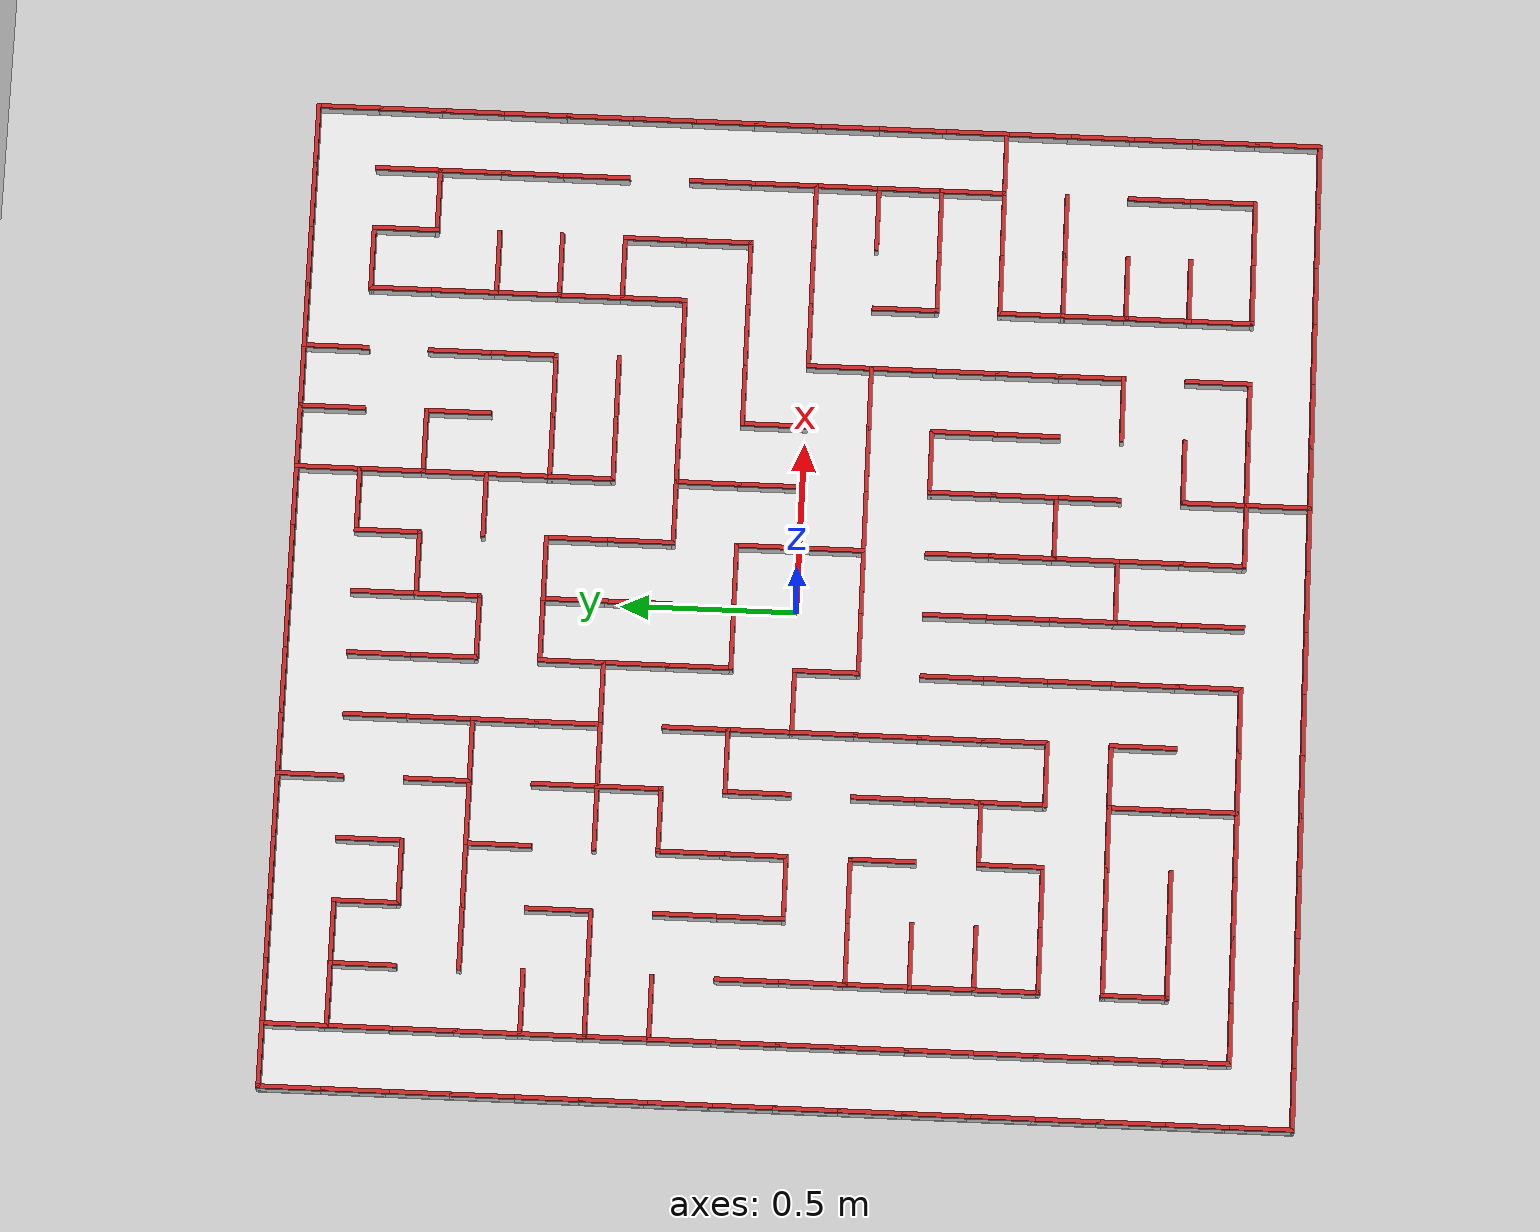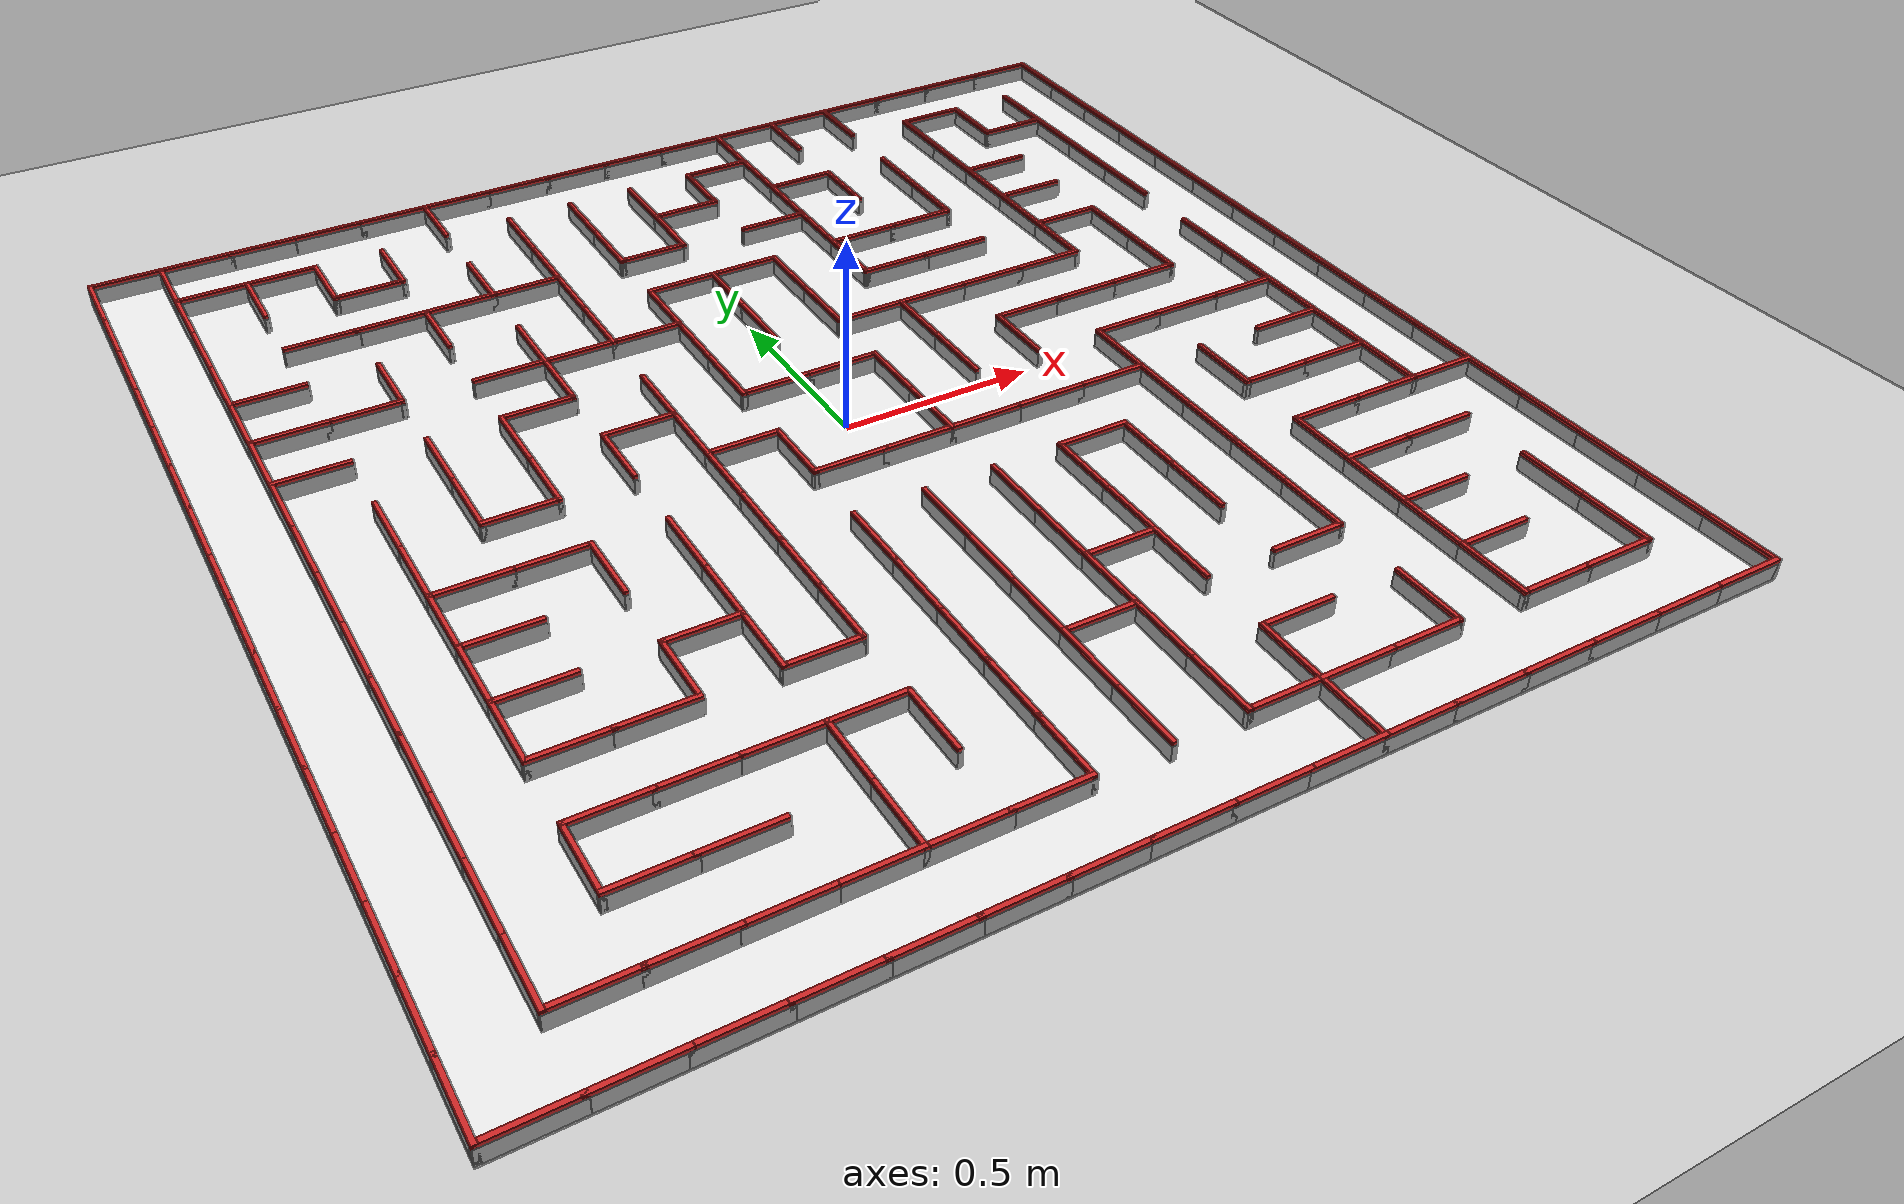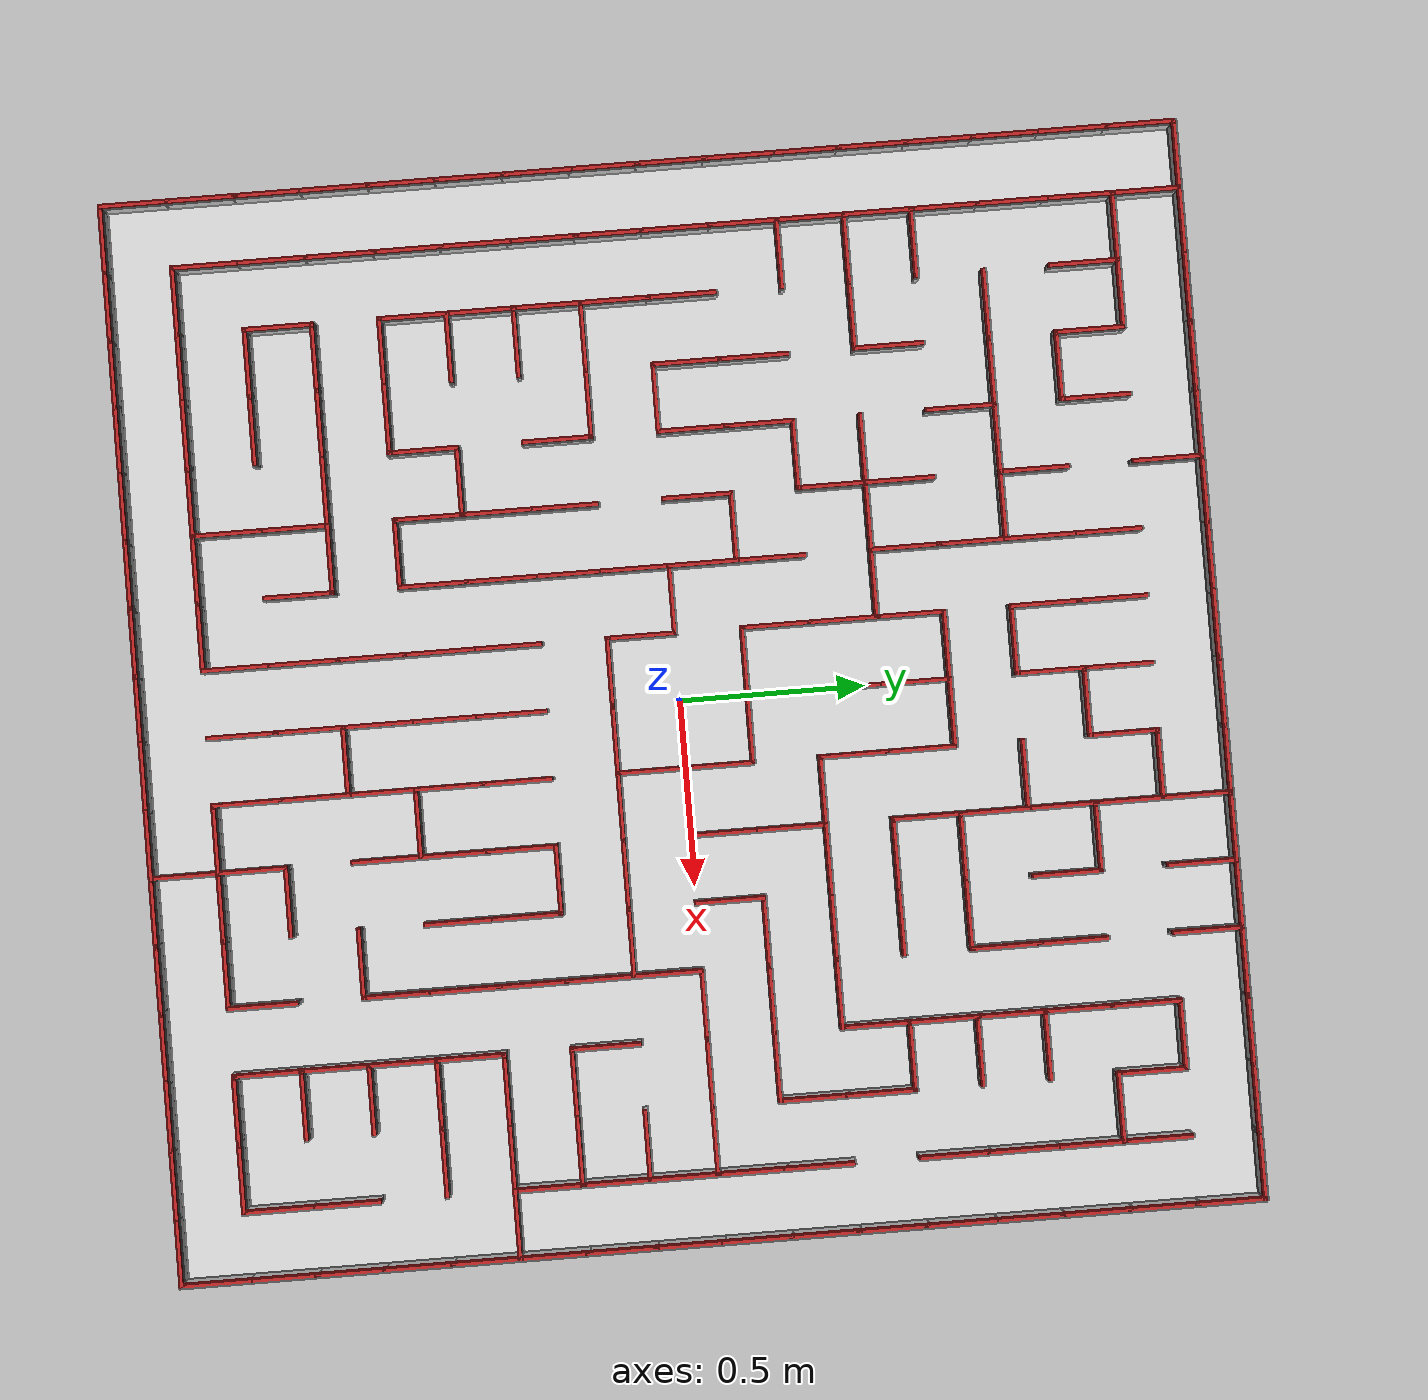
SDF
<sdf version="1.6">
 <world name="default">
  <model name="ground_plane">
   <static>1</static>
   <link name="link">
    <collision name="collision">
     <geometry><plane><normal>0 0 1</normal><size>100 100</size></plane></geometry>
     <surface><friction><ode><mu>100</mu><mu2>50</mu2></ode></friction></surface>
    </collision>
    <visual name="visual">
     <cast_shadows>0</cast_shadows>
     <geometry><plane><normal>0 0 1</normal><size>100 100</size></plane></geometry>
     <material>
      <script><uri>file://media/materials/scripts/gazebo.material</uri><name>Gazebo/Grey</name></script>
     </material>
    </visual>
   </link>
  </model>
  <light name="sun" type="directional">
   <pose>0 0 10 0 -0 0</pose>
   <diffuse>0.8 0.8 0.8 1</diffuse>
   <specular>0.2 0.2 0.2 1</specular>
   <attenuation>
    <range>1000</range>
    <constant>0.9</constant>
    <linear>0.01</linear>
    <quadratic>0.001</quadratic>
   </attenuation>
   <direction>-0.5 0.1 -0.9</direction>
  </light>
  <plugin name="maze" filename="libmaze_plugin.so"/>
  <physics name="default_physics" default="0" type="ode">
   <real_time_update_rate>0</real_time_update_rate>
   <max_step_size>0.001</max_step_size>
   <real_time_factor>1</real_time_factor>
  </physics>
  <gravity>0 0 -9.8</gravity>
  <magnetic_field>6e-06 2.3e-05 -4.2e-05</magnetic_field>
  <atmosphere type="adiabatic"/>
  <scene><ambient>0.4 0.4 0.4 1</ambient><background>0.7 0.7 0.7 1</background><shadows>1</shadows></scene>
  <spherical_coordinates>
   <surface_model>EARTH_WGS84</surface_model>
   <latitude_deg>0</latitude_deg>
   <longitude_deg>0</longitude_deg>
   <elevation>0</elevation>
   <heading_deg>0</heading_deg>
  </spherical_coordinates>
  <model name="my_maze">
   <link name="base">
    <inertial>
     <mass>1</mass>
     <inertia>
      <ixx>1.39394</ixx>
      <ixy>0</ixy>
      <ixz>0</ixz>
      <iyy>0.696972</iyy>
      <iyz>0</iyz>
      <izz>0.696973</izz>
     </inertia>
     <pose>0 0 0.05 0 -0 0</pose>
    </inertial>
    <visual name="visual">
     <pose>0 0 0.0025 0 -0 0</pose>
     <geometry><box><size>2.892 2.892 0.005</size></box></geometry>
     <material>
      <script><uri>file://media/materials/scripts/gazebo.material</uri><name>Gazebo/White</name></script>
     </material>
    </visual>
    <collision name="collision">
     <pose>0 0 0.0025 0 -0 0</pose>
     <geometry><box><size>2.892 2.892 0.005</size></box></geometry>
     <surface><friction><ode><mu>1000</mu><mu2>1000</mu2></ode></friction></surface>
    </collision>
    <visual name="paint_v_0_0_W">
     <pose>-1.44 1.35 0.05 0 -0 1.5708</pose>
     <geometry><box><size>0.192 0.012 0.01</size></box></geometry>
     <material>
      <script><name>Gazebo/Red</name><uri>file://media/materials/scripts/gazebo.material</uri></script>
     </material>
    </visual>
    <visual name="v_0_0_W">
     <pose>-1.44 1.35 0.025 0 -0 1.5708</pose>
     <geometry><box><size>0.192 0.012 0.04</size></box></geometry>
    </visual>
    <collision name="p_0_0_W">
     <pose>-1.44 1.35 0.03 0 -0 1.5708</pose>
     <geometry><box><size>0.192 0.012 0.05</size></box></geometry>
    </collision>
    <visual name="paint_v_0_1_W">
     <pose>-1.26 1.35 0.05 0 -0 1.5708</pose>
     <geometry><box><size>0.192 0.012 0.01</size></box></geometry>
     <material>
      <script><name>Gazebo/Red</name><uri>file://media/materials/scripts/gazebo.material</uri></script>
     </material>
    </visual>
    <visual name="v_0_1_W">
     <pose>-1.26 1.35 0.025 0 -0 1.5708</pose>
     <geometry><box><size>0.192 0.012 0.04</size></box></geometry>
    </visual>
    <collision name="p_0_1_W">
     <pose>-1.26 1.35 0.03 0 -0 1.5708</pose>
     <geometry><box><size>0.192 0.012 0.05</size></box></geometry>
    </collision>
    <visual name="paint_v_0_1_S">
     <pose>-1.17 1.26 0.05 0 -0 0</pose>
     <geometry><box><size>0.192 0.012 0.01</size></box></geometry>
     <material>
      <script><name>Gazebo/Red</name><uri>file://media/materials/scripts/gazebo.material</uri></script>
     </material>
    </visual>
    <visual name="v_0_1_S">
     <pose>-1.17 1.26 0.025 0 -0 0</pose>
     <geometry><box><size>0.192 0.012 0.04</size></box></geometry>
    </visual>
    <collision name="p_0_1_S">
     <pose>-1.17 1.26 0.03 0 -0 0</pose>
     <geometry><box><size>0.192 0.012 0.05</size></box></geometry>
    </collision>
    <visual name="paint_v_0_2_S">
     <pose>-0.99 1.26 0.05 0 -0 0</pose>
     <geometry><box><size>0.192 0.012 0.01</size></box></geometry>
     <material>
      <script><name>Gazebo/Red</name><uri>file://media/materials/scripts/gazebo.material</uri></script>
     </material>
    </visual>
    <visual name="v_0_2_S">
     <pose>-0.99 1.26 0.025 0 -0 0</pose>
     <geometry><box><size>0.192 0.012 0.04</size></box></geometry>
    </visual>
    <collision name="p_0_2_S">
     <pose>-0.99 1.26 0.03 0 -0 0</pose>
     <geometry><box><size>0.192 0.012 0.05</size></box></geometry>
    </collision>
    <visual name="paint_v_0_5_W">
     <pose>-0.54 1.35 0.05 0 -0 1.5708</pose>
     <geometry><box><size>0.192 0.012 0.01</size></box></geometry>
     <material>
      <script><name>Gazebo/Red</name><uri>file://media/materials/scripts/gazebo.material</uri></script>
     </material>
    </visual>
    <visual name="v_0_5_W">
     <pose>-0.54 1.35 0.025 0 -0 1.5708</pose>
     <geometry><box><size>0.192 0.012 0.04</size></box></geometry>
    </visual>
    <collision name="p_0_5_W">
     <pose>-0.54 1.35 0.03 0 -0 1.5708</pose>
     <geometry><box><size>0.192 0.012 0.05</size></box></geometry>
    </collision>
    <visual name="paint_v_0_9_S">
     <pose>0.27 1.26 0.05 0 -0 0</pose>
     <geometry><box><size>0.192 0.012 0.01</size></box></geometry>
     <material>
      <script><name>Gazebo/Red</name><uri>file://media/materials/scripts/gazebo.material</uri></script>
     </material>
    </visual>
    <visual name="v_0_9_S">
     <pose>0.27 1.26 0.025 0 -0 0</pose>
     <geometry><box><size>0.192 0.012 0.04</size></box></geometry>
    </visual>
    <collision name="p_0_9_S">
     <pose>0.27 1.26 0.03 0 -0 0</pose>
     <geometry><box><size>0.192 0.012 0.05</size></box></geometry>
    </collision>
    <visual name="paint_v_0_10_W">
     <pose>0.36 1.35 0.05 0 -0 1.5708</pose>
     <geometry><box><size>0.192 0.012 0.01</size></box></geometry>
     <material>
      <script><name>Gazebo/Red</name><uri>file://media/materials/scripts/gazebo.material</uri></script>
     </material>
    </visual>
    <visual name="v_0_10_W">
     <pose>0.36 1.35 0.025 0 -0 1.5708</pose>
     <geometry><box><size>0.192 0.012 0.04</size></box></geometry>
    </visual>
    <collision name="p_0_10_W">
     <pose>0.36 1.35 0.03 0 -0 1.5708</pose>
     <geometry><box><size>0.192 0.012 0.05</size></box></geometry>
    </collision>
    <visual name="paint_v_0_11_W">
     <pose>0.54 1.35 0.05 0 -0 1.5708</pose>
     <geometry><box><size>0.192 0.012 0.01</size></box></geometry>
     <material>
      <script><name>Gazebo/Red</name><uri>file://media/materials/scripts/gazebo.material</uri></script>
     </material>
    </visual>
    <visual name="v_0_11_W">
     <pose>0.54 1.35 0.025 0 -0 1.5708</pose>
     <geometry><box><size>0.192 0.012 0.04</size></box></geometry>
    </visual>
    <collision name="p_0_11_W">
     <pose>0.54 1.35 0.03 0 -0 1.5708</pose>
     <geometry><box><size>0.192 0.012 0.05</size></box></geometry>
    </collision>
    <visual name="paint_v_0_12_W">
     <pose>0.72 1.35 0.05 0 -0 1.5708</pose>
     <geometry><box><size>0.192 0.012 0.01</size></box></geometry>
     <material>
      <script><name>Gazebo/Red</name><uri>file://media/materials/scripts/gazebo.material</uri></script>
     </material>
    </visual>
    <visual name="v_0_12_W">
     <pose>0.72 1.35 0.025 0 -0 1.5708</pose>
     <geometry><box><size>0.192 0.012 0.04</size></box></geometry>
    </visual>
    <collision name="p_0_12_W">
     <pose>0.72 1.35 0.03 0 -0 1.5708</pose>
     <geometry><box><size>0.192 0.012 0.05</size></box></geometry>
    </collision>
    <visual name="paint_v_0_13_S">
     <pose>0.99 1.26 0.05 0 -0 0</pose>
     <geometry><box><size>0.192 0.012 0.01</size></box></geometry>
     <material>
      <script><name>Gazebo/Red</name><uri>file://media/materials/scripts/gazebo.material</uri></script>
     </material>
    </visual>
    <visual name="v_0_13_S">
     <pose>0.99 1.26 0.025 0 -0 0</pose>
     <geometry><box><size>0.192 0.012 0.04</size></box></geometry>
    </visual>
    <collision name="p_0_13_S">
     <pose>0.99 1.26 0.03 0 -0 0</pose>
     <geometry><box><size>0.192 0.012 0.05</size></box></geometry>
    </collision>
    <visual name="paint_v_1_0_W">
     <pose>-1.44 1.17 0.05 0 -0 1.5708</pose>
     <geometry><box><size>0.192 0.012 0.01</size></box></geometry>
     <material>
      <script><name>Gazebo/Red</name><uri>file://media/materials/scripts/gazebo.material</uri></script>
     </material>
    </visual>
    <visual name="v_1_0_W">
     <pose>-1.44 1.17 0.025 0 -0 1.5708</pose>
     <geometry><box><size>0.192 0.012 0.04</size></box></geometry>
    </visual>
    <collision name="p_1_0_W">
     <pose>-1.44 1.17 0.03 0 -0 1.5708</pose>
     <geometry><box><size>0.192 0.012 0.05</size></box></geometry>
    </collision>
    <visual name="paint_v_1_1_W">
     <pose>-1.26 1.17 0.05 0 -0 1.5708</pose>
     <geometry><box><size>0.192 0.012 0.01</size></box></geometry>
     <material>
      <script><name>Gazebo/Red</name><uri>file://media/materials/scripts/gazebo.material</uri></script>
     </material>
    </visual>
    <visual name="v_1_1_W">
     <pose>-1.26 1.17 0.025 0 -0 1.5708</pose>
     <geometry><box><size>0.192 0.012 0.04</size></box></geometry>
    </visual>
    <collision name="p_1_1_W">
     <pose>-1.26 1.17 0.03 0 -0 1.5708</pose>
     <geometry><box><size>0.192 0.012 0.05</size></box></geometry>
    </collision>
    <visual name="paint_v_1_2_W">
     <pose>-1.08 1.17 0.05 0 -0 1.5708</pose>
     <geometry><box><size>0.192 0.012 0.01</size></box></geometry>
     <material>
      <script><name>Gazebo/Red</name><uri>file://media/materials/scripts/gazebo.material</uri></script>
     </material>
    </visual>
    <visual name="v_1_2_W">
     <pose>-1.08 1.17 0.025 0 -0 1.5708</pose>
     <geometry><box><size>0.192 0.012 0.04</size></box></geometry>
    </visual>
    <collision name="p_1_2_W">
     <pose>-1.08 1.17 0.03 0 -0 1.5708</pose>
     <geometry><box><size>0.192 0.012 0.05</size></box></geometry>
    </collision>
    <visual name="paint_v_1_3_W">
     <pose>-0.9 1.17 0.05 0 -0 1.5708</pose>
     <geometry><box><size>0.192 0.012 0.01</size></box></geometry>
     <material>
      <script><name>Gazebo/Red</name><uri>file://media/materials/scripts/gazebo.material</uri></script>
     </material>
    </visual>
    <visual name="v_1_3_W">
     <pose>-0.9 1.17 0.025 0 -0 1.5708</pose>
     <geometry><box><size>0.192 0.012 0.04</size></box></geometry>
    </visual>
    <collision name="p_1_3_W">
     <pose>-0.9 1.17 0.03 0 -0 1.5708</pose>
     <geometry><box><size>0.192 0.012 0.05</size></box></geometry>
    </collision>
    <visual name="paint_v_1_3_S">
     <pose>-0.81 1.08 0.05 0 -0 0</pose>
     <geometry><box><size>0.192 0.012 0.01</size></box></geometry>
     <material>
      <script><name>Gazebo/Red</name><uri>file://media/materials/scripts/gazebo.material</uri></script>
     </material>
    </visual>
    <visual name="v_1_3_S">
     <pose>-0.81 1.08 0.025 0 -0 0</pose>
     <geometry><box><size>0.192 0.012 0.04</size></box></geometry>
    </visual>
    <collision name="p_1_3_S">
     <pose>-0.81 1.08 0.03 0 -0 0</pose>
     <geometry><box><size>0.192 0.012 0.05</size></box></geometry>
    </collision>
    <visual name="paint_v_1_4_W">
     <pose>-0.72 1.17 0.05 0 -0 1.5708</pose>
     <geometry><box><size>0.192 0.012 0.01</size></box></geometry>
     <material>
      <script><name>Gazebo/Red</name><uri>file://media/materials/scripts/gazebo.material</uri></script>
     </material>
    </visual>
    <visual name="v_1_4_W">
     <pose>-0.72 1.17 0.025 0 -0 1.5708</pose>
     <geometry><box><size>0.192 0.012 0.04</size></box></geometry>
    </visual>
    <collision name="p_1_4_W">
     <pose>-0.72 1.17 0.03 0 -0 1.5708</pose>
     <geometry><box><size>0.192 0.012 0.05</size></box></geometry>
    </collision>
    <visual name="paint_v_1_6_W">
     <pose>-0.36 1.17 0.05 0 -0 1.5708</pose>
     <geometry><box><size>0.192 0.012 0.01</size></box></geometry>
     <material>
      <script><name>Gazebo/Red</name><uri>file://media/materials/scripts/gazebo.material</uri></script>
     </material>
    </visual>
    <visual name="v_1_6_W">
     <pose>-0.36 1.17 0.025 0 -0 1.5708</pose>
     <geometry><box><size>0.192 0.012 0.04</size></box></geometry>
    </visual>
    <collision name="p_1_6_W">
     <pose>-0.36 1.17 0.03 0 -0 1.5708</pose>
     <geometry><box><size>0.192 0.012 0.05</size></box></geometry>
    </collision>
    <visual name="paint_v_1_7_W">
     <pose>-0.18 1.17 0.05 0 -0 1.5708</pose>
     <geometry><box><size>0.192 0.012 0.01</size></box></geometry>
     <material>
      <script><name>Gazebo/Red</name><uri>file://media/materials/scripts/gazebo.material</uri></script>
     </material>
    </visual>
    <visual name="v_1_7_W">
     <pose>-0.18 1.17 0.025 0 -0 1.5708</pose>
     <geometry><box><size>0.192 0.012 0.04</size></box></geometry>
    </visual>
    <collision name="p_1_7_W">
     <pose>-0.18 1.17 0.03 0 -0 1.5708</pose>
     <geometry><box><size>0.192 0.012 0.05</size></box></geometry>
    </collision>
    <visual name="paint_v_1_8_W">
     <pose>0 1.17 0.05 0 -0 1.5708</pose>
     <geometry><box><size>0.192 0.012 0.01</size></box></geometry>
     <material>
      <script><name>Gazebo/Red</name><uri>file://media/materials/scripts/gazebo.material</uri></script>
     </material>
    </visual>
    <visual name="v_1_8_W">
     <pose>0 1.17 0.025 0 -0 1.5708</pose>
     <geometry><box><size>0.192 0.012 0.04</size></box></geometry>
    </visual>
    <collision name="p_1_8_W">
     <pose>0 1.17 0.03 0 -0 1.5708</pose>
     <geometry><box><size>0.192 0.012 0.05</size></box></geometry>
    </collision>
    <visual name="paint_v_1_8_S">
     <pose>0.09 1.08 0.05 0 -0 0</pose>
     <geometry><box><size>0.192 0.012 0.01</size></box></geometry>
     <material>
      <script><name>Gazebo/Red</name><uri>file://media/materials/scripts/gazebo.material</uri></script>
     </material>
    </visual>
    <visual name="v_1_8_S">
     <pose>0.09 1.08 0.025 0 -0 0</pose>
     <geometry><box><size>0.192 0.012 0.04</size></box></geometry>
    </visual>
    <collision name="p_1_8_S">
     <pose>0.09 1.08 0.03 0 -0 0</pose>
     <geometry><box><size>0.192 0.012 0.05</size></box></geometry>
    </collision>
    <visual name="paint_v_1_9_W">
     <pose>0.18 1.17 0.05 0 -0 1.5708</pose>
     <geometry><box><size>0.192 0.012 0.01</size></box></geometry>
     <material>
      <script><name>Gazebo/Red</name><uri>file://media/materials/scripts/gazebo.material</uri></script>
     </material>
    </visual>
    <visual name="v_1_9_W">
     <pose>0.18 1.17 0.025 0 -0 1.5708</pose>
     <geometry><box><size>0.192 0.012 0.04</size></box></geometry>
    </visual>
    <collision name="p_1_9_W">
     <pose>0.18 1.17 0.03 0 -0 1.5708</pose>
     <geometry><box><size>0.192 0.012 0.05</size></box></geometry>
    </collision>
    <visual name="paint_v_1_10_W">
     <pose>0.36 1.17 0.05 0 -0 1.5708</pose>
     <geometry><box><size>0.192 0.012 0.01</size></box></geometry>
     <material>
      <script><name>Gazebo/Red</name><uri>file://media/materials/scripts/gazebo.material</uri></script>
     </material>
    </visual>
    <visual name="v_1_10_W">
     <pose>0.36 1.17 0.025 0 -0 1.5708</pose>
     <geometry><box><size>0.192 0.012 0.04</size></box></geometry>
    </visual>
    <collision name="p_1_10_W">
     <pose>0.36 1.17 0.03 0 -0 1.5708</pose>
     <geometry><box><size>0.192 0.012 0.05</size></box></geometry>
    </collision>
    <visual name="paint_v_1_10_S">
     <pose>0.45 1.08 0.05 0 -0 0</pose>
     <geometry><box><size>0.192 0.012 0.01</size></box></geometry>
     <material>
      <script><name>Gazebo/Red</name><uri>file://media/materials/scripts/gazebo.material</uri></script>
     </material>
    </visual>
    <visual name="v_1_10_S">
     <pose>0.45 1.08 0.025 0 -0 0</pose>
     <geometry><box><size>0.192 0.012 0.04</size></box></geometry>
    </visual>
    <collision name="p_1_10_S">
     <pose>0.45 1.08 0.03 0 -0 0</pose>
     <geometry><box><size>0.192 0.012 0.05</size></box></geometry>
    </collision>
    <visual name="paint_v_1_13_W">
     <pose>0.9 1.17 0.05 0 -0 1.5708</pose>
     <geometry><box><size>0.192 0.012 0.01</size></box></geometry>
     <material>
      <script><name>Gazebo/Red</name><uri>file://media/materials/scripts/gazebo.material</uri></script>
     </material>
    </visual>
    <visual name="v_1_13_W">
     <pose>0.9 1.17 0.025 0 -0 1.5708</pose>
     <geometry><box><size>0.192 0.012 0.04</size></box></geometry>
    </visual>
    <collision name="p_1_13_W">
     <pose>0.9 1.17 0.03 0 -0 1.5708</pose>
     <geometry><box><size>0.192 0.012 0.05</size></box></geometry>
    </collision>
    <visual name="paint_v_1_14_W">
     <pose>1.08 1.17 0.05 0 -0 1.5708</pose>
     <geometry><box><size>0.192 0.012 0.01</size></box></geometry>
     <material>
      <script><name>Gazebo/Red</name><uri>file://media/materials/scripts/gazebo.material</uri></script>
     </material>
    </visual>
    <visual name="v_1_14_W">
     <pose>1.08 1.17 0.025 0 -0 1.5708</pose>
     <geometry><box><size>0.192 0.012 0.04</size></box></geometry>
    </visual>
    <collision name="p_1_14_W">
     <pose>1.08 1.17 0.03 0 -0 1.5708</pose>
     <geometry><box><size>0.192 0.012 0.05</size></box></geometry>
    </collision>
    <visual name="paint_v_1_14_S">
     <pose>1.17 1.08 0.05 0 -0 0</pose>
     <geometry><box><size>0.192 0.012 0.01</size></box></geometry>
     <material>
      <script><name>Gazebo/Red</name><uri>file://media/materials/scripts/gazebo.material</uri></script>
     </material>
    </visual>
    <visual name="v_1_14_S">
     <pose>1.17 1.08 0.025 0 -0 0</pose>
     <geometry><box><size>0.192 0.012 0.04</size></box></geometry>
    </visual>
    <collision name="p_1_14_S">
     <pose>1.17 1.08 0.03 0 -0 0</pose>
     <geometry><box><size>0.192 0.012 0.05</size></box></geometry>
    </collision>
    <visual name="paint_v_1_15_W">
     <pose>1.26 1.17 0.05 0 -0 1.5708</pose>
     <geometry><box><size>0.192 0.012 0.01</size></box></geometry>
     <material>
      <script><name>Gazebo/Red</name><uri>file://media/materials/scripts/gazebo.material</uri></script>
     </material>
    </visual>
    <visual name="v_1_15_W">
     <pose>1.26 1.17 0.025 0 -0 1.5708</pose>
     <geometry><box><size>0.192 0.012 0.04</size></box></geometry>
    </visual>
    <collision name="p_1_15_W">
     <pose>1.26 1.17 0.03 0 -0 1.5708</pose>
     <geometry><box><size>0.192 0.012 0.05</size></box></geometry>
    </collision>
    <visual name="paint_v_2_0_W">
     <pose>-1.44 0.99 0.05 0 -0 1.5708</pose>
     <geometry><box><size>0.192 0.012 0.01</size></box></geometry>
     <material>
      <script><name>Gazebo/Red</name><uri>file://media/materials/scripts/gazebo.material</uri></script>
     </material>
    </visual>
    <visual name="v_2_0_W">
     <pose>-1.44 0.99 0.025 0 -0 1.5708</pose>
     <geometry><box><size>0.192 0.012 0.04</size></box></geometry>
    </visual>
    <collision name="p_2_0_W">
     <pose>-1.44 0.99 0.03 0 -0 1.5708</pose>
     <geometry><box><size>0.192 0.012 0.05</size></box></geometry>
    </collision>
    <visual name="paint_v_2_1_W">
     <pose>-1.26 0.99 0.05 0 -0 1.5708</pose>
     <geometry><box><size>0.192 0.012 0.01</size></box></geometry>
     <material>
      <script><name>Gazebo/Red</name><uri>file://media/materials/scripts/gazebo.material</uri></script>
     </material>
    </visual>
    <visual name="v_2_1_W">
     <pose>-1.26 0.99 0.025 0 -0 1.5708</pose>
     <geometry><box><size>0.192 0.012 0.04</size></box></geometry>
    </visual>
    <collision name="p_2_1_W">
     <pose>-1.26 0.99 0.03 0 -0 1.5708</pose>
     <geometry><box><size>0.192 0.012 0.05</size></box></geometry>
    </collision>
    <visual name="paint_v_2_2_S">
     <pose>-0.99 0.9 0.05 0 -0 0</pose>
     <geometry><box><size>0.192 0.012 0.01</size></box></geometry>
     <material>
      <script><name>Gazebo/Red</name><uri>file://media/materials/scripts/gazebo.material</uri></script>
     </material>
    </visual>
    <visual name="v_2_2_S">
     <pose>-0.99 0.9 0.025 0 -0 0</pose>
     <geometry><box><size>0.192 0.012 0.04</size></box></geometry>
    </visual>
    <collision name="p_2_2_S">
     <pose>-0.99 0.9 0.03 0 -0 0</pose>
     <geometry><box><size>0.192 0.012 0.05</size></box></geometry>
    </collision>
    <visual name="paint_v_2_3_S">
     <pose>-0.81 0.9 0.05 0 -0 0</pose>
     <geometry><box><size>0.192 0.012 0.01</size></box></geometry>
     <material>
      <script><name>Gazebo/Red</name><uri>file://media/materials/scripts/gazebo.material</uri></script>
     </material>
    </visual>
    <visual name="v_2_3_S">
     <pose>-0.81 0.9 0.025 0 -0 0</pose>
     <geometry><box><size>0.192 0.012 0.04</size></box></geometry>
    </visual>
    <collision name="p_2_3_S">
     <pose>-0.81 0.9 0.03 0 -0 0</pose>
     <geometry><box><size>0.192 0.012 0.05</size></box></geometry>
    </collision>
    <visual name="paint_v_2_4_S">
     <pose>-0.63 0.9 0.05 0 -0 0</pose>
     <geometry><box><size>0.192 0.012 0.01</size></box></geometry>
     <material>
      <script><name>Gazebo/Red</name><uri>file://media/materials/scripts/gazebo.material</uri></script>
     </material>
    </visual>
    <visual name="v_2_4_S">
     <pose>-0.63 0.9 0.025 0 -0 0</pose>
     <geometry><box><size>0.192 0.012 0.04</size></box></geometry>
    </visual>
    <collision name="p_2_4_S">
     <pose>-0.63 0.9 0.03 0 -0 0</pose>
     <geometry><box><size>0.192 0.012 0.05</size></box></geometry>
    </collision>
    <visual name="paint_v_2_5_W">
     <pose>-0.54 0.99 0.05 0 -0 1.5708</pose>
     <geometry><box><size>0.192 0.012 0.01</size></box></geometry>
     <material>
      <script><name>Gazebo/Red</name><uri>file://media/materials/scripts/gazebo.material</uri></script>
     </material>
    </visual>
    <visual name="v_2_5_W">
     <pose>-0.54 0.99 0.025 0 -0 1.5708</pose>
     <geometry><box><size>0.192 0.012 0.04</size></box></geometry>
    </visual>
    <collision name="p_2_5_W">
     <pose>-0.54 0.99 0.03 0 -0 1.5708</pose>
     <geometry><box><size>0.192 0.012 0.05</size></box></geometry>
    </collision>
    <visual name="paint_v_2_5_S">
     <pose>-0.45 0.9 0.05 0 -0 0</pose>
     <geometry><box><size>0.192 0.012 0.01</size></box></geometry>
     <material>
      <script><name>Gazebo/Red</name><uri>file://media/materials/scripts/gazebo.material</uri></script>
     </material>
    </visual>
    <visual name="v_2_5_S">
     <pose>-0.45 0.9 0.025 0 -0 0</pose>
     <geometry><box><size>0.192 0.012 0.04</size></box></geometry>
    </visual>
    <collision name="p_2_5_S">
     <pose>-0.45 0.9 0.03 0 -0 0</pose>
     <geometry><box><size>0.192 0.012 0.05</size></box></geometry>
    </collision>
    <visual name="paint_v_2_6_W">
     <pose>-0.36 0.99 0.05 0 -0 1.5708</pose>
     <geometry><box><size>0.192 0.012 0.01</size></box></geometry>
     <material>
      <script><name>Gazebo/Red</name><uri>file://media/materials/scripts/gazebo.material</uri></script>
     </material>
    </visual>
    <visual name="v_2_6_W">
     <pose>-0.36 0.99 0.025 0 -0 1.5708</pose>
     <geometry><box><size>0.192 0.012 0.04</size></box></geometry>
    </visual>
    <collision name="p_2_6_W">
     <pose>-0.36 0.99 0.03 0 -0 1.5708</pose>
     <geometry><box><size>0.192 0.012 0.05</size></box></geometry>
    </collision>
    <visual name="paint_v_2_7_W">
     <pose>-0.18 0.99 0.05 0 -0 1.5708</pose>
     <geometry><box><size>0.192 0.012 0.01</size></box></geometry>
     <material>
      <script><name>Gazebo/Red</name><uri>file://media/materials/scripts/gazebo.material</uri></script>
     </material>
    </visual>
    <visual name="v_2_7_W">
     <pose>-0.18 0.99 0.025 0 -0 1.5708</pose>
     <geometry><box><size>0.192 0.012 0.04</size></box></geometry>
    </visual>
    <collision name="p_2_7_W">
     <pose>-0.18 0.99 0.03 0 -0 1.5708</pose>
     <geometry><box><size>0.192 0.012 0.05</size></box></geometry>
    </collision>
    <visual name="paint_v_2_7_S">
     <pose>-0.09 0.9 0.05 0 -0 0</pose>
     <geometry><box><size>0.192 0.012 0.01</size></box></geometry>
     <material>
      <script><name>Gazebo/Red</name><uri>file://media/materials/scripts/gazebo.material</uri></script>
     </material>
    </visual>
    <visual name="v_2_7_S">
     <pose>-0.09 0.9 0.025 0 -0 0</pose>
     <geometry><box><size>0.192 0.012 0.04</size></box></geometry>
    </visual>
    <collision name="p_2_7_S">
     <pose>-0.09 0.9 0.03 0 -0 0</pose>
     <geometry><box><size>0.192 0.012 0.05</size></box></geometry>
    </collision>
    <visual name="paint_v_2_8_W">
     <pose>0 0.99 0.05 0 -0 1.5708</pose>
     <geometry><box><size>0.192 0.012 0.01</size></box></geometry>
     <material>
      <script><name>Gazebo/Red</name><uri>file://media/materials/scripts/gazebo.material</uri></script>
     </material>
    </visual>
    <visual name="v_2_8_W">
     <pose>0 0.99 0.025 0 -0 1.5708</pose>
     <geometry><box><size>0.192 0.012 0.04</size></box></geometry>
    </visual>
    <collision name="p_2_8_W">
     <pose>0 0.99 0.03 0 -0 1.5708</pose>
     <geometry><box><size>0.192 0.012 0.05</size></box></geometry>
    </collision>
    <visual name="paint_v_2_9_S">
     <pose>0.27 0.9 0.05 0 -0 0</pose>
     <geometry><box><size>0.192 0.012 0.01</size></box></geometry>
     <material>
      <script><name>Gazebo/Red</name><uri>file://media/materials/scripts/gazebo.material</uri></script>
     </material>
    </visual>
    <visual name="v_2_9_S">
     <pose>0.27 0.9 0.025 0 -0 0</pose>
     <geometry><box><size>0.192 0.012 0.04</size></box></geometry>
    </visual>
    <collision name="p_2_9_S">
     <pose>0.27 0.9 0.03 0 -0 0</pose>
     <geometry><box><size>0.192 0.012 0.05</size></box></geometry>
    </collision>
    <visual name="paint_v_2_10_W">
     <pose>0.36 0.99 0.05 0 -0 1.5708</pose>
     <geometry><box><size>0.192 0.012 0.01</size></box></geometry>
     <material>
      <script><name>Gazebo/Red</name><uri>file://media/materials/scripts/gazebo.material</uri></script>
     </material>
    </visual>
    <visual name="v_2_10_W">
     <pose>0.36 0.99 0.025 0 -0 1.5708</pose>
     <geometry><box><size>0.192 0.012 0.04</size></box></geometry>
    </visual>
    <collision name="p_2_10_W">
     <pose>0.36 0.99 0.03 0 -0 1.5708</pose>
     <geometry><box><size>0.192 0.012 0.05</size></box></geometry>
    </collision>
    <visual name="paint_v_2_11_W">
     <pose>0.54 0.99 0.05 0 -0 1.5708</pose>
     <geometry><box><size>0.192 0.012 0.01</size></box></geometry>
     <material>
      <script><name>Gazebo/Red</name><uri>file://media/materials/scripts/gazebo.material</uri></script>
     </material>
    </visual>
    <visual name="v_2_11_W">
     <pose>0.54 0.99 0.025 0 -0 1.5708</pose>
     <geometry><box><size>0.192 0.012 0.04</size></box></geometry>
    </visual>
    <collision name="p_2_11_W">
     <pose>0.54 0.99 0.03 0 -0 1.5708</pose>
     <geometry><box><size>0.192 0.012 0.05</size></box></geometry>
    </collision>
    <visual name="paint_v_2_12_W">
     <pose>0.72 0.99 0.05 0 -0 1.5708</pose>
     <geometry><box><size>0.192 0.012 0.01</size></box></geometry>
     <material>
      <script><name>Gazebo/Red</name><uri>file://media/materials/scripts/gazebo.material</uri></script>
     </material>
    </visual>
    <visual name="v_2_12_W">
     <pose>0.72 0.99 0.025 0 -0 1.5708</pose>
     <geometry><box><size>0.192 0.012 0.04</size></box></geometry>
    </visual>
    <collision name="p_2_12_W">
     <pose>0.72 0.99 0.03 0 -0 1.5708</pose>
     <geometry><box><size>0.192 0.012 0.05</size></box></geometry>
    </collision>
    <visual name="paint_v_2_13_W">
     <pose>0.9 0.99 0.05 0 -0 1.5708</pose>
     <geometry><box><size>0.192 0.012 0.01</size></box></geometry>
     <material>
      <script><name>Gazebo/Red</name><uri>file://media/materials/scripts/gazebo.material</uri></script>
     </material>
    </visual>
    <visual name="v_2_13_W">
     <pose>0.9 0.99 0.025 0 -0 1.5708</pose>
     <geometry><box><size>0.192 0.012 0.04</size></box></geometry>
    </visual>
    <collision name="p_2_13_W">
     <pose>0.9 0.99 0.03 0 -0 1.5708</pose>
     <geometry><box><size>0.192 0.012 0.05</size></box></geometry>
    </collision>
    <visual name="paint_v_2_13_S">
     <pose>0.99 0.9 0.05 0 -0 0</pose>
     <geometry><box><size>0.192 0.012 0.01</size></box></geometry>
     <material>
      <script><name>Gazebo/Red</name><uri>file://media/materials/scripts/gazebo.material</uri></script>
     </material>
    </visual>
    <visual name="v_2_13_S">
     <pose>0.99 0.9 0.025 0 -0 0</pose>
     <geometry><box><size>0.192 0.012 0.04</size></box></geometry>
    </visual>
    <collision name="p_2_13_S">
     <pose>0.99 0.9 0.03 0 -0 0</pose>
     <geometry><box><size>0.192 0.012 0.05</size></box></geometry>
    </collision>
    <visual name="paint_v_2_15_W">
     <pose>1.26 0.99 0.05 0 -0 1.5708</pose>
     <geometry><box><size>0.192 0.012 0.01</size></box></geometry>
     <material>
      <script><name>Gazebo/Red</name><uri>file://media/materials/scripts/gazebo.material</uri></script>
     </material>
    </visual>
    <visual name="v_2_15_W">
     <pose>1.26 0.99 0.025 0 -0 1.5708</pose>
     <geometry><box><size>0.192 0.012 0.04</size></box></geometry>
    </visual>
    <collision name="p_2_15_W">
     <pose>1.26 0.99 0.03 0 -0 1.5708</pose>
     <geometry><box><size>0.192 0.012 0.05</size></box></geometry>
    </collision>
    <visual name="paint_v_3_0_W">
     <pose>-1.44 0.81 0.05 0 -0 1.5708</pose>
     <geometry><box><size>0.192 0.012 0.01</size></box></geometry>
     <material>
      <script><name>Gazebo/Red</name><uri>file://media/materials/scripts/gazebo.material</uri></script>
     </material>
    </visual>
    <visual name="v_3_0_W">
     <pose>-1.44 0.81 0.025 0 -0 1.5708</pose>
     <geometry><box><size>0.192 0.012 0.04</size></box></geometry>
    </visual>
    <collision name="p_3_0_W">
     <pose>-1.44 0.81 0.03 0 -0 1.5708</pose>
     <geometry><box><size>0.192 0.012 0.05</size></box></geometry>
    </collision>
    <visual name="paint_v_3_1_W">
     <pose>-1.26 0.81 0.05 0 -0 1.5708</pose>
     <geometry><box><size>0.192 0.012 0.01</size></box></geometry>
     <material>
      <script><name>Gazebo/Red</name><uri>file://media/materials/scripts/gazebo.material</uri></script>
     </material>
    </visual>
    <visual name="v_3_1_W">
     <pose>-1.26 0.81 0.025 0 -0 1.5708</pose>
     <geometry><box><size>0.192 0.012 0.04</size></box></geometry>
    </visual>
    <collision name="p_3_1_W">
     <pose>-1.26 0.81 0.03 0 -0 1.5708</pose>
     <geometry><box><size>0.192 0.012 0.05</size></box></geometry>
    </collision>
    <visual name="paint_v_3_1_S">
     <pose>-1.17 0.72 0.05 0 -0 0</pose>
     <geometry><box><size>0.192 0.012 0.01</size></box></geometry>
     <material>
      <script><name>Gazebo/Red</name><uri>file://media/materials/scripts/gazebo.material</uri></script>
     </material>
    </visual>
    <visual name="v_3_1_S">
     <pose>-1.17 0.72 0.025 0 -0 0</pose>
     <geometry><box><size>0.192 0.012 0.04</size></box></geometry>
    </visual>
    <collision name="p_3_1_S">
     <pose>-1.17 0.72 0.03 0 -0 0</pose>
     <geometry><box><size>0.192 0.012 0.05</size></box></geometry>
    </collision>
    <visual name="paint_v_3_4_W">
     <pose>-0.72 0.81 0.05 0 -0 1.5708</pose>
     <geometry><box><size>0.192 0.012 0.01</size></box></geometry>
     <material>
      <script><name>Gazebo/Red</name><uri>file://media/materials/scripts/gazebo.material</uri></script>
     </material>
    </visual>
    <visual name="v_3_4_W">
     <pose>-0.72 0.81 0.025 0 -0 1.5708</pose>
     <geometry><box><size>0.192 0.012 0.04</size></box></geometry>
    </visual>
    <collision name="p_3_4_W">
     <pose>-0.72 0.81 0.03 0 -0 1.5708</pose>
     <geometry><box><size>0.192 0.012 0.05</size></box></geometry>
    </collision>
    <visual name="paint_v_3_6_W">
     <pose>-0.36 0.81 0.05 0 -0 1.5708</pose>
     <geometry><box><size>0.192 0.012 0.01</size></box></geometry>
     <material>
      <script><name>Gazebo/Red</name><uri>file://media/materials/scripts/gazebo.material</uri></script>
     </material>
    </visual>
    <visual name="v_3_6_W">
     <pose>-0.36 0.81 0.025 0 -0 1.5708</pose>
     <geometry><box><size>0.192 0.012 0.04</size></box></geometry>
    </visual>
    <collision name="p_3_6_W">
     <pose>-0.36 0.81 0.03 0 -0 1.5708</pose>
     <geometry><box><size>0.192 0.012 0.05</size></box></geometry>
    </collision>
    <visual name="paint_v_3_7_S">
     <pose>-0.09 0.72 0.05 0 -0 0</pose>
     <geometry><box><size>0.192 0.012 0.01</size></box></geometry>
     <material>
      <script><name>Gazebo/Red</name><uri>file://media/materials/scripts/gazebo.material</uri></script>
     </material>
    </visual>
    <visual name="v_3_7_S">
     <pose>-0.09 0.72 0.025 0 -0 0</pose>
     <geometry><box><size>0.192 0.012 0.04</size></box></geometry>
    </visual>
    <collision name="p_3_7_S">
     <pose>-0.09 0.72 0.03 0 -0 0</pose>
     <geometry><box><size>0.192 0.012 0.05</size></box></geometry>
    </collision>
    <visual name="paint_v_3_8_S">
     <pose>0.09 0.72 0.05 0 -0 0</pose>
     <geometry><box><size>0.192 0.012 0.01</size></box></geometry>
     <material>
      <script><name>Gazebo/Red</name><uri>file://media/materials/scripts/gazebo.material</uri></script>
     </material>
    </visual>
    <visual name="v_3_8_S">
     <pose>0.09 0.72 0.025 0 -0 0</pose>
     <geometry><box><size>0.192 0.012 0.04</size></box></geometry>
    </visual>
    <collision name="p_3_8_S">
     <pose>0.09 0.72 0.03 0 -0 0</pose>
     <geometry><box><size>0.192 0.012 0.05</size></box></geometry>
    </collision>
    <visual name="paint_v_3_10_W">
     <pose>0.36 0.81 0.05 0 -0 1.5708</pose>
     <geometry><box><size>0.192 0.012 0.01</size></box></geometry>
     <material>
      <script><name>Gazebo/Red</name><uri>file://media/materials/scripts/gazebo.material</uri></script>
     </material>
    </visual>
    <visual name="v_3_10_W">
     <pose>0.36 0.81 0.025 0 -0 1.5708</pose>
     <geometry><box><size>0.192 0.012 0.04</size></box></geometry>
    </visual>
    <collision name="p_3_10_W">
     <pose>0.36 0.81 0.03 0 -0 1.5708</pose>
     <geometry><box><size>0.192 0.012 0.05</size></box></geometry>
    </collision>
    <visual name="paint_v_3_10_S">
     <pose>0.45 0.72 0.05 0 -0 0</pose>
     <geometry><box><size>0.192 0.012 0.01</size></box></geometry>
     <material>
      <script><name>Gazebo/Red</name><uri>file://media/materials/scripts/gazebo.material</uri></script>
     </material>
    </visual>
    <visual name="v_3_10_S">
     <pose>0.45 0.72 0.025 0 -0 0</pose>
     <geometry><box><size>0.192 0.012 0.04</size></box></geometry>
    </visual>
    <collision name="p_3_10_S">
     <pose>0.45 0.72 0.03 0 -0 0</pose>
     <geometry><box><size>0.192 0.012 0.05</size></box></geometry>
    </collision>
    <visual name="paint_v_3_11_S">
     <pose>0.63 0.72 0.05 0 -0 0</pose>
     <geometry><box><size>0.192 0.012 0.01</size></box></geometry>
     <material>
      <script><name>Gazebo/Red</name><uri>file://media/materials/scripts/gazebo.material</uri></script>
     </material>
    </visual>
    <visual name="v_3_11_S">
     <pose>0.63 0.72 0.025 0 -0 0</pose>
     <geometry><box><size>0.192 0.012 0.04</size></box></geometry>
    </visual>
    <collision name="p_3_11_S">
     <pose>0.63 0.72 0.03 0 -0 0</pose>
     <geometry><box><size>0.192 0.012 0.05</size></box></geometry>
    </collision>
    <visual name="paint_v_3_12_W">
     <pose>0.72 0.81 0.05 0 -0 1.5708</pose>
     <geometry><box><size>0.192 0.012 0.01</size></box></geometry>
     <material>
      <script><name>Gazebo/Red</name><uri>file://media/materials/scripts/gazebo.material</uri></script>
     </material>
    </visual>
    <visual name="v_3_12_W">
     <pose>0.72 0.81 0.025 0 -0 1.5708</pose>
     <geometry><box><size>0.192 0.012 0.04</size></box></geometry>
    </visual>
    <collision name="p_3_12_W">
     <pose>0.72 0.81 0.03 0 -0 1.5708</pose>
     <geometry><box><size>0.192 0.012 0.05</size></box></geometry>
    </collision>
    <visual name="paint_v_3_13_W">
     <pose>0.9 0.81 0.05 0 -0 1.5708</pose>
     <geometry><box><size>0.192 0.012 0.01</size></box></geometry>
     <material>
      <script><name>Gazebo/Red</name><uri>file://media/materials/scripts/gazebo.material</uri></script>
     </material>
    </visual>
    <visual name="v_3_13_W">
     <pose>0.9 0.81 0.025 0 -0 1.5708</pose>
     <geometry><box><size>0.192 0.012 0.04</size></box></geometry>
    </visual>
    <collision name="p_3_13_W">
     <pose>0.9 0.81 0.03 0 -0 1.5708</pose>
     <geometry><box><size>0.192 0.012 0.05</size></box></geometry>
    </collision>
    <visual name="paint_v_3_13_S">
     <pose>0.99 0.72 0.05 0 -0 0</pose>
     <geometry><box><size>0.192 0.012 0.01</size></box></geometry>
     <material>
      <script><name>Gazebo/Red</name><uri>file://media/materials/scripts/gazebo.material</uri></script>
     </material>
    </visual>
    <visual name="v_3_13_S">
     <pose>0.99 0.72 0.025 0 -0 0</pose>
     <geometry><box><size>0.192 0.012 0.04</size></box></geometry>
    </visual>
    <collision name="p_3_13_S">
     <pose>0.99 0.72 0.03 0 -0 0</pose>
     <geometry><box><size>0.192 0.012 0.05</size></box></geometry>
    </collision>
    <visual name="paint_v_3_15_W">
     <pose>1.26 0.81 0.05 0 -0 1.5708</pose>
     <geometry><box><size>0.192 0.012 0.01</size></box></geometry>
     <material>
      <script><name>Gazebo/Red</name><uri>file://media/materials/scripts/gazebo.material</uri></script>
     </material>
    </visual>
    <visual name="v_3_15_W">
     <pose>1.26 0.81 0.025 0 -0 1.5708</pose>
     <geometry><box><size>0.192 0.012 0.04</size></box></geometry>
    </visual>
    <collision name="p_3_15_W">
     <pose>1.26 0.81 0.03 0 -0 1.5708</pose>
     <geometry><box><size>0.192 0.012 0.05</size></box></geometry>
    </collision>
    <visual name="paint_v_4_0_W">
     <pose>-1.44 0.63 0.05 0 -0 1.5708</pose>
     <geometry><box><size>0.192 0.012 0.01</size></box></geometry>
     <material>
      <script><name>Gazebo/Red</name><uri>file://media/materials/scripts/gazebo.material</uri></script>
     </material>
    </visual>
    <visual name="v_4_0_W">
     <pose>-1.44 0.63 0.025 0 -0 1.5708</pose>
     <geometry><box><size>0.192 0.012 0.04</size></box></geometry>
    </visual>
    <collision name="p_4_0_W">
     <pose>-1.44 0.63 0.03 0 -0 1.5708</pose>
     <geometry><box><size>0.192 0.012 0.05</size></box></geometry>
    </collision>
    <visual name="paint_v_4_1_W">
     <pose>-1.26 0.63 0.05 0 -0 1.5708</pose>
     <geometry><box><size>0.192 0.012 0.01</size></box></geometry>
     <material>
      <script><name>Gazebo/Red</name><uri>file://media/materials/scripts/gazebo.material</uri></script>
     </material>
    </visual>
    <visual name="v_4_1_W">
     <pose>-1.26 0.63 0.025 0 -0 1.5708</pose>
     <geometry><box><size>0.192 0.012 0.04</size></box></geometry>
    </visual>
    <collision name="p_4_1_W">
     <pose>-1.26 0.63 0.03 0 -0 1.5708</pose>
     <geometry><box><size>0.192 0.012 0.05</size></box></geometry>
    </collision>
    <visual name="paint_v_4_1_S">
     <pose>-1.17 0.54 0.05 0 -0 0</pose>
     <geometry><box><size>0.192 0.012 0.01</size></box></geometry>
     <material>
      <script><name>Gazebo/Red</name><uri>file://media/materials/scripts/gazebo.material</uri></script>
     </material>
    </visual>
    <visual name="v_4_1_S">
     <pose>-1.17 0.54 0.025 0 -0 0</pose>
     <geometry><box><size>0.192 0.012 0.04</size></box></geometry>
    </visual>
    <collision name="p_4_1_S">
     <pose>-1.17 0.54 0.03 0 -0 0</pose>
     <geometry><box><size>0.192 0.012 0.05</size></box></geometry>
    </collision>
    <visual name="paint_v_4_2_S">
     <pose>-0.99 0.54 0.05 0 -0 0</pose>
     <geometry><box><size>0.192 0.012 0.01</size></box></geometry>
     <material>
      <script><name>Gazebo/Red</name><uri>file://media/materials/scripts/gazebo.material</uri></script>
     </material>
    </visual>
    <visual name="v_4_2_S">
     <pose>-0.99 0.54 0.025 0 -0 0</pose>
     <geometry><box><size>0.192 0.012 0.04</size></box></geometry>
    </visual>
    <collision name="p_4_2_S">
     <pose>-0.99 0.54 0.03 0 -0 0</pose>
     <geometry><box><size>0.192 0.012 0.05</size></box></geometry>
    </collision>
    <visual name="paint_v_4_3_W">
     <pose>-0.9 0.63 0.05 0 -0 1.5708</pose>
     <geometry><box><size>0.192 0.012 0.01</size></box></geometry>
     <material>
      <script><name>Gazebo/Red</name><uri>file://media/materials/scripts/gazebo.material</uri></script>
     </material>
    </visual>
    <visual name="v_4_3_W">
     <pose>-0.9 0.63 0.025 0 -0 1.5708</pose>
     <geometry><box><size>0.192 0.012 0.04</size></box></geometry>
    </visual>
    <collision name="p_4_3_W">
     <pose>-0.9 0.63 0.03 0 -0 1.5708</pose>
     <geometry><box><size>0.192 0.012 0.05</size></box></geometry>
    </collision>
    <visual name="paint_v_4_4_S">
     <pose>-0.63 0.54 0.05 0 -0 0</pose>
     <geometry><box><size>0.192 0.012 0.01</size></box></geometry>
     <material>
      <script><name>Gazebo/Red</name><uri>file://media/materials/scripts/gazebo.material</uri></script>
     </material>
    </visual>
    <visual name="v_4_4_S">
     <pose>-0.63 0.54 0.025 0 -0 0</pose>
     <geometry><box><size>0.192 0.012 0.04</size></box></geometry>
    </visual>
    <collision name="p_4_4_S">
     <pose>-0.63 0.54 0.03 0 -0 0</pose>
     <geometry><box><size>0.192 0.012 0.05</size></box></geometry>
    </collision>
    <visual name="paint_v_4_5_W">
     <pose>-0.54 0.63 0.05 0 -0 1.5708</pose>
     <geometry><box><size>0.192 0.012 0.01</size></box></geometry>
     <material>
      <script><name>Gazebo/Red</name><uri>file://media/materials/scripts/gazebo.material</uri></script>
     </material>
    </visual>
    <visual name="v_4_5_W">
     <pose>-0.54 0.63 0.025 0 -0 1.5708</pose>
     <geometry><box><size>0.192 0.012 0.04</size></box></geometry>
    </visual>
    <collision name="p_4_5_W">
     <pose>-0.54 0.63 0.03 0 -0 1.5708</pose>
     <geometry><box><size>0.192 0.012 0.05</size></box></geometry>
    </collision>
    <visual name="paint_v_4_5_S">
     <pose>-0.45 0.54 0.05 0 -0 0</pose>
     <geometry><box><size>0.192 0.012 0.01</size></box></geometry>
     <material>
      <script><name>Gazebo/Red</name><uri>file://media/materials/scripts/gazebo.material</uri></script>
     </material>
    </visual>
    <visual name="v_4_5_S">
     <pose>-0.45 0.54 0.025 0 -0 0</pose>
     <geometry><box><size>0.192 0.012 0.04</size></box></geometry>
    </visual>
    <collision name="p_4_5_S">
     <pose>-0.45 0.54 0.03 0 -0 0</pose>
     <geometry><box><size>0.192 0.012 0.05</size></box></geometry>
    </collision>
    <visual name="paint_v_4_6_W">
     <pose>-0.36 0.63 0.05 0 -0 1.5708</pose>
     <geometry><box><size>0.192 0.012 0.01</size></box></geometry>
     <material>
      <script><name>Gazebo/Red</name><uri>file://media/materials/scripts/gazebo.material</uri></script>
     </material>
    </visual>
    <visual name="v_4_6_W">
     <pose>-0.36 0.63 0.025 0 -0 1.5708</pose>
     <geometry><box><size>0.192 0.012 0.04</size></box></geometry>
    </visual>
    <collision name="p_4_6_W">
     <pose>-0.36 0.63 0.03 0 -0 1.5708</pose>
     <geometry><box><size>0.192 0.012 0.05</size></box></geometry>
    </collision>
    <visual name="paint_v_4_6_S">
     <pose>-0.27 0.54 0.05 0 -0 0</pose>
     <geometry><box><size>0.192 0.012 0.01</size></box></geometry>
     <material>
      <script><name>Gazebo/Red</name><uri>file://media/materials/scripts/gazebo.material</uri></script>
     </material>
    </visual>
    <visual name="v_4_6_S">
     <pose>-0.27 0.54 0.025 0 -0 0</pose>
     <geometry><box><size>0.192 0.012 0.04</size></box></geometry>
    </visual>
    <collision name="p_4_6_S">
     <pose>-0.27 0.54 0.03 0 -0 0</pose>
     <geometry><box><size>0.192 0.012 0.05</size></box></geometry>
    </collision>
    <visual name="paint_v_4_7_W">
     <pose>-0.18 0.63 0.05 0 -0 1.5708</pose>
     <geometry><box><size>0.192 0.012 0.01</size></box></geometry>
     <material>
      <script><name>Gazebo/Red</name><uri>file://media/materials/scripts/gazebo.material</uri></script>
     </material>
    </visual>
    <visual name="v_4_7_W">
     <pose>-0.18 0.63 0.025 0 -0 1.5708</pose>
     <geometry><box><size>0.192 0.012 0.04</size></box></geometry>
    </visual>
    <collision name="p_4_7_W">
     <pose>-0.18 0.63 0.03 0 -0 1.5708</pose>
     <geometry><box><size>0.192 0.012 0.05</size></box></geometry>
    </collision>
    <visual name="paint_v_4_8_W">
     <pose>0 0.63 0.05 0 -0 1.5708</pose>
     <geometry><box><size>0.192 0.012 0.01</size></box></geometry>
     <material>
      <script><name>Gazebo/Red</name><uri>file://media/materials/scripts/gazebo.material</uri></script>
     </material>
    </visual>
    <visual name="v_4_8_W">
     <pose>0 0.63 0.025 0 -0 1.5708</pose>
     <geometry><box><size>0.192 0.012 0.04</size></box></geometry>
    </visual>
    <collision name="p_4_8_W">
     <pose>0 0.63 0.03 0 -0 1.5708</pose>
     <geometry><box><size>0.192 0.012 0.05</size></box></geometry>
    </collision>
    <visual name="paint_v_4_9_W">
     <pose>0.18 0.63 0.05 0 -0 1.5708</pose>
     <geometry><box><size>0.192 0.012 0.01</size></box></geometry>
     <material>
      <script><name>Gazebo/Red</name><uri>file://media/materials/scripts/gazebo.material</uri></script>
     </material>
    </visual>
    <visual name="v_4_9_W">
     <pose>0.18 0.63 0.025 0 -0 1.5708</pose>
     <geometry><box><size>0.192 0.012 0.04</size></box></geometry>
    </visual>
    <collision name="p_4_9_W">
     <pose>0.18 0.63 0.03 0 -0 1.5708</pose>
     <geometry><box><size>0.192 0.012 0.05</size></box></geometry>
    </collision>
    <visual name="paint_v_4_10_W">
     <pose>0.36 0.63 0.05 0 -0 1.5708</pose>
     <geometry><box><size>0.192 0.012 0.01</size></box></geometry>
     <material>
      <script><name>Gazebo/Red</name><uri>file://media/materials/scripts/gazebo.material</uri></script>
     </material>
    </visual>
    <visual name="v_4_10_W">
     <pose>0.36 0.63 0.025 0 -0 1.5708</pose>
     <geometry><box><size>0.192 0.012 0.04</size></box></geometry>
    </visual>
    <collision name="p_4_10_W">
     <pose>0.36 0.63 0.03 0 -0 1.5708</pose>
     <geometry><box><size>0.192 0.012 0.05</size></box></geometry>
    </collision>
    <visual name="paint_v_4_10_S">
     <pose>0.45 0.54 0.05 0 -0 0</pose>
     <geometry><box><size>0.192 0.012 0.01</size></box></geometry>
     <material>
      <script><name>Gazebo/Red</name><uri>file://media/materials/scripts/gazebo.material</uri></script>
     </material>
    </visual>
    <visual name="v_4_10_S">
     <pose>0.45 0.54 0.025 0 -0 0</pose>
     <geometry><box><size>0.192 0.012 0.04</size></box></geometry>
    </visual>
    <collision name="p_4_10_S">
     <pose>0.45 0.54 0.03 0 -0 0</pose>
     <geometry><box><size>0.192 0.012 0.05</size></box></geometry>
    </collision>
    <visual name="paint_v_4_11_S">
     <pose>0.63 0.54 0.05 0 -0 0</pose>
     <geometry><box><size>0.192 0.012 0.01</size></box></geometry>
     <material>
      <script><name>Gazebo/Red</name><uri>file://media/materials/scripts/gazebo.material</uri></script>
     </material>
    </visual>
    <visual name="v_4_11_S">
     <pose>0.63 0.54 0.025 0 -0 0</pose>
     <geometry><box><size>0.192 0.012 0.04</size></box></geometry>
    </visual>
    <collision name="p_4_11_S">
     <pose>0.63 0.54 0.03 0 -0 0</pose>
     <geometry><box><size>0.192 0.012 0.05</size></box></geometry>
    </collision>
    <visual name="paint_v_4_13_W">
     <pose>0.9 0.63 0.05 0 -0 1.5708</pose>
     <geometry><box><size>0.192 0.012 0.01</size></box></geometry>
     <material>
      <script><name>Gazebo/Red</name><uri>file://media/materials/scripts/gazebo.material</uri></script>
     </material>
    </visual>
    <visual name="v_4_13_W">
     <pose>0.9 0.63 0.025 0 -0 1.5708</pose>
     <geometry><box><size>0.192 0.012 0.04</size></box></geometry>
    </visual>
    <collision name="p_4_13_W">
     <pose>0.9 0.63 0.03 0 -0 1.5708</pose>
     <geometry><box><size>0.192 0.012 0.05</size></box></geometry>
    </collision>
    <visual name="paint_v_4_13_S">
     <pose>0.99 0.54 0.05 0 -0 0</pose>
     <geometry><box><size>0.192 0.012 0.01</size></box></geometry>
     <material>
      <script><name>Gazebo/Red</name><uri>file://media/materials/scripts/gazebo.material</uri></script>
     </material>
    </visual>
    <visual name="v_4_13_S">
     <pose>0.99 0.54 0.025 0 -0 0</pose>
     <geometry><box><size>0.192 0.012 0.04</size></box></geometry>
    </visual>
    <collision name="p_4_13_S">
     <pose>0.99 0.54 0.03 0 -0 0</pose>
     <geometry><box><size>0.192 0.012 0.05</size></box></geometry>
    </collision>
    <visual name="paint_v_4_15_W">
     <pose>1.26 0.63 0.05 0 -0 1.5708</pose>
     <geometry><box><size>0.192 0.012 0.01</size></box></geometry>
     <material>
      <script><name>Gazebo/Red</name><uri>file://media/materials/scripts/gazebo.material</uri></script>
     </material>
    </visual>
    <visual name="v_4_15_W">
     <pose>1.26 0.63 0.025 0 -0 1.5708</pose>
     <geometry><box><size>0.192 0.012 0.04</size></box></geometry>
    </visual>
    <collision name="p_4_15_W">
     <pose>1.26 0.63 0.03 0 -0 1.5708</pose>
     <geometry><box><size>0.192 0.012 0.05</size></box></geometry>
    </collision>
    <visual name="paint_v_5_0_W">
     <pose>-1.44 0.45 0.05 0 -0 1.5708</pose>
     <geometry><box><size>0.192 0.012 0.01</size></box></geometry>
     <material>
      <script><name>Gazebo/Red</name><uri>file://media/materials/scripts/gazebo.material</uri></script>
     </material>
    </visual>
    <visual name="v_5_0_W">
     <pose>-1.44 0.45 0.025 0 -0 1.5708</pose>
     <geometry><box><size>0.192 0.012 0.04</size></box></geometry>
    </visual>
    <collision name="p_5_0_W">
     <pose>-1.44 0.45 0.03 0 -0 1.5708</pose>
     <geometry><box><size>0.192 0.012 0.05</size></box></geometry>
    </collision>
    <visual name="paint_v_5_1_W">
     <pose>-1.26 0.45 0.05 0 -0 1.5708</pose>
     <geometry><box><size>0.192 0.012 0.01</size></box></geometry>
     <material>
      <script><name>Gazebo/Red</name><uri>file://media/materials/scripts/gazebo.material</uri></script>
     </material>
    </visual>
    <visual name="v_5_1_W">
     <pose>-1.26 0.45 0.025 0 -0 1.5708</pose>
     <geometry><box><size>0.192 0.012 0.04</size></box></geometry>
    </visual>
    <collision name="p_5_1_W">
     <pose>-1.26 0.45 0.03 0 -0 1.5708</pose>
     <geometry><box><size>0.192 0.012 0.05</size></box></geometry>
    </collision>
    <visual name="paint_v_5_1_S">
     <pose>-1.17 0.36 0.05 0 -0 0</pose>
     <geometry><box><size>0.192 0.012 0.01</size></box></geometry>
     <material>
      <script><name>Gazebo/Red</name><uri>file://media/materials/scripts/gazebo.material</uri></script>
     </material>
    </visual>
    <visual name="v_5_1_S">
     <pose>-1.17 0.36 0.025 0 -0 0</pose>
     <geometry><box><size>0.192 0.012 0.04</size></box></geometry>
    </visual>
    <collision name="p_5_1_S">
     <pose>-1.17 0.36 0.03 0 -0 0</pose>
     <geometry><box><size>0.192 0.012 0.05</size></box></geometry>
    </collision>
    <visual name="paint_v_5_4_S">
     <pose>-0.63 0.36 0.05 0 -0 0</pose>
     <geometry><box><size>0.192 0.012 0.01</size></box></geometry>
     <material>
      <script><name>Gazebo/Red</name><uri>file://media/materials/scripts/gazebo.material</uri></script>
     </material>
    </visual>
    <visual name="v_5_4_S">
     <pose>-0.63 0.36 0.025 0 -0 0</pose>
     <geometry><box><size>0.192 0.012 0.04</size></box></geometry>
    </visual>
    <collision name="p_5_4_S">
     <pose>-0.63 0.36 0.03 0 -0 0</pose>
     <geometry><box><size>0.192 0.012 0.05</size></box></geometry>
    </collision>
    <visual name="paint_v_5_5_W">
     <pose>-0.54 0.45 0.05 0 -0 1.5708</pose>
     <geometry><box><size>0.192 0.012 0.01</size></box></geometry>
     <material>
      <script><name>Gazebo/Red</name><uri>file://media/materials/scripts/gazebo.material</uri></script>
     </material>
    </visual>
    <visual name="v_5_5_W">
     <pose>-0.54 0.45 0.025 0 -0 1.5708</pose>
     <geometry><box><size>0.192 0.012 0.04</size></box></geometry>
    </visual>
    <collision name="p_5_5_W">
     <pose>-0.54 0.45 0.03 0 -0 1.5708</pose>
     <geometry><box><size>0.192 0.012 0.05</size></box></geometry>
    </collision>
    <visual name="paint_v_5_7_W">
     <pose>-0.18 0.45 0.05 0 -0 1.5708</pose>
     <geometry><box><size>0.192 0.012 0.01</size></box></geometry>
     <material>
      <script><name>Gazebo/Red</name><uri>file://media/materials/scripts/gazebo.material</uri></script>
     </material>
    </visual>
    <visual name="v_5_7_W">
     <pose>-0.18 0.45 0.025 0 -0 1.5708</pose>
     <geometry><box><size>0.192 0.012 0.04</size></box></geometry>
    </visual>
    <collision name="p_5_7_W">
     <pose>-0.18 0.45 0.03 0 -0 1.5708</pose>
     <geometry><box><size>0.192 0.012 0.05</size></box></geometry>
    </collision>
    <visual name="paint_v_5_8_W">
     <pose>0 0.45 0.05 0 -0 1.5708</pose>
     <geometry><box><size>0.192 0.012 0.01</size></box></geometry>
     <material>
      <script><name>Gazebo/Red</name><uri>file://media/materials/scripts/gazebo.material</uri></script>
     </material>
    </visual>
    <visual name="v_5_8_W">
     <pose>0 0.45 0.025 0 -0 1.5708</pose>
     <geometry><box><size>0.192 0.012 0.04</size></box></geometry>
    </visual>
    <collision name="p_5_8_W">
     <pose>0 0.45 0.03 0 -0 1.5708</pose>
     <geometry><box><size>0.192 0.012 0.05</size></box></geometry>
    </collision>
    <visual name="paint_v_5_9_W">
     <pose>0.18 0.45 0.05 0 -0 1.5708</pose>
     <geometry><box><size>0.192 0.012 0.01</size></box></geometry>
     <material>
      <script><name>Gazebo/Red</name><uri>file://media/materials/scripts/gazebo.material</uri></script>
     </material>
    </visual>
    <visual name="v_5_9_W">
     <pose>0.18 0.45 0.025 0 -0 1.5708</pose>
     <geometry><box><size>0.192 0.012 0.04</size></box></geometry>
    </visual>
    <collision name="p_5_9_W">
     <pose>0.18 0.45 0.03 0 -0 1.5708</pose>
     <geometry><box><size>0.192 0.012 0.05</size></box></geometry>
    </collision>
    <visual name="paint_v_5_9_S">
     <pose>0.27 0.36 0.05 0 -0 0</pose>
     <geometry><box><size>0.192 0.012 0.01</size></box></geometry>
     <material>
      <script><name>Gazebo/Red</name><uri>file://media/materials/scripts/gazebo.material</uri></script>
     </material>
    </visual>
    <visual name="v_5_9_S">
     <pose>0.27 0.36 0.025 0 -0 0</pose>
     <geometry><box><size>0.192 0.012 0.04</size></box></geometry>
    </visual>
    <collision name="p_5_9_S">
     <pose>0.27 0.36 0.03 0 -0 0</pose>
     <geometry><box><size>0.192 0.012 0.05</size></box></geometry>
    </collision>
    <visual name="paint_v_5_10_S">
     <pose>0.45 0.36 0.05 0 -0 0</pose>
     <geometry><box><size>0.192 0.012 0.01</size></box></geometry>
     <material>
      <script><name>Gazebo/Red</name><uri>file://media/materials/scripts/gazebo.material</uri></script>
     </material>
    </visual>
    <visual name="v_5_10_S">
     <pose>0.45 0.36 0.025 0 -0 0</pose>
     <geometry><box><size>0.192 0.012 0.04</size></box></geometry>
    </visual>
    <collision name="p_5_10_S">
     <pose>0.45 0.36 0.03 0 -0 0</pose>
     <geometry><box><size>0.192 0.012 0.05</size></box></geometry>
    </collision>
    <visual name="paint_v_5_11_S">
     <pose>0.63 0.36 0.05 0 -0 0</pose>
     <geometry><box><size>0.192 0.012 0.01</size></box></geometry>
     <material>
      <script><name>Gazebo/Red</name><uri>file://media/materials/scripts/gazebo.material</uri></script>
     </material>
    </visual>
    <visual name="v_5_11_S">
     <pose>0.63 0.36 0.025 0 -0 0</pose>
     <geometry><box><size>0.192 0.012 0.04</size></box></geometry>
    </visual>
    <collision name="p_5_11_S">
     <pose>0.63 0.36 0.03 0 -0 0</pose>
     <geometry><box><size>0.192 0.012 0.05</size></box></geometry>
    </collision>
    <visual name="paint_v_5_12_S">
     <pose>0.81 0.36 0.05 0 -0 0</pose>
     <geometry><box><size>0.192 0.012 0.01</size></box></geometry>
     <material>
      <script><name>Gazebo/Red</name><uri>file://media/materials/scripts/gazebo.material</uri></script>
     </material>
    </visual>
    <visual name="v_5_12_S">
     <pose>0.81 0.36 0.025 0 -0 0</pose>
     <geometry><box><size>0.192 0.012 0.04</size></box></geometry>
    </visual>
    <collision name="p_5_12_S">
     <pose>0.81 0.36 0.03 0 -0 0</pose>
     <geometry><box><size>0.192 0.012 0.05</size></box></geometry>
    </collision>
    <visual name="paint_v_5_13_W">
     <pose>0.9 0.45 0.05 0 -0 1.5708</pose>
     <geometry><box><size>0.192 0.012 0.01</size></box></geometry>
     <material>
      <script><name>Gazebo/Red</name><uri>file://media/materials/scripts/gazebo.material</uri></script>
     </material>
    </visual>
    <visual name="v_5_13_W">
     <pose>0.9 0.45 0.025 0 -0 1.5708</pose>
     <geometry><box><size>0.192 0.012 0.04</size></box></geometry>
    </visual>
    <collision name="p_5_13_W">
     <pose>0.9 0.45 0.03 0 -0 1.5708</pose>
     <geometry><box><size>0.192 0.012 0.05</size></box></geometry>
    </collision>
    <visual name="paint_v_5_14_W">
     <pose>1.08 0.45 0.05 0 -0 1.5708</pose>
     <geometry><box><size>0.192 0.012 0.01</size></box></geometry>
     <material>
      <script><name>Gazebo/Red</name><uri>file://media/materials/scripts/gazebo.material</uri></script>
     </material>
    </visual>
    <visual name="v_5_14_W">
     <pose>1.08 0.45 0.025 0 -0 1.5708</pose>
     <geometry><box><size>0.192 0.012 0.04</size></box></geometry>
    </visual>
    <collision name="p_5_14_W">
     <pose>1.08 0.45 0.03 0 -0 1.5708</pose>
     <geometry><box><size>0.192 0.012 0.05</size></box></geometry>
    </collision>
    <visual name="paint_v_6_0_W">
     <pose>-1.44 0.27 0.05 0 -0 1.5708</pose>
     <geometry><box><size>0.192 0.012 0.01</size></box></geometry>
     <material>
      <script><name>Gazebo/Red</name><uri>file://media/materials/scripts/gazebo.material</uri></script>
     </material>
    </visual>
    <visual name="v_6_0_W">
     <pose>-1.44 0.27 0.025 0 -0 1.5708</pose>
     <geometry><box><size>0.192 0.012 0.04</size></box></geometry>
    </visual>
    <collision name="p_6_0_W">
     <pose>-1.44 0.27 0.03 0 -0 1.5708</pose>
     <geometry><box><size>0.192 0.012 0.05</size></box></geometry>
    </collision>
    <visual name="paint_v_6_1_W">
     <pose>-1.26 0.27 0.05 0 -0 1.5708</pose>
     <geometry><box><size>0.192 0.012 0.01</size></box></geometry>
     <material>
      <script><name>Gazebo/Red</name><uri>file://media/materials/scripts/gazebo.material</uri></script>
     </material>
    </visual>
    <visual name="v_6_1_W">
     <pose>-1.26 0.27 0.025 0 -0 1.5708</pose>
     <geometry><box><size>0.192 0.012 0.04</size></box></geometry>
    </visual>
    <collision name="p_6_1_W">
     <pose>-1.26 0.27 0.03 0 -0 1.5708</pose>
     <geometry><box><size>0.192 0.012 0.05</size></box></geometry>
    </collision>
    <visual name="paint_v_6_3_W">
     <pose>-0.9 0.27 0.05 0 -0 1.5708</pose>
     <geometry><box><size>0.192 0.012 0.01</size></box></geometry>
     <material>
      <script><name>Gazebo/Red</name><uri>file://media/materials/scripts/gazebo.material</uri></script>
     </material>
    </visual>
    <visual name="v_6_3_W">
     <pose>-0.9 0.27 0.025 0 -0 1.5708</pose>
     <geometry><box><size>0.192 0.012 0.04</size></box></geometry>
    </visual>
    <collision name="p_6_3_W">
     <pose>-0.9 0.27 0.03 0 -0 1.5708</pose>
     <geometry><box><size>0.192 0.012 0.05</size></box></geometry>
    </collision>
    <visual name="paint_v_6_4_W">
     <pose>-0.72 0.27 0.05 0 -0 1.5708</pose>
     <geometry><box><size>0.192 0.012 0.01</size></box></geometry>
     <material>
      <script><name>Gazebo/Red</name><uri>file://media/materials/scripts/gazebo.material</uri></script>
     </material>
    </visual>
    <visual name="v_6_4_W">
     <pose>-0.72 0.27 0.025 0 -0 1.5708</pose>
     <geometry><box><size>0.192 0.012 0.04</size></box></geometry>
    </visual>
    <collision name="p_6_4_W">
     <pose>-0.72 0.27 0.03 0 -0 1.5708</pose>
     <geometry><box><size>0.192 0.012 0.05</size></box></geometry>
    </collision>
    <visual name="paint_v_6_5_S">
     <pose>-0.45 0.18 0.05 0 -0 0</pose>
     <geometry><box><size>0.192 0.012 0.01</size></box></geometry>
     <material>
      <script><name>Gazebo/Red</name><uri>file://media/materials/scripts/gazebo.material</uri></script>
     </material>
    </visual>
    <visual name="v_6_5_S">
     <pose>-0.45 0.18 0.025 0 -0 0</pose>
     <geometry><box><size>0.192 0.012 0.04</size></box></geometry>
    </visual>
    <collision name="p_6_5_S">
     <pose>-0.45 0.18 0.03 0 -0 0</pose>
     <geometry><box><size>0.192 0.012 0.05</size></box></geometry>
    </collision>
    <visual name="paint_v_6_6_W">
     <pose>-0.36 0.27 0.05 0 -0 1.5708</pose>
     <geometry><box><size>0.192 0.012 0.01</size></box></geometry>
     <material>
      <script><name>Gazebo/Red</name><uri>file://media/materials/scripts/gazebo.material</uri></script>
     </material>
    </visual>
    <visual name="v_6_6_W">
     <pose>-0.36 0.27 0.025 0 -0 1.5708</pose>
     <geometry><box><size>0.192 0.012 0.04</size></box></geometry>
    </visual>
    <collision name="p_6_6_W">
     <pose>-0.36 0.27 0.03 0 -0 1.5708</pose>
     <geometry><box><size>0.192 0.012 0.05</size></box></geometry>
    </collision>
    <visual name="paint_v_6_7_W">
     <pose>-0.18 0.27 0.05 0 -0 1.5708</pose>
     <geometry><box><size>0.192 0.012 0.01</size></box></geometry>
     <material>
      <script><name>Gazebo/Red</name><uri>file://media/materials/scripts/gazebo.material</uri></script>
     </material>
    </visual>
    <visual name="v_6_7_W">
     <pose>-0.18 0.27 0.025 0 -0 1.5708</pose>
     <geometry><box><size>0.192 0.012 0.04</size></box></geometry>
    </visual>
    <collision name="p_6_7_W">
     <pose>-0.18 0.27 0.03 0 -0 1.5708</pose>
     <geometry><box><size>0.192 0.012 0.05</size></box></geometry>
    </collision>
    <visual name="paint_v_6_7_S">
     <pose>-0.09 0.18 0.05 0 -0 0</pose>
     <geometry><box><size>0.192 0.012 0.01</size></box></geometry>
     <material>
      <script><name>Gazebo/Red</name><uri>file://media/materials/scripts/gazebo.material</uri></script>
     </material>
    </visual>
    <visual name="v_6_7_S">
     <pose>-0.09 0.18 0.025 0 -0 0</pose>
     <geometry><box><size>0.192 0.012 0.04</size></box></geometry>
    </visual>
    <collision name="p_6_7_S">
     <pose>-0.09 0.18 0.03 0 -0 0</pose>
     <geometry><box><size>0.192 0.012 0.05</size></box></geometry>
    </collision>
    <visual name="paint_v_6_8_S">
     <pose>0.09 0.18 0.05 0 -0 0</pose>
     <geometry><box><size>0.192 0.012 0.01</size></box></geometry>
     <material>
      <script><name>Gazebo/Red</name><uri>file://media/materials/scripts/gazebo.material</uri></script>
     </material>
    </visual>
    <visual name="v_6_8_S">
     <pose>0.09 0.18 0.025 0 -0 0</pose>
     <geometry><box><size>0.192 0.012 0.04</size></box></geometry>
    </visual>
    <collision name="p_6_8_S">
     <pose>0.09 0.18 0.03 0 -0 0</pose>
     <geometry><box><size>0.192 0.012 0.05</size></box></geometry>
    </collision>
    <visual name="paint_v_6_10_W">
     <pose>0.36 0.27 0.05 0 -0 1.5708</pose>
     <geometry><box><size>0.192 0.012 0.01</size></box></geometry>
     <material>
      <script><name>Gazebo/Red</name><uri>file://media/materials/scripts/gazebo.material</uri></script>
     </material>
    </visual>
    <visual name="v_6_10_W">
     <pose>0.36 0.27 0.025 0 -0 1.5708</pose>
     <geometry><box><size>0.192 0.012 0.04</size></box></geometry>
    </visual>
    <collision name="p_6_10_W">
     <pose>0.36 0.27 0.03 0 -0 1.5708</pose>
     <geometry><box><size>0.192 0.012 0.05</size></box></geometry>
    </collision>
    <visual name="paint_v_6_11_S">
     <pose>0.63 0.18 0.05 0 -0 0</pose>
     <geometry><box><size>0.192 0.012 0.01</size></box></geometry>
     <material>
      <script><name>Gazebo/Red</name><uri>file://media/materials/scripts/gazebo.material</uri></script>
     </material>
    </visual>
    <visual name="v_6_11_S">
     <pose>0.63 0.18 0.025 0 -0 0</pose>
     <geometry><box><size>0.192 0.012 0.04</size></box></geometry>
    </visual>
    <collision name="p_6_11_S">
     <pose>0.63 0.18 0.03 0 -0 0</pose>
     <geometry><box><size>0.192 0.012 0.05</size></box></geometry>
    </collision>
    <visual name="paint_v_6_12_S">
     <pose>0.81 0.18 0.05 0 -0 0</pose>
     <geometry><box><size>0.192 0.012 0.01</size></box></geometry>
     <material>
      <script><name>Gazebo/Red</name><uri>file://media/materials/scripts/gazebo.material</uri></script>
     </material>
    </visual>
    <visual name="v_6_12_S">
     <pose>0.81 0.18 0.025 0 -0 0</pose>
     <geometry><box><size>0.192 0.012 0.04</size></box></geometry>
    </visual>
    <collision name="p_6_12_S">
     <pose>0.81 0.18 0.03 0 -0 0</pose>
     <geometry><box><size>0.192 0.012 0.05</size></box></geometry>
    </collision>
    <visual name="paint_v_6_13_S">
     <pose>0.99 0.18 0.05 0 -0 0</pose>
     <geometry><box><size>0.192 0.012 0.01</size></box></geometry>
     <material>
      <script><name>Gazebo/Red</name><uri>file://media/materials/scripts/gazebo.material</uri></script>
     </material>
    </visual>
    <visual name="v_6_13_S">
     <pose>0.99 0.18 0.025 0 -0 0</pose>
     <geometry><box><size>0.192 0.012 0.04</size></box></geometry>
    </visual>
    <collision name="p_6_13_S">
     <pose>0.99 0.18 0.03 0 -0 0</pose>
     <geometry><box><size>0.192 0.012 0.05</size></box></geometry>
    </collision>
    <visual name="paint_v_6_14_W">
     <pose>1.08 0.27 0.05 0 -0 1.5708</pose>
     <geometry><box><size>0.192 0.012 0.01</size></box></geometry>
     <material>
      <script><name>Gazebo/Red</name><uri>file://media/materials/scripts/gazebo.material</uri></script>
     </material>
    </visual>
    <visual name="v_6_14_W">
     <pose>1.08 0.27 0.025 0 -0 1.5708</pose>
     <geometry><box><size>0.192 0.012 0.04</size></box></geometry>
    </visual>
    <collision name="p_6_14_W">
     <pose>1.08 0.27 0.03 0 -0 1.5708</pose>
     <geometry><box><size>0.192 0.012 0.05</size></box></geometry>
    </collision>
    <visual name="paint_v_6_15_W">
     <pose>1.26 0.27 0.05 0 -0 1.5708</pose>
     <geometry><box><size>0.192 0.012 0.01</size></box></geometry>
     <material>
      <script><name>Gazebo/Red</name><uri>file://media/materials/scripts/gazebo.material</uri></script>
     </material>
    </visual>
    <visual name="v_6_15_W">
     <pose>1.26 0.27 0.025 0 -0 1.5708</pose>
     <geometry><box><size>0.192 0.012 0.04</size></box></geometry>
    </visual>
    <collision name="p_6_15_W">
     <pose>1.26 0.27 0.03 0 -0 1.5708</pose>
     <geometry><box><size>0.192 0.012 0.05</size></box></geometry>
    </collision>
    <visual name="paint_v_7_0_W">
     <pose>-1.44 0.09 0.05 0 -0 1.5708</pose>
     <geometry><box><size>0.192 0.012 0.01</size></box></geometry>
     <material>
      <script><name>Gazebo/Red</name><uri>file://media/materials/scripts/gazebo.material</uri></script>
     </material>
    </visual>
    <visual name="v_7_0_W">
     <pose>-1.44 0.09 0.025 0 -0 1.5708</pose>
     <geometry><box><size>0.192 0.012 0.04</size></box></geometry>
    </visual>
    <collision name="p_7_0_W">
     <pose>-1.44 0.09 0.03 0 -0 1.5708</pose>
     <geometry><box><size>0.192 0.012 0.05</size></box></geometry>
    </collision>
    <visual name="paint_v_7_1_W">
     <pose>-1.26 0.09 0.05 0 -0 1.5708</pose>
     <geometry><box><size>0.192 0.012 0.01</size></box></geometry>
     <material>
      <script><name>Gazebo/Red</name><uri>file://media/materials/scripts/gazebo.material</uri></script>
     </material>
    </visual>
    <visual name="v_7_1_W">
     <pose>-1.26 0.09 0.025 0 -0 1.5708</pose>
     <geometry><box><size>0.192 0.012 0.04</size></box></geometry>
    </visual>
    <collision name="p_7_1_W">
     <pose>-1.26 0.09 0.03 0 -0 1.5708</pose>
     <geometry><box><size>0.192 0.012 0.05</size></box></geometry>
    </collision>
    <visual name="paint_v_7_2_W">
     <pose>-1.08 0.09 0.05 0 -0 1.5708</pose>
     <geometry><box><size>0.192 0.012 0.01</size></box></geometry>
     <material>
      <script><name>Gazebo/Red</name><uri>file://media/materials/scripts/gazebo.material</uri></script>
     </material>
    </visual>
    <visual name="v_7_2_W">
     <pose>-1.08 0.09 0.025 0 -0 1.5708</pose>
     <geometry><box><size>0.192 0.012 0.04</size></box></geometry>
    </visual>
    <collision name="p_7_2_W">
     <pose>-1.08 0.09 0.03 0 -0 1.5708</pose>
     <geometry><box><size>0.192 0.012 0.05</size></box></geometry>
    </collision>
    <visual name="paint_v_7_3_W">
     <pose>-0.9 0.09 0.05 0 -0 1.5708</pose>
     <geometry><box><size>0.192 0.012 0.01</size></box></geometry>
     <material>
      <script><name>Gazebo/Red</name><uri>file://media/materials/scripts/gazebo.material</uri></script>
     </material>
    </visual>
    <visual name="v_7_3_W">
     <pose>-0.9 0.09 0.025 0 -0 1.5708</pose>
     <geometry><box><size>0.192 0.012 0.04</size></box></geometry>
    </visual>
    <collision name="p_7_3_W">
     <pose>-0.9 0.09 0.03 0 -0 1.5708</pose>
     <geometry><box><size>0.192 0.012 0.05</size></box></geometry>
    </collision>
    <visual name="paint_v_7_3_S">
     <pose>-0.81 0 0.05 0 -0 0</pose>
     <geometry><box><size>0.192 0.012 0.01</size></box></geometry>
     <material>
      <script><name>Gazebo/Red</name><uri>file://media/materials/scripts/gazebo.material</uri></script>
     </material>
    </visual>
    <visual name="v_7_3_S">
     <pose>-0.81 0 0.025 0 -0 0</pose>
     <geometry><box><size>0.192 0.012 0.04</size></box></geometry>
    </visual>
    <collision name="p_7_3_S">
     <pose>-0.81 0 0.03 0 -0 0</pose>
     <geometry><box><size>0.192 0.012 0.05</size></box></geometry>
    </collision>
    <visual name="paint_v_7_4_W">
     <pose>-0.72 0.09 0.05 0 -0 1.5708</pose>
     <geometry><box><size>0.192 0.012 0.01</size></box></geometry>
     <material>
      <script><name>Gazebo/Red</name><uri>file://media/materials/scripts/gazebo.material</uri></script>
     </material>
    </visual>
    <visual name="v_7_4_W">
     <pose>-0.72 0.09 0.025 0 -0 1.5708</pose>
     <geometry><box><size>0.192 0.012 0.04</size></box></geometry>
    </visual>
    <collision name="p_7_4_W">
     <pose>-0.72 0.09 0.03 0 -0 1.5708</pose>
     <geometry><box><size>0.192 0.012 0.05</size></box></geometry>
    </collision>
    <visual name="paint_v_7_5_W">
     <pose>-0.54 0.09 0.05 0 -0 1.5708</pose>
     <geometry><box><size>0.192 0.012 0.01</size></box></geometry>
     <material>
      <script><name>Gazebo/Red</name><uri>file://media/materials/scripts/gazebo.material</uri></script>
     </material>
    </visual>
    <visual name="v_7_5_W">
     <pose>-0.54 0.09 0.025 0 -0 1.5708</pose>
     <geometry><box><size>0.192 0.012 0.04</size></box></geometry>
    </visual>
    <collision name="p_7_5_W">
     <pose>-0.54 0.09 0.03 0 -0 1.5708</pose>
     <geometry><box><size>0.192 0.012 0.05</size></box></geometry>
    </collision>
    <visual name="paint_v_7_6_W">
     <pose>-0.36 0.09 0.05 0 -0 1.5708</pose>
     <geometry><box><size>0.192 0.012 0.01</size></box></geometry>
     <material>
      <script><name>Gazebo/Red</name><uri>file://media/materials/scripts/gazebo.material</uri></script>
     </material>
    </visual>
    <visual name="v_7_6_W">
     <pose>-0.36 0.09 0.025 0 -0 1.5708</pose>
     <geometry><box><size>0.192 0.012 0.04</size></box></geometry>
    </visual>
    <collision name="p_7_6_W">
     <pose>-0.36 0.09 0.03 0 -0 1.5708</pose>
     <geometry><box><size>0.192 0.012 0.05</size></box></geometry>
    </collision>
    <visual name="paint_v_7_6_S">
     <pose>-0.27 0 0.05 0 -0 0</pose>
     <geometry><box><size>0.192 0.012 0.01</size></box></geometry>
     <material>
      <script><name>Gazebo/Red</name><uri>file://media/materials/scripts/gazebo.material</uri></script>
     </material>
    </visual>
    <visual name="v_7_6_S">
     <pose>-0.27 0 0.025 0 -0 0</pose>
     <geometry><box><size>0.192 0.012 0.04</size></box></geometry>
    </visual>
    <collision name="p_7_6_S">
     <pose>-0.27 0 0.03 0 -0 0</pose>
     <geometry><box><size>0.192 0.012 0.05</size></box></geometry>
    </collision>
    <visual name="paint_v_7_9_W">
     <pose>0.18 0.09 0.05 0 -0 1.5708</pose>
     <geometry><box><size>0.192 0.012 0.01</size></box></geometry>
     <material>
      <script><name>Gazebo/Red</name><uri>file://media/materials/scripts/gazebo.material</uri></script>
     </material>
    </visual>
    <visual name="v_7_9_W">
     <pose>0.18 0.09 0.025 0 -0 1.5708</pose>
     <geometry><box><size>0.192 0.012 0.04</size></box></geometry>
    </visual>
    <collision name="p_7_9_W">
     <pose>0.18 0.09 0.03 0 -0 1.5708</pose>
     <geometry><box><size>0.192 0.012 0.05</size></box></geometry>
    </collision>
    <visual name="paint_v_7_10_W">
     <pose>0.36 0.09 0.05 0 -0 1.5708</pose>
     <geometry><box><size>0.192 0.012 0.01</size></box></geometry>
     <material>
      <script><name>Gazebo/Red</name><uri>file://media/materials/scripts/gazebo.material</uri></script>
     </material>
    </visual>
    <visual name="v_7_10_W">
     <pose>0.36 0.09 0.025 0 -0 1.5708</pose>
     <geometry><box><size>0.192 0.012 0.04</size></box></geometry>
    </visual>
    <collision name="p_7_10_W">
     <pose>0.36 0.09 0.03 0 -0 1.5708</pose>
     <geometry><box><size>0.192 0.012 0.05</size></box></geometry>
    </collision>
    <visual name="paint_v_7_11_W">
     <pose>0.54 0.09 0.05 0 -0 1.5708</pose>
     <geometry><box><size>0.192 0.012 0.01</size></box></geometry>
     <material>
      <script><name>Gazebo/Red</name><uri>file://media/materials/scripts/gazebo.material</uri></script>
     </material>
    </visual>
    <visual name="v_7_11_W">
     <pose>0.54 0.09 0.025 0 -0 1.5708</pose>
     <geometry><box><size>0.192 0.012 0.04</size></box></geometry>
    </visual>
    <collision name="p_7_11_W">
     <pose>0.54 0.09 0.03 0 -0 1.5708</pose>
     <geometry><box><size>0.192 0.012 0.05</size></box></geometry>
    </collision>
    <visual name="paint_v_7_12_S">
     <pose>0.81 0 0.05 0 -0 0</pose>
     <geometry><box><size>0.192 0.012 0.01</size></box></geometry>
     <material>
      <script><name>Gazebo/Red</name><uri>file://media/materials/scripts/gazebo.material</uri></script>
     </material>
    </visual>
    <visual name="v_7_12_S">
     <pose>0.81 0 0.025 0 -0 0</pose>
     <geometry><box><size>0.192 0.012 0.04</size></box></geometry>
    </visual>
    <collision name="p_7_12_S">
     <pose>0.81 0 0.03 0 -0 0</pose>
     <geometry><box><size>0.192 0.012 0.05</size></box></geometry>
    </collision>
    <visual name="paint_v_7_13_S">
     <pose>0.99 0 0.05 0 -0 0</pose>
     <geometry><box><size>0.192 0.012 0.01</size></box></geometry>
     <material>
      <script><name>Gazebo/Red</name><uri>file://media/materials/scripts/gazebo.material</uri></script>
     </material>
    </visual>
    <visual name="v_7_13_S">
     <pose>0.99 0 0.025 0 -0 0</pose>
     <geometry><box><size>0.192 0.012 0.04</size></box></geometry>
    </visual>
    <collision name="p_7_13_S">
     <pose>0.99 0 0.03 0 -0 0</pose>
     <geometry><box><size>0.192 0.012 0.05</size></box></geometry>
    </collision>
    <visual name="paint_v_7_14_S">
     <pose>1.17 0 0.05 0 -0 0</pose>
     <geometry><box><size>0.192 0.012 0.01</size></box></geometry>
     <material>
      <script><name>Gazebo/Red</name><uri>file://media/materials/scripts/gazebo.material</uri></script>
     </material>
    </visual>
    <visual name="v_7_14_S">
     <pose>1.17 0 0.025 0 -0 0</pose>
     <geometry><box><size>0.192 0.012 0.04</size></box></geometry>
    </visual>
    <collision name="p_7_14_S">
     <pose>1.17 0 0.03 0 -0 0</pose>
     <geometry><box><size>0.192 0.012 0.05</size></box></geometry>
    </collision>
    <visual name="paint_v_7_15_W">
     <pose>1.26 0.09 0.05 0 -0 1.5708</pose>
     <geometry><box><size>0.192 0.012 0.01</size></box></geometry>
     <material>
      <script><name>Gazebo/Red</name><uri>file://media/materials/scripts/gazebo.material</uri></script>
     </material>
    </visual>
    <visual name="v_7_15_W">
     <pose>1.26 0.09 0.025 0 -0 1.5708</pose>
     <geometry><box><size>0.192 0.012 0.04</size></box></geometry>
    </visual>
    <collision name="p_7_15_W">
     <pose>1.26 0.09 0.03 0 -0 1.5708</pose>
     <geometry><box><size>0.192 0.012 0.05</size></box></geometry>
    </collision>
    <visual name="paint_v_8_0_W">
     <pose>-1.44 -0.09 0.05 0 -0 1.5708</pose>
     <geometry><box><size>0.192 0.012 0.01</size></box></geometry>
     <material>
      <script><name>Gazebo/Red</name><uri>file://media/materials/scripts/gazebo.material</uri></script>
     </material>
    </visual>
    <visual name="v_8_0_W">
     <pose>-1.44 -0.09 0.025 0 -0 1.5708</pose>
     <geometry><box><size>0.192 0.012 0.04</size></box></geometry>
    </visual>
    <collision name="p_8_0_W">
     <pose>-1.44 -0.09 0.03 0 -0 1.5708</pose>
     <geometry><box><size>0.192 0.012 0.05</size></box></geometry>
    </collision>
    <visual name="paint_v_8_1_W">
     <pose>-1.26 -0.09 0.05 0 -0 1.5708</pose>
     <geometry><box><size>0.192 0.012 0.01</size></box></geometry>
     <material>
      <script><name>Gazebo/Red</name><uri>file://media/materials/scripts/gazebo.material</uri></script>
     </material>
    </visual>
    <visual name="v_8_1_W">
     <pose>-1.26 -0.09 0.025 0 -0 1.5708</pose>
     <geometry><box><size>0.192 0.012 0.04</size></box></geometry>
    </visual>
    <collision name="p_8_1_W">
     <pose>-1.26 -0.09 0.03 0 -0 1.5708</pose>
     <geometry><box><size>0.192 0.012 0.05</size></box></geometry>
    </collision>
    <visual name="paint_v_8_2_W">
     <pose>-1.08 -0.09 0.05 0 -0 1.5708</pose>
     <geometry><box><size>0.192 0.012 0.01</size></box></geometry>
     <material>
      <script><name>Gazebo/Red</name><uri>file://media/materials/scripts/gazebo.material</uri></script>
     </material>
    </visual>
    <visual name="v_8_2_W">
     <pose>-1.08 -0.09 0.025 0 -0 1.5708</pose>
     <geometry><box><size>0.192 0.012 0.04</size></box></geometry>
    </visual>
    <collision name="p_8_2_W">
     <pose>-1.08 -0.09 0.03 0 -0 1.5708</pose>
     <geometry><box><size>0.192 0.012 0.05</size></box></geometry>
    </collision>
    <visual name="paint_v_8_2_S">
     <pose>-0.99 -0.18 0.05 0 -0 0</pose>
     <geometry><box><size>0.192 0.012 0.01</size></box></geometry>
     <material>
      <script><name>Gazebo/Red</name><uri>file://media/materials/scripts/gazebo.material</uri></script>
     </material>
    </visual>
    <visual name="v_8_2_S">
     <pose>-0.99 -0.18 0.025 0 -0 0</pose>
     <geometry><box><size>0.192 0.012 0.04</size></box></geometry>
    </visual>
    <collision name="p_8_2_S">
     <pose>-0.99 -0.18 0.03 0 -0 0</pose>
     <geometry><box><size>0.192 0.012 0.05</size></box></geometry>
    </collision>
    <visual name="paint_v_8_3_S">
     <pose>-0.81 -0.18 0.05 0 -0 0</pose>
     <geometry><box><size>0.192 0.012 0.01</size></box></geometry>
     <material>
      <script><name>Gazebo/Red</name><uri>file://media/materials/scripts/gazebo.material</uri></script>
     </material>
    </visual>
    <visual name="v_8_3_S">
     <pose>-0.81 -0.18 0.025 0 -0 0</pose>
     <geometry><box><size>0.192 0.012 0.04</size></box></geometry>
    </visual>
    <collision name="p_8_3_S">
     <pose>-0.81 -0.18 0.03 0 -0 0</pose>
     <geometry><box><size>0.192 0.012 0.05</size></box></geometry>
    </collision>
    <visual name="paint_v_8_6_W">
     <pose>-0.36 -0.09 0.05 0 -0 1.5708</pose>
     <geometry><box><size>0.192 0.012 0.01</size></box></geometry>
     <material>
      <script><name>Gazebo/Red</name><uri>file://media/materials/scripts/gazebo.material</uri></script>
     </material>
    </visual>
    <visual name="v_8_6_W">
     <pose>-0.36 -0.09 0.025 0 -0 1.5708</pose>
     <geometry><box><size>0.192 0.012 0.04</size></box></geometry>
    </visual>
    <collision name="p_8_6_W">
     <pose>-0.36 -0.09 0.03 0 -0 1.5708</pose>
     <geometry><box><size>0.192 0.012 0.05</size></box></geometry>
    </collision>
    <visual name="paint_v_8_7_W">
     <pose>-0.18 -0.09 0.05 0 -0 1.5708</pose>
     <geometry><box><size>0.192 0.012 0.01</size></box></geometry>
     <material>
      <script><name>Gazebo/Red</name><uri>file://media/materials/scripts/gazebo.material</uri></script>
     </material>
    </visual>
    <visual name="v_8_7_W">
     <pose>-0.18 -0.09 0.025 0 -0 1.5708</pose>
     <geometry><box><size>0.192 0.012 0.04</size></box></geometry>
    </visual>
    <collision name="p_8_7_W">
     <pose>-0.18 -0.09 0.03 0 -0 1.5708</pose>
     <geometry><box><size>0.192 0.012 0.05</size></box></geometry>
    </collision>
    <visual name="paint_v_8_7_S">
     <pose>-0.09 -0.18 0.05 0 -0 0</pose>
     <geometry><box><size>0.192 0.012 0.01</size></box></geometry>
     <material>
      <script><name>Gazebo/Red</name><uri>file://media/materials/scripts/gazebo.material</uri></script>
     </material>
    </visual>
    <visual name="v_8_7_S">
     <pose>-0.09 -0.18 0.025 0 -0 0</pose>
     <geometry><box><size>0.192 0.012 0.04</size></box></geometry>
    </visual>
    <collision name="p_8_7_S">
     <pose>-0.09 -0.18 0.03 0 -0 0</pose>
     <geometry><box><size>0.192 0.012 0.05</size></box></geometry>
    </collision>
    <visual name="paint_v_8_8_S">
     <pose>0.09 -0.18 0.05 0 -0 0</pose>
     <geometry><box><size>0.192 0.012 0.01</size></box></geometry>
     <material>
      <script><name>Gazebo/Red</name><uri>file://media/materials/scripts/gazebo.material</uri></script>
     </material>
    </visual>
    <visual name="v_8_8_S">
     <pose>0.09 -0.18 0.025 0 -0 0</pose>
     <geometry><box><size>0.192 0.012 0.04</size></box></geometry>
    </visual>
    <collision name="p_8_8_S">
     <pose>0.09 -0.18 0.03 0 -0 0</pose>
     <geometry><box><size>0.192 0.012 0.05</size></box></geometry>
    </collision>
    <visual name="paint_v_8_9_W">
     <pose>0.18 -0.09 0.05 0 -0 1.5708</pose>
     <geometry><box><size>0.192 0.012 0.01</size></box></geometry>
     <material>
      <script><name>Gazebo/Red</name><uri>file://media/materials/scripts/gazebo.material</uri></script>
     </material>
    </visual>
    <visual name="v_8_9_W">
     <pose>0.18 -0.09 0.025 0 -0 1.5708</pose>
     <geometry><box><size>0.192 0.012 0.04</size></box></geometry>
    </visual>
    <collision name="p_8_9_W">
     <pose>0.18 -0.09 0.03 0 -0 1.5708</pose>
     <geometry><box><size>0.192 0.012 0.05</size></box></geometry>
    </collision>
    <visual name="paint_v_8_9_S">
     <pose>0.27 -0.18 0.05 0 -0 0</pose>
     <geometry><box><size>0.192 0.012 0.01</size></box></geometry>
     <material>
      <script><name>Gazebo/Red</name><uri>file://media/materials/scripts/gazebo.material</uri></script>
     </material>
    </visual>
    <visual name="v_8_9_S">
     <pose>0.27 -0.18 0.025 0 -0 0</pose>
     <geometry><box><size>0.192 0.012 0.04</size></box></geometry>
    </visual>
    <collision name="p_8_9_S">
     <pose>0.27 -0.18 0.03 0 -0 0</pose>
     <geometry><box><size>0.192 0.012 0.05</size></box></geometry>
    </collision>
    <visual name="paint_v_8_10_S">
     <pose>0.45 -0.18 0.05 0 -0 0</pose>
     <geometry><box><size>0.192 0.012 0.01</size></box></geometry>
     <material>
      <script><name>Gazebo/Red</name><uri>file://media/materials/scripts/gazebo.material</uri></script>
     </material>
    </visual>
    <visual name="v_8_10_S">
     <pose>0.45 -0.18 0.025 0 -0 0</pose>
     <geometry><box><size>0.192 0.012 0.04</size></box></geometry>
    </visual>
    <collision name="p_8_10_S">
     <pose>0.45 -0.18 0.03 0 -0 0</pose>
     <geometry><box><size>0.192 0.012 0.05</size></box></geometry>
    </collision>
    <visual name="paint_v_8_11_S">
     <pose>0.63 -0.18 0.05 0 -0 0</pose>
     <geometry><box><size>0.192 0.012 0.01</size></box></geometry>
     <material>
      <script><name>Gazebo/Red</name><uri>file://media/materials/scripts/gazebo.material</uri></script>
     </material>
    </visual>
    <visual name="v_8_11_S">
     <pose>0.63 -0.18 0.025 0 -0 0</pose>
     <geometry><box><size>0.192 0.012 0.04</size></box></geometry>
    </visual>
    <collision name="p_8_11_S">
     <pose>0.63 -0.18 0.03 0 -0 0</pose>
     <geometry><box><size>0.192 0.012 0.05</size></box></geometry>
    </collision>
    <visual name="paint_v_8_12_W">
     <pose>0.72 -0.09 0.05 0 -0 1.5708</pose>
     <geometry><box><size>0.192 0.012 0.01</size></box></geometry>
     <material>
      <script><name>Gazebo/Red</name><uri>file://media/materials/scripts/gazebo.material</uri></script>
     </material>
    </visual>
    <visual name="v_8_12_W">
     <pose>0.72 -0.09 0.025 0 -0 1.5708</pose>
     <geometry><box><size>0.192 0.012 0.04</size></box></geometry>
    </visual>
    <collision name="p_8_12_W">
     <pose>0.72 -0.09 0.03 0 -0 1.5708</pose>
     <geometry><box><size>0.192 0.012 0.05</size></box></geometry>
    </collision>
    <visual name="paint_v_8_14_S">
     <pose>1.17 -0.18 0.05 0 -0 0</pose>
     <geometry><box><size>0.192 0.012 0.01</size></box></geometry>
     <material>
      <script><name>Gazebo/Red</name><uri>file://media/materials/scripts/gazebo.material</uri></script>
     </material>
    </visual>
    <visual name="v_8_14_S">
     <pose>1.17 -0.18 0.025 0 -0 0</pose>
     <geometry><box><size>0.192 0.012 0.04</size></box></geometry>
    </visual>
    <collision name="p_8_14_S">
     <pose>1.17 -0.18 0.03 0 -0 0</pose>
     <geometry><box><size>0.192 0.012 0.05</size></box></geometry>
    </collision>
    <visual name="paint_v_8_15_W">
     <pose>1.26 -0.09 0.05 0 -0 1.5708</pose>
     <geometry><box><size>0.192 0.012 0.01</size></box></geometry>
     <material>
      <script><name>Gazebo/Red</name><uri>file://media/materials/scripts/gazebo.material</uri></script>
     </material>
    </visual>
    <visual name="v_8_15_W">
     <pose>1.26 -0.09 0.025 0 -0 1.5708</pose>
     <geometry><box><size>0.192 0.012 0.04</size></box></geometry>
    </visual>
    <collision name="p_8_15_W">
     <pose>1.26 -0.09 0.03 0 -0 1.5708</pose>
     <geometry><box><size>0.192 0.012 0.05</size></box></geometry>
    </collision>
    <visual name="paint_v_9_0_W">
     <pose>-1.44 -0.27 0.05 0 -0 1.5708</pose>
     <geometry><box><size>0.192 0.012 0.01</size></box></geometry>
     <material>
      <script><name>Gazebo/Red</name><uri>file://media/materials/scripts/gazebo.material</uri></script>
     </material>
    </visual>
    <visual name="v_9_0_W">
     <pose>-1.44 -0.27 0.025 0 -0 1.5708</pose>
     <geometry><box><size>0.192 0.012 0.04</size></box></geometry>
    </visual>
    <collision name="p_9_0_W">
     <pose>-1.44 -0.27 0.03 0 -0 1.5708</pose>
     <geometry><box><size>0.192 0.012 0.05</size></box></geometry>
    </collision>
    <visual name="paint_v_9_1_W">
     <pose>-1.26 -0.27 0.05 0 -0 1.5708</pose>
     <geometry><box><size>0.192 0.012 0.01</size></box></geometry>
     <material>
      <script><name>Gazebo/Red</name><uri>file://media/materials/scripts/gazebo.material</uri></script>
     </material>
    </visual>
    <visual name="v_9_1_W">
     <pose>-1.26 -0.27 0.025 0 -0 1.5708</pose>
     <geometry><box><size>0.192 0.012 0.04</size></box></geometry>
    </visual>
    <collision name="p_9_1_W">
     <pose>-1.26 -0.27 0.03 0 -0 1.5708</pose>
     <geometry><box><size>0.192 0.012 0.05</size></box></geometry>
    </collision>
    <visual name="paint_v_9_2_W">
     <pose>-1.08 -0.27 0.05 0 -0 1.5708</pose>
     <geometry><box><size>0.192 0.012 0.01</size></box></geometry>
     <material>
      <script><name>Gazebo/Red</name><uri>file://media/materials/scripts/gazebo.material</uri></script>
     </material>
    </visual>
    <visual name="v_9_2_W">
     <pose>-1.08 -0.27 0.025 0 -0 1.5708</pose>
     <geometry><box><size>0.192 0.012 0.04</size></box></geometry>
    </visual>
    <collision name="p_9_2_W">
     <pose>-1.08 -0.27 0.03 0 -0 1.5708</pose>
     <geometry><box><size>0.192 0.012 0.05</size></box></geometry>
    </collision>
    <visual name="paint_v_9_2_S">
     <pose>-0.99 -0.36 0.05 0 -0 0</pose>
     <geometry><box><size>0.192 0.012 0.01</size></box></geometry>
     <material>
      <script><name>Gazebo/Red</name><uri>file://media/materials/scripts/gazebo.material</uri></script>
     </material>
    </visual>
    <visual name="v_9_2_S">
     <pose>-0.99 -0.36 0.025 0 -0 0</pose>
     <geometry><box><size>0.192 0.012 0.04</size></box></geometry>
    </visual>
    <collision name="p_9_2_S">
     <pose>-0.99 -0.36 0.03 0 -0 0</pose>
     <geometry><box><size>0.192 0.012 0.05</size></box></geometry>
    </collision>
    <visual name="paint_v_9_4_W">
     <pose>-0.72 -0.27 0.05 0 -0 1.5708</pose>
     <geometry><box><size>0.192 0.012 0.01</size></box></geometry>
     <material>
      <script><name>Gazebo/Red</name><uri>file://media/materials/scripts/gazebo.material</uri></script>
     </material>
    </visual>
    <visual name="v_9_4_W">
     <pose>-0.72 -0.27 0.025 0 -0 1.5708</pose>
     <geometry><box><size>0.192 0.012 0.04</size></box></geometry>
    </visual>
    <collision name="p_9_4_W">
     <pose>-0.72 -0.27 0.03 0 -0 1.5708</pose>
     <geometry><box><size>0.192 0.012 0.05</size></box></geometry>
    </collision>
    <visual name="paint_v_9_5_W">
     <pose>-0.54 -0.27 0.05 0 -0 1.5708</pose>
     <geometry><box><size>0.192 0.012 0.01</size></box></geometry>
     <material>
      <script><name>Gazebo/Red</name><uri>file://media/materials/scripts/gazebo.material</uri></script>
     </material>
    </visual>
    <visual name="v_9_5_W">
     <pose>-0.54 -0.27 0.025 0 -0 1.5708</pose>
     <geometry><box><size>0.192 0.012 0.04</size></box></geometry>
    </visual>
    <collision name="p_9_5_W">
     <pose>-0.54 -0.27 0.03 0 -0 1.5708</pose>
     <geometry><box><size>0.192 0.012 0.05</size></box></geometry>
    </collision>
    <visual name="paint_v_9_6_W">
     <pose>-0.36 -0.27 0.05 0 -0 1.5708</pose>
     <geometry><box><size>0.192 0.012 0.01</size></box></geometry>
     <material>
      <script><name>Gazebo/Red</name><uri>file://media/materials/scripts/gazebo.material</uri></script>
     </material>
    </visual>
    <visual name="v_9_6_W">
     <pose>-0.36 -0.27 0.025 0 -0 1.5708</pose>
     <geometry><box><size>0.192 0.012 0.04</size></box></geometry>
    </visual>
    <collision name="p_9_6_W">
     <pose>-0.36 -0.27 0.03 0 -0 1.5708</pose>
     <geometry><box><size>0.192 0.012 0.05</size></box></geometry>
    </collision>
    <visual name="paint_v_9_10_S">
     <pose>0.45 -0.36 0.05 0 -0 0</pose>
     <geometry><box><size>0.192 0.012 0.01</size></box></geometry>
     <material>
      <script><name>Gazebo/Red</name><uri>file://media/materials/scripts/gazebo.material</uri></script>
     </material>
    </visual>
    <visual name="v_9_10_S">
     <pose>0.45 -0.36 0.025 0 -0 0</pose>
     <geometry><box><size>0.192 0.012 0.04</size></box></geometry>
    </visual>
    <collision name="p_9_10_S">
     <pose>0.45 -0.36 0.03 0 -0 0</pose>
     <geometry><box><size>0.192 0.012 0.05</size></box></geometry>
    </collision>
    <visual name="paint_v_9_12_W">
     <pose>0.72 -0.27 0.05 0 -0 1.5708</pose>
     <geometry><box><size>0.192 0.012 0.01</size></box></geometry>
     <material>
      <script><name>Gazebo/Red</name><uri>file://media/materials/scripts/gazebo.material</uri></script>
     </material>
    </visual>
    <visual name="v_9_12_W">
     <pose>0.72 -0.27 0.025 0 -0 1.5708</pose>
     <geometry><box><size>0.192 0.012 0.04</size></box></geometry>
    </visual>
    <collision name="p_9_12_W">
     <pose>0.72 -0.27 0.03 0 -0 1.5708</pose>
     <geometry><box><size>0.192 0.012 0.05</size></box></geometry>
    </collision>
    <visual name="paint_v_9_13_W">
     <pose>0.9 -0.27 0.05 0 -0 1.5708</pose>
     <geometry><box><size>0.192 0.012 0.01</size></box></geometry>
     <material>
      <script><name>Gazebo/Red</name><uri>file://media/materials/scripts/gazebo.material</uri></script>
     </material>
    </visual>
    <visual name="v_9_13_W">
     <pose>0.9 -0.27 0.025 0 -0 1.5708</pose>
     <geometry><box><size>0.192 0.012 0.04</size></box></geometry>
    </visual>
    <collision name="p_9_13_W">
     <pose>0.9 -0.27 0.03 0 -0 1.5708</pose>
     <geometry><box><size>0.192 0.012 0.05</size></box></geometry>
    </collision>
    <visual name="paint_v_9_13_S">
     <pose>0.99 -0.36 0.05 0 -0 0</pose>
     <geometry><box><size>0.192 0.012 0.01</size></box></geometry>
     <material>
      <script><name>Gazebo/Red</name><uri>file://media/materials/scripts/gazebo.material</uri></script>
     </material>
    </visual>
    <visual name="v_9_13_S">
     <pose>0.99 -0.36 0.025 0 -0 0</pose>
     <geometry><box><size>0.192 0.012 0.04</size></box></geometry>
    </visual>
    <collision name="p_9_13_S">
     <pose>0.99 -0.36 0.03 0 -0 0</pose>
     <geometry><box><size>0.192 0.012 0.05</size></box></geometry>
    </collision>
    <visual name="paint_v_9_14_S">
     <pose>1.17 -0.36 0.05 0 -0 0</pose>
     <geometry><box><size>0.192 0.012 0.01</size></box></geometry>
     <material>
      <script><name>Gazebo/Red</name><uri>file://media/materials/scripts/gazebo.material</uri></script>
     </material>
    </visual>
    <visual name="v_9_14_S">
     <pose>1.17 -0.36 0.025 0 -0 0</pose>
     <geometry><box><size>0.192 0.012 0.04</size></box></geometry>
    </visual>
    <collision name="p_9_14_S">
     <pose>1.17 -0.36 0.03 0 -0 0</pose>
     <geometry><box><size>0.192 0.012 0.05</size></box></geometry>
    </collision>
    <visual name="paint_v_9_15_W">
     <pose>1.26 -0.27 0.05 0 -0 1.5708</pose>
     <geometry><box><size>0.192 0.012 0.01</size></box></geometry>
     <material>
      <script><name>Gazebo/Red</name><uri>file://media/materials/scripts/gazebo.material</uri></script>
     </material>
    </visual>
    <visual name="v_9_15_W">
     <pose>1.26 -0.27 0.025 0 -0 1.5708</pose>
     <geometry><box><size>0.192 0.012 0.04</size></box></geometry>
    </visual>
    <collision name="p_9_15_W">
     <pose>1.26 -0.27 0.03 0 -0 1.5708</pose>
     <geometry><box><size>0.192 0.012 0.05</size></box></geometry>
    </collision>
    <visual name="paint_v_10_0_W">
     <pose>-1.44 -0.45 0.05 0 -0 1.5708</pose>
     <geometry><box><size>0.192 0.012 0.01</size></box></geometry>
     <material>
      <script><name>Gazebo/Red</name><uri>file://media/materials/scripts/gazebo.material</uri></script>
     </material>
    </visual>
    <visual name="v_10_0_W">
     <pose>-1.44 -0.45 0.025 0 -0 1.5708</pose>
     <geometry><box><size>0.192 0.012 0.04</size></box></geometry>
    </visual>
    <collision name="p_10_0_W">
     <pose>-1.44 -0.45 0.03 0 -0 1.5708</pose>
     <geometry><box><size>0.192 0.012 0.05</size></box></geometry>
    </collision>
    <visual name="paint_v_10_1_W">
     <pose>-1.26 -0.45 0.05 0 -0 1.5708</pose>
     <geometry><box><size>0.192 0.012 0.01</size></box></geometry>
     <material>
      <script><name>Gazebo/Red</name><uri>file://media/materials/scripts/gazebo.material</uri></script>
     </material>
    </visual>
    <visual name="v_10_1_W">
     <pose>-1.26 -0.45 0.025 0 -0 1.5708</pose>
     <geometry><box><size>0.192 0.012 0.04</size></box></geometry>
    </visual>
    <collision name="p_10_1_W">
     <pose>-1.26 -0.45 0.03 0 -0 1.5708</pose>
     <geometry><box><size>0.192 0.012 0.05</size></box></geometry>
    </collision>
    <visual name="paint_v_10_2_W">
     <pose>-1.08 -0.45 0.05 0 -0 1.5708</pose>
     <geometry><box><size>0.192 0.012 0.01</size></box></geometry>
     <material>
      <script><name>Gazebo/Red</name><uri>file://media/materials/scripts/gazebo.material</uri></script>
     </material>
    </visual>
    <visual name="v_10_2_W">
     <pose>-1.08 -0.45 0.025 0 -0 1.5708</pose>
     <geometry><box><size>0.192 0.012 0.04</size></box></geometry>
    </visual>
    <collision name="p_10_2_W">
     <pose>-1.08 -0.45 0.03 0 -0 1.5708</pose>
     <geometry><box><size>0.192 0.012 0.05</size></box></geometry>
    </collision>
    <visual name="paint_v_10_2_S">
     <pose>-0.99 -0.54 0.05 0 -0 0</pose>
     <geometry><box><size>0.192 0.012 0.01</size></box></geometry>
     <material>
      <script><name>Gazebo/Red</name><uri>file://media/materials/scripts/gazebo.material</uri></script>
     </material>
    </visual>
    <visual name="v_10_2_S">
     <pose>-0.99 -0.54 0.025 0 -0 0</pose>
     <geometry><box><size>0.192 0.012 0.04</size></box></geometry>
    </visual>
    <collision name="p_10_2_S">
     <pose>-0.99 -0.54 0.03 0 -0 0</pose>
     <geometry><box><size>0.192 0.012 0.05</size></box></geometry>
    </collision>
    <visual name="paint_v_10_4_S">
     <pose>-0.63 -0.54 0.05 0 -0 0</pose>
     <geometry><box><size>0.192 0.012 0.01</size></box></geometry>
     <material>
      <script><name>Gazebo/Red</name><uri>file://media/materials/scripts/gazebo.material</uri></script>
     </material>
    </visual>
    <visual name="v_10_4_S">
     <pose>-0.63 -0.54 0.025 0 -0 0</pose>
     <geometry><box><size>0.192 0.012 0.04</size></box></geometry>
    </visual>
    <collision name="p_10_4_S">
     <pose>-0.63 -0.54 0.03 0 -0 0</pose>
     <geometry><box><size>0.192 0.012 0.05</size></box></geometry>
    </collision>
    <visual name="paint_v_10_5_W">
     <pose>-0.54 -0.45 0.05 0 -0 1.5708</pose>
     <geometry><box><size>0.192 0.012 0.01</size></box></geometry>
     <material>
      <script><name>Gazebo/Red</name><uri>file://media/materials/scripts/gazebo.material</uri></script>
     </material>
    </visual>
    <visual name="v_10_5_W">
     <pose>-0.54 -0.45 0.025 0 -0 1.5708</pose>
     <geometry><box><size>0.192 0.012 0.04</size></box></geometry>
    </visual>
    <collision name="p_10_5_W">
     <pose>-0.54 -0.45 0.03 0 -0 1.5708</pose>
     <geometry><box><size>0.192 0.012 0.05</size></box></geometry>
    </collision>
    <visual name="paint_v_10_6_W">
     <pose>-0.36 -0.45 0.05 0 -0 1.5708</pose>
     <geometry><box><size>0.192 0.012 0.01</size></box></geometry>
     <material>
      <script><name>Gazebo/Red</name><uri>file://media/materials/scripts/gazebo.material</uri></script>
     </material>
    </visual>
    <visual name="v_10_6_W">
     <pose>-0.36 -0.45 0.025 0 -0 1.5708</pose>
     <geometry><box><size>0.192 0.012 0.04</size></box></geometry>
    </visual>
    <collision name="p_10_6_W">
     <pose>-0.36 -0.45 0.03 0 -0 1.5708</pose>
     <geometry><box><size>0.192 0.012 0.05</size></box></geometry>
    </collision>
    <visual name="paint_v_10_7_W">
     <pose>-0.18 -0.45 0.05 0 -0 1.5708</pose>
     <geometry><box><size>0.192 0.012 0.01</size></box></geometry>
     <material>
      <script><name>Gazebo/Red</name><uri>file://media/materials/scripts/gazebo.material</uri></script>
     </material>
    </visual>
    <visual name="v_10_7_W">
     <pose>-0.18 -0.45 0.025 0 -0 1.5708</pose>
     <geometry><box><size>0.192 0.012 0.04</size></box></geometry>
    </visual>
    <collision name="p_10_7_W">
     <pose>-0.18 -0.45 0.03 0 -0 1.5708</pose>
     <geometry><box><size>0.192 0.012 0.05</size></box></geometry>
    </collision>
    <visual name="paint_v_10_8_W">
     <pose>0 -0.45 0.05 0 -0 1.5708</pose>
     <geometry><box><size>0.192 0.012 0.01</size></box></geometry>
     <material>
      <script><name>Gazebo/Red</name><uri>file://media/materials/scripts/gazebo.material</uri></script>
     </material>
    </visual>
    <visual name="v_10_8_W">
     <pose>0 -0.45 0.025 0 -0 1.5708</pose>
     <geometry><box><size>0.192 0.012 0.04</size></box></geometry>
    </visual>
    <collision name="p_10_8_W">
     <pose>0 -0.45 0.03 0 -0 1.5708</pose>
     <geometry><box><size>0.192 0.012 0.05</size></box></geometry>
    </collision>
    <visual name="paint_v_10_9_W">
     <pose>0.18 -0.45 0.05 0 -0 1.5708</pose>
     <geometry><box><size>0.192 0.012 0.01</size></box></geometry>
     <material>
      <script><name>Gazebo/Red</name><uri>file://media/materials/scripts/gazebo.material</uri></script>
     </material>
    </visual>
    <visual name="v_10_9_W">
     <pose>0.18 -0.45 0.025 0 -0 1.5708</pose>
     <geometry><box><size>0.192 0.012 0.04</size></box></geometry>
    </visual>
    <collision name="p_10_9_W">
     <pose>0.18 -0.45 0.03 0 -0 1.5708</pose>
     <geometry><box><size>0.192 0.012 0.05</size></box></geometry>
    </collision>
    <visual name="paint_v_10_10_W">
     <pose>0.36 -0.45 0.05 0 -0 1.5708</pose>
     <geometry><box><size>0.192 0.012 0.01</size></box></geometry>
     <material>
      <script><name>Gazebo/Red</name><uri>file://media/materials/scripts/gazebo.material</uri></script>
     </material>
    </visual>
    <visual name="v_10_10_W">
     <pose>0.36 -0.45 0.025 0 -0 1.5708</pose>
     <geometry><box><size>0.192 0.012 0.04</size></box></geometry>
    </visual>
    <collision name="p_10_10_W">
     <pose>0.36 -0.45 0.03 0 -0 1.5708</pose>
     <geometry><box><size>0.192 0.012 0.05</size></box></geometry>
    </collision>
    <visual name="paint_v_10_11_W">
     <pose>0.54 -0.45 0.05 0 -0 1.5708</pose>
     <geometry><box><size>0.192 0.012 0.01</size></box></geometry>
     <material>
      <script><name>Gazebo/Red</name><uri>file://media/materials/scripts/gazebo.material</uri></script>
     </material>
    </visual>
    <visual name="v_10_11_W">
     <pose>0.54 -0.45 0.025 0 -0 1.5708</pose>
     <geometry><box><size>0.192 0.012 0.04</size></box></geometry>
    </visual>
    <collision name="p_10_11_W">
     <pose>0.54 -0.45 0.03 0 -0 1.5708</pose>
     <geometry><box><size>0.192 0.012 0.05</size></box></geometry>
    </collision>
    <visual name="paint_v_10_12_W">
     <pose>0.72 -0.45 0.05 0 -0 1.5708</pose>
     <geometry><box><size>0.192 0.012 0.01</size></box></geometry>
     <material>
      <script><name>Gazebo/Red</name><uri>file://media/materials/scripts/gazebo.material</uri></script>
     </material>
    </visual>
    <visual name="v_10_12_W">
     <pose>0.72 -0.45 0.025 0 -0 1.5708</pose>
     <geometry><box><size>0.192 0.012 0.04</size></box></geometry>
    </visual>
    <collision name="p_10_12_W">
     <pose>0.72 -0.45 0.03 0 -0 1.5708</pose>
     <geometry><box><size>0.192 0.012 0.05</size></box></geometry>
    </collision>
    <visual name="paint_v_10_13_S">
     <pose>0.99 -0.54 0.05 0 -0 0</pose>
     <geometry><box><size>0.192 0.012 0.01</size></box></geometry>
     <material>
      <script><name>Gazebo/Red</name><uri>file://media/materials/scripts/gazebo.material</uri></script>
     </material>
    </visual>
    <visual name="v_10_13_S">
     <pose>0.99 -0.54 0.025 0 -0 0</pose>
     <geometry><box><size>0.192 0.012 0.04</size></box></geometry>
    </visual>
    <collision name="p_10_13_S">
     <pose>0.99 -0.54 0.03 0 -0 0</pose>
     <geometry><box><size>0.192 0.012 0.05</size></box></geometry>
    </collision>
    <visual name="paint_v_10_14_S">
     <pose>1.17 -0.54 0.05 0 -0 0</pose>
     <geometry><box><size>0.192 0.012 0.01</size></box></geometry>
     <material>
      <script><name>Gazebo/Red</name><uri>file://media/materials/scripts/gazebo.material</uri></script>
     </material>
    </visual>
    <visual name="v_10_14_S">
     <pose>1.17 -0.54 0.025 0 -0 0</pose>
     <geometry><box><size>0.192 0.012 0.04</size></box></geometry>
    </visual>
    <collision name="p_10_14_S">
     <pose>1.17 -0.54 0.03 0 -0 0</pose>
     <geometry><box><size>0.192 0.012 0.05</size></box></geometry>
    </collision>
    <visual name="paint_v_10_15_W">
     <pose>1.26 -0.45 0.05 0 -0 1.5708</pose>
     <geometry><box><size>0.192 0.012 0.01</size></box></geometry>
     <material>
      <script><name>Gazebo/Red</name><uri>file://media/materials/scripts/gazebo.material</uri></script>
     </material>
    </visual>
    <visual name="v_10_15_W">
     <pose>1.26 -0.45 0.025 0 -0 1.5708</pose>
     <geometry><box><size>0.192 0.012 0.04</size></box></geometry>
    </visual>
    <collision name="p_10_15_W">
     <pose>1.26 -0.45 0.03 0 -0 1.5708</pose>
     <geometry><box><size>0.192 0.012 0.05</size></box></geometry>
    </collision>
    <visual name="paint_v_10_15_S">
     <pose>1.35 -0.54 0.05 0 -0 0</pose>
     <geometry><box><size>0.192 0.012 0.01</size></box></geometry>
     <material>
      <script><name>Gazebo/Red</name><uri>file://media/materials/scripts/gazebo.material</uri></script>
     </material>
    </visual>
    <visual name="v_10_15_S">
     <pose>1.35 -0.54 0.025 0 -0 0</pose>
     <geometry><box><size>0.192 0.012 0.04</size></box></geometry>
    </visual>
    <collision name="p_10_15_S">
     <pose>1.35 -0.54 0.03 0 -0 0</pose>
     <geometry><box><size>0.192 0.012 0.05</size></box></geometry>
    </collision>
    <visual name="paint_v_11_0_W">
     <pose>-1.44 -0.63 0.05 0 -0 1.5708</pose>
     <geometry><box><size>0.192 0.012 0.01</size></box></geometry>
     <material>
      <script><name>Gazebo/Red</name><uri>file://media/materials/scripts/gazebo.material</uri></script>
     </material>
    </visual>
    <visual name="v_11_0_W">
     <pose>-1.44 -0.63 0.025 0 -0 1.5708</pose>
     <geometry><box><size>0.192 0.012 0.04</size></box></geometry>
    </visual>
    <collision name="p_11_0_W">
     <pose>-1.44 -0.63 0.03 0 -0 1.5708</pose>
     <geometry><box><size>0.192 0.012 0.05</size></box></geometry>
    </collision>
    <visual name="paint_v_11_1_W">
     <pose>-1.26 -0.63 0.05 0 -0 1.5708</pose>
     <geometry><box><size>0.192 0.012 0.01</size></box></geometry>
     <material>
      <script><name>Gazebo/Red</name><uri>file://media/materials/scripts/gazebo.material</uri></script>
     </material>
    </visual>
    <visual name="v_11_1_W">
     <pose>-1.26 -0.63 0.025 0 -0 1.5708</pose>
     <geometry><box><size>0.192 0.012 0.04</size></box></geometry>
    </visual>
    <collision name="p_11_1_W">
     <pose>-1.26 -0.63 0.03 0 -0 1.5708</pose>
     <geometry><box><size>0.192 0.012 0.05</size></box></geometry>
    </collision>
    <visual name="paint_v_11_2_W">
     <pose>-1.08 -0.63 0.05 0 -0 1.5708</pose>
     <geometry><box><size>0.192 0.012 0.01</size></box></geometry>
     <material>
      <script><name>Gazebo/Red</name><uri>file://media/materials/scripts/gazebo.material</uri></script>
     </material>
    </visual>
    <visual name="v_11_2_W">
     <pose>-1.08 -0.63 0.025 0 -0 1.5708</pose>
     <geometry><box><size>0.192 0.012 0.04</size></box></geometry>
    </visual>
    <collision name="p_11_2_W">
     <pose>-1.08 -0.63 0.03 0 -0 1.5708</pose>
     <geometry><box><size>0.192 0.012 0.05</size></box></geometry>
    </collision>
    <visual name="paint_v_11_2_S">
     <pose>-0.99 -0.72 0.05 0 -0 0</pose>
     <geometry><box><size>0.192 0.012 0.01</size></box></geometry>
     <material>
      <script><name>Gazebo/Red</name><uri>file://media/materials/scripts/gazebo.material</uri></script>
     </material>
    </visual>
    <visual name="v_11_2_S">
     <pose>-0.99 -0.72 0.025 0 -0 0</pose>
     <geometry><box><size>0.192 0.012 0.04</size></box></geometry>
    </visual>
    <collision name="p_11_2_S">
     <pose>-0.99 -0.72 0.03 0 -0 0</pose>
     <geometry><box><size>0.192 0.012 0.05</size></box></geometry>
    </collision>
    <visual name="paint_v_11_3_S">
     <pose>-0.81 -0.72 0.05 0 -0 0</pose>
     <geometry><box><size>0.192 0.012 0.01</size></box></geometry>
     <material>
      <script><name>Gazebo/Red</name><uri>file://media/materials/scripts/gazebo.material</uri></script>
     </material>
    </visual>
    <visual name="v_11_3_S">
     <pose>-0.81 -0.72 0.025 0 -0 0</pose>
     <geometry><box><size>0.192 0.012 0.04</size></box></geometry>
    </visual>
    <collision name="p_11_3_S">
     <pose>-0.81 -0.72 0.03 0 -0 0</pose>
     <geometry><box><size>0.192 0.012 0.05</size></box></geometry>
    </collision>
    <visual name="paint_v_11_4_W">
     <pose>-0.72 -0.63 0.05 0 -0 1.5708</pose>
     <geometry><box><size>0.192 0.012 0.01</size></box></geometry>
     <material>
      <script><name>Gazebo/Red</name><uri>file://media/materials/scripts/gazebo.material</uri></script>
     </material>
    </visual>
    <visual name="v_11_4_W">
     <pose>-0.72 -0.63 0.025 0 -0 1.5708</pose>
     <geometry><box><size>0.192 0.012 0.04</size></box></geometry>
    </visual>
    <collision name="p_11_4_W">
     <pose>-0.72 -0.63 0.03 0 -0 1.5708</pose>
     <geometry><box><size>0.192 0.012 0.05</size></box></geometry>
    </collision>
    <visual name="paint_v_11_5_W">
     <pose>-0.54 -0.63 0.05 0 -0 1.5708</pose>
     <geometry><box><size>0.192 0.012 0.01</size></box></geometry>
     <material>
      <script><name>Gazebo/Red</name><uri>file://media/materials/scripts/gazebo.material</uri></script>
     </material>
    </visual>
    <visual name="v_11_5_W">
     <pose>-0.54 -0.63 0.025 0 -0 1.5708</pose>
     <geometry><box><size>0.192 0.012 0.04</size></box></geometry>
    </visual>
    <collision name="p_11_5_W">
     <pose>-0.54 -0.63 0.03 0 -0 1.5708</pose>
     <geometry><box><size>0.192 0.012 0.05</size></box></geometry>
    </collision>
    <visual name="paint_v_11_5_S">
     <pose>-0.45 -0.72 0.05 0 -0 0</pose>
     <geometry><box><size>0.192 0.012 0.01</size></box></geometry>
     <material>
      <script><name>Gazebo/Red</name><uri>file://media/materials/scripts/gazebo.material</uri></script>
     </material>
    </visual>
    <visual name="v_11_5_S">
     <pose>-0.45 -0.72 0.025 0 -0 0</pose>
     <geometry><box><size>0.192 0.012 0.04</size></box></geometry>
    </visual>
    <collision name="p_11_5_S">
     <pose>-0.45 -0.72 0.03 0 -0 0</pose>
     <geometry><box><size>0.192 0.012 0.05</size></box></geometry>
    </collision>
    <visual name="paint_v_11_6_W">
     <pose>-0.36 -0.63 0.05 0 -0 1.5708</pose>
     <geometry><box><size>0.192 0.012 0.01</size></box></geometry>
     <material>
      <script><name>Gazebo/Red</name><uri>file://media/materials/scripts/gazebo.material</uri></script>
     </material>
    </visual>
    <visual name="v_11_6_W">
     <pose>-0.36 -0.63 0.025 0 -0 1.5708</pose>
     <geometry><box><size>0.192 0.012 0.04</size></box></geometry>
    </visual>
    <collision name="p_11_6_W">
     <pose>-0.36 -0.63 0.03 0 -0 1.5708</pose>
     <geometry><box><size>0.192 0.012 0.05</size></box></geometry>
    </collision>
    <visual name="paint_v_11_7_W">
     <pose>-0.18 -0.63 0.05 0 -0 1.5708</pose>
     <geometry><box><size>0.192 0.012 0.01</size></box></geometry>
     <material>
      <script><name>Gazebo/Red</name><uri>file://media/materials/scripts/gazebo.material</uri></script>
     </material>
    </visual>
    <visual name="v_11_7_W">
     <pose>-0.18 -0.63 0.025 0 -0 1.5708</pose>
     <geometry><box><size>0.192 0.012 0.04</size></box></geometry>
    </visual>
    <collision name="p_11_7_W">
     <pose>-0.18 -0.63 0.03 0 -0 1.5708</pose>
     <geometry><box><size>0.192 0.012 0.05</size></box></geometry>
    </collision>
    <visual name="paint_v_11_8_W">
     <pose>0 -0.63 0.05 0 -0 1.5708</pose>
     <geometry><box><size>0.192 0.012 0.01</size></box></geometry>
     <material>
      <script><name>Gazebo/Red</name><uri>file://media/materials/scripts/gazebo.material</uri></script>
     </material>
    </visual>
    <visual name="v_11_8_W">
     <pose>0 -0.63 0.025 0 -0 1.5708</pose>
     <geometry><box><size>0.192 0.012 0.04</size></box></geometry>
    </visual>
    <collision name="p_11_8_W">
     <pose>0 -0.63 0.03 0 -0 1.5708</pose>
     <geometry><box><size>0.192 0.012 0.05</size></box></geometry>
    </collision>
    <visual name="paint_v_11_9_W">
     <pose>0.18 -0.63 0.05 0 -0 1.5708</pose>
     <geometry><box><size>0.192 0.012 0.01</size></box></geometry>
     <material>
      <script><name>Gazebo/Red</name><uri>file://media/materials/scripts/gazebo.material</uri></script>
     </material>
    </visual>
    <visual name="v_11_9_W">
     <pose>0.18 -0.63 0.025 0 -0 1.5708</pose>
     <geometry><box><size>0.192 0.012 0.04</size></box></geometry>
    </visual>
    <collision name="p_11_9_W">
     <pose>0.18 -0.63 0.03 0 -0 1.5708</pose>
     <geometry><box><size>0.192 0.012 0.05</size></box></geometry>
    </collision>
    <visual name="paint_v_11_9_S">
     <pose>0.27 -0.72 0.05 0 -0 0</pose>
     <geometry><box><size>0.192 0.012 0.01</size></box></geometry>
     <material>
      <script><name>Gazebo/Red</name><uri>file://media/materials/scripts/gazebo.material</uri></script>
     </material>
    </visual>
    <visual name="v_11_9_S">
     <pose>0.27 -0.72 0.025 0 -0 0</pose>
     <geometry><box><size>0.192 0.012 0.04</size></box></geometry>
    </visual>
    <collision name="p_11_9_S">
     <pose>0.27 -0.72 0.03 0 -0 0</pose>
     <geometry><box><size>0.192 0.012 0.05</size></box></geometry>
    </collision>
    <visual name="paint_v_11_10_W">
     <pose>0.36 -0.63 0.05 0 -0 1.5708</pose>
     <geometry><box><size>0.192 0.012 0.01</size></box></geometry>
     <material>
      <script><name>Gazebo/Red</name><uri>file://media/materials/scripts/gazebo.material</uri></script>
     </material>
    </visual>
    <visual name="v_11_10_W">
     <pose>0.36 -0.63 0.025 0 -0 1.5708</pose>
     <geometry><box><size>0.192 0.012 0.04</size></box></geometry>
    </visual>
    <collision name="p_11_10_W">
     <pose>0.36 -0.63 0.03 0 -0 1.5708</pose>
     <geometry><box><size>0.192 0.012 0.05</size></box></geometry>
    </collision>
    <visual name="paint_v_11_11_W">
     <pose>0.54 -0.63 0.05 0 -0 1.5708</pose>
     <geometry><box><size>0.192 0.012 0.01</size></box></geometry>
     <material>
      <script><name>Gazebo/Red</name><uri>file://media/materials/scripts/gazebo.material</uri></script>
     </material>
    </visual>
    <visual name="v_11_11_W">
     <pose>0.54 -0.63 0.025 0 -0 1.5708</pose>
     <geometry><box><size>0.192 0.012 0.04</size></box></geometry>
    </visual>
    <collision name="p_11_11_W">
     <pose>0.54 -0.63 0.03 0 -0 1.5708</pose>
     <geometry><box><size>0.192 0.012 0.05</size></box></geometry>
    </collision>
    <visual name="paint_v_11_12_W">
     <pose>0.72 -0.63 0.05 0 -0 1.5708</pose>
     <geometry><box><size>0.192 0.012 0.01</size></box></geometry>
     <material>
      <script><name>Gazebo/Red</name><uri>file://media/materials/scripts/gazebo.material</uri></script>
     </material>
    </visual>
    <visual name="v_11_12_W">
     <pose>0.72 -0.63 0.025 0 -0 1.5708</pose>
     <geometry><box><size>0.192 0.012 0.04</size></box></geometry>
    </visual>
    <collision name="p_11_12_W">
     <pose>0.72 -0.63 0.03 0 -0 1.5708</pose>
     <geometry><box><size>0.192 0.012 0.05</size></box></geometry>
    </collision>
    <visual name="paint_v_11_13_W">
     <pose>0.9 -0.63 0.05 0 -0 1.5708</pose>
     <geometry><box><size>0.192 0.012 0.01</size></box></geometry>
     <material>
      <script><name>Gazebo/Red</name><uri>file://media/materials/scripts/gazebo.material</uri></script>
     </material>
    </visual>
    <visual name="v_11_13_W">
     <pose>0.9 -0.63 0.025 0 -0 1.5708</pose>
     <geometry><box><size>0.192 0.012 0.04</size></box></geometry>
    </visual>
    <collision name="p_11_13_W">
     <pose>0.9 -0.63 0.03 0 -0 1.5708</pose>
     <geometry><box><size>0.192 0.012 0.05</size></box></geometry>
    </collision>
    <visual name="paint_v_11_13_S">
     <pose>0.99 -0.72 0.05 0 -0 0</pose>
     <geometry><box><size>0.192 0.012 0.01</size></box></geometry>
     <material>
      <script><name>Gazebo/Red</name><uri>file://media/materials/scripts/gazebo.material</uri></script>
     </material>
    </visual>
    <visual name="v_11_13_S">
     <pose>0.99 -0.72 0.025 0 -0 0</pose>
     <geometry><box><size>0.192 0.012 0.04</size></box></geometry>
    </visual>
    <collision name="p_11_13_S">
     <pose>0.99 -0.72 0.03 0 -0 0</pose>
     <geometry><box><size>0.192 0.012 0.05</size></box></geometry>
    </collision>
    <visual name="paint_v_11_14_S">
     <pose>1.17 -0.72 0.05 0 -0 0</pose>
     <geometry><box><size>0.192 0.012 0.01</size></box></geometry>
     <material>
      <script><name>Gazebo/Red</name><uri>file://media/materials/scripts/gazebo.material</uri></script>
     </material>
    </visual>
    <visual name="v_11_14_S">
     <pose>1.17 -0.72 0.025 0 -0 0</pose>
     <geometry><box><size>0.192 0.012 0.04</size></box></geometry>
    </visual>
    <collision name="p_11_14_S">
     <pose>1.17 -0.72 0.03 0 -0 0</pose>
     <geometry><box><size>0.192 0.012 0.05</size></box></geometry>
    </collision>
    <visual name="paint_v_12_0_W">
     <pose>-1.44 -0.81 0.05 0 -0 1.5708</pose>
     <geometry><box><size>0.192 0.012 0.01</size></box></geometry>
     <material>
      <script><name>Gazebo/Red</name><uri>file://media/materials/scripts/gazebo.material</uri></script>
     </material>
    </visual>
    <visual name="v_12_0_W">
     <pose>-1.44 -0.81 0.025 0 -0 1.5708</pose>
     <geometry><box><size>0.192 0.012 0.04</size></box></geometry>
    </visual>
    <collision name="p_12_0_W">
     <pose>-1.44 -0.81 0.03 0 -0 1.5708</pose>
     <geometry><box><size>0.192 0.012 0.05</size></box></geometry>
    </collision>
    <visual name="paint_v_12_1_W">
     <pose>-1.26 -0.81 0.05 0 -0 1.5708</pose>
     <geometry><box><size>0.192 0.012 0.01</size></box></geometry>
     <material>
      <script><name>Gazebo/Red</name><uri>file://media/materials/scripts/gazebo.material</uri></script>
     </material>
    </visual>
    <visual name="v_12_1_W">
     <pose>-1.26 -0.81 0.025 0 -0 1.5708</pose>
     <geometry><box><size>0.192 0.012 0.04</size></box></geometry>
    </visual>
    <collision name="p_12_1_W">
     <pose>-1.26 -0.81 0.03 0 -0 1.5708</pose>
     <geometry><box><size>0.192 0.012 0.05</size></box></geometry>
    </collision>
    <visual name="paint_v_12_2_S">
     <pose>-0.99 -0.9 0.05 0 -0 0</pose>
     <geometry><box><size>0.192 0.012 0.01</size></box></geometry>
     <material>
      <script><name>Gazebo/Red</name><uri>file://media/materials/scripts/gazebo.material</uri></script>
     </material>
    </visual>
    <visual name="v_12_2_S">
     <pose>-0.99 -0.9 0.025 0 -0 0</pose>
     <geometry><box><size>0.192 0.012 0.04</size></box></geometry>
    </visual>
    <collision name="p_12_2_S">
     <pose>-0.99 -0.9 0.03 0 -0 0</pose>
     <geometry><box><size>0.192 0.012 0.05</size></box></geometry>
    </collision>
    <visual name="paint_v_12_3_S">
     <pose>-0.81 -0.9 0.05 0 -0 0</pose>
     <geometry><box><size>0.192 0.012 0.01</size></box></geometry>
     <material>
      <script><name>Gazebo/Red</name><uri>file://media/materials/scripts/gazebo.material</uri></script>
     </material>
    </visual>
    <visual name="v_12_3_S">
     <pose>-0.81 -0.9 0.025 0 -0 0</pose>
     <geometry><box><size>0.192 0.012 0.04</size></box></geometry>
    </visual>
    <collision name="p_12_3_S">
     <pose>-0.81 -0.9 0.03 0 -0 0</pose>
     <geometry><box><size>0.192 0.012 0.05</size></box></geometry>
    </collision>
    <visual name="paint_v_12_4_S">
     <pose>-0.63 -0.9 0.05 0 -0 0</pose>
     <geometry><box><size>0.192 0.012 0.01</size></box></geometry>
     <material>
      <script><name>Gazebo/Red</name><uri>file://media/materials/scripts/gazebo.material</uri></script>
     </material>
    </visual>
    <visual name="v_12_4_S">
     <pose>-0.63 -0.9 0.025 0 -0 0</pose>
     <geometry><box><size>0.192 0.012 0.04</size></box></geometry>
    </visual>
    <collision name="p_12_4_S">
     <pose>-0.63 -0.9 0.03 0 -0 0</pose>
     <geometry><box><size>0.192 0.012 0.05</size></box></geometry>
    </collision>
    <visual name="paint_v_12_5_S">
     <pose>-0.45 -0.9 0.05 0 -0 0</pose>
     <geometry><box><size>0.192 0.012 0.01</size></box></geometry>
     <material>
      <script><name>Gazebo/Red</name><uri>file://media/materials/scripts/gazebo.material</uri></script>
     </material>
    </visual>
    <visual name="v_12_5_S">
     <pose>-0.45 -0.9 0.025 0 -0 0</pose>
     <geometry><box><size>0.192 0.012 0.04</size></box></geometry>
    </visual>
    <collision name="p_12_5_S">
     <pose>-0.45 -0.9 0.03 0 -0 0</pose>
     <geometry><box><size>0.192 0.012 0.05</size></box></geometry>
    </collision>
    <visual name="paint_v_12_7_W">
     <pose>-0.18 -0.81 0.05 0 -0 1.5708</pose>
     <geometry><box><size>0.192 0.012 0.01</size></box></geometry>
     <material>
      <script><name>Gazebo/Red</name><uri>file://media/materials/scripts/gazebo.material</uri></script>
     </material>
    </visual>
    <visual name="v_12_7_W">
     <pose>-0.18 -0.81 0.025 0 -0 1.5708</pose>
     <geometry><box><size>0.192 0.012 0.04</size></box></geometry>
    </visual>
    <collision name="p_12_7_W">
     <pose>-0.18 -0.81 0.03 0 -0 1.5708</pose>
     <geometry><box><size>0.192 0.012 0.05</size></box></geometry>
    </collision>
    <visual name="paint_v_12_8_W">
     <pose>0 -0.81 0.05 0 -0 1.5708</pose>
     <geometry><box><size>0.192 0.012 0.01</size></box></geometry>
     <material>
      <script><name>Gazebo/Red</name><uri>file://media/materials/scripts/gazebo.material</uri></script>
     </material>
    </visual>
    <visual name="v_12_8_W">
     <pose>0 -0.81 0.025 0 -0 1.5708</pose>
     <geometry><box><size>0.192 0.012 0.04</size></box></geometry>
    </visual>
    <collision name="p_12_8_W">
     <pose>0 -0.81 0.03 0 -0 1.5708</pose>
     <geometry><box><size>0.192 0.012 0.05</size></box></geometry>
    </collision>
    <visual name="paint_v_12_8_S">
     <pose>0.09 -0.9 0.05 0 -0 0</pose>
     <geometry><box><size>0.192 0.012 0.01</size></box></geometry>
     <material>
      <script><name>Gazebo/Red</name><uri>file://media/materials/scripts/gazebo.material</uri></script>
     </material>
    </visual>
    <visual name="v_12_8_S">
     <pose>0.09 -0.9 0.025 0 -0 0</pose>
     <geometry><box><size>0.192 0.012 0.04</size></box></geometry>
    </visual>
    <collision name="p_12_8_S">
     <pose>0.09 -0.9 0.03 0 -0 0</pose>
     <geometry><box><size>0.192 0.012 0.05</size></box></geometry>
    </collision>
    <visual name="paint_v_12_9_W">
     <pose>0.18 -0.81 0.05 0 -0 1.5708</pose>
     <geometry><box><size>0.192 0.012 0.01</size></box></geometry>
     <material>
      <script><name>Gazebo/Red</name><uri>file://media/materials/scripts/gazebo.material</uri></script>
     </material>
    </visual>
    <visual name="v_12_9_W">
     <pose>0.18 -0.81 0.025 0 -0 1.5708</pose>
     <geometry><box><size>0.192 0.012 0.04</size></box></geometry>
    </visual>
    <collision name="p_12_9_W">
     <pose>0.18 -0.81 0.03 0 -0 1.5708</pose>
     <geometry><box><size>0.192 0.012 0.05</size></box></geometry>
    </collision>
    <visual name="paint_v_12_10_W">
     <pose>0.36 -0.81 0.05 0 -0 1.5708</pose>
     <geometry><box><size>0.192 0.012 0.01</size></box></geometry>
     <material>
      <script><name>Gazebo/Red</name><uri>file://media/materials/scripts/gazebo.material</uri></script>
     </material>
    </visual>
    <visual name="v_12_10_W">
     <pose>0.36 -0.81 0.025 0 -0 1.5708</pose>
     <geometry><box><size>0.192 0.012 0.04</size></box></geometry>
    </visual>
    <collision name="p_12_10_W">
     <pose>0.36 -0.81 0.03 0 -0 1.5708</pose>
     <geometry><box><size>0.192 0.012 0.05</size></box></geometry>
    </collision>
    <visual name="paint_v_12_11_S">
     <pose>0.63 -0.9 0.05 0 -0 0</pose>
     <geometry><box><size>0.192 0.012 0.01</size></box></geometry>
     <material>
      <script><name>Gazebo/Red</name><uri>file://media/materials/scripts/gazebo.material</uri></script>
     </material>
    </visual>
    <visual name="v_12_11_S">
     <pose>0.63 -0.9 0.025 0 -0 0</pose>
     <geometry><box><size>0.192 0.012 0.04</size></box></geometry>
    </visual>
    <collision name="p_12_11_S">
     <pose>0.63 -0.9 0.03 0 -0 0</pose>
     <geometry><box><size>0.192 0.012 0.05</size></box></geometry>
    </collision>
    <visual name="paint_v_12_12_W">
     <pose>0.72 -0.81 0.05 0 -0 1.5708</pose>
     <geometry><box><size>0.192 0.012 0.01</size></box></geometry>
     <material>
      <script><name>Gazebo/Red</name><uri>file://media/materials/scripts/gazebo.material</uri></script>
     </material>
    </visual>
    <visual name="v_12_12_W">
     <pose>0.72 -0.81 0.025 0 -0 1.5708</pose>
     <geometry><box><size>0.192 0.012 0.04</size></box></geometry>
    </visual>
    <collision name="p_12_12_W">
     <pose>0.72 -0.81 0.03 0 -0 1.5708</pose>
     <geometry><box><size>0.192 0.012 0.05</size></box></geometry>
    </collision>
    <visual name="paint_v_12_13_W">
     <pose>0.9 -0.81 0.05 0 -0 1.5708</pose>
     <geometry><box><size>0.192 0.012 0.01</size></box></geometry>
     <material>
      <script><name>Gazebo/Red</name><uri>file://media/materials/scripts/gazebo.material</uri></script>
     </material>
    </visual>
    <visual name="v_12_13_W">
     <pose>0.9 -0.81 0.025 0 -0 1.5708</pose>
     <geometry><box><size>0.192 0.012 0.04</size></box></geometry>
    </visual>
    <collision name="p_12_13_W">
     <pose>0.9 -0.81 0.03 0 -0 1.5708</pose>
     <geometry><box><size>0.192 0.012 0.05</size></box></geometry>
    </collision>
    <visual name="paint_v_12_13_S">
     <pose>0.99 -0.9 0.05 0 -0 0</pose>
     <geometry><box><size>0.192 0.012 0.01</size></box></geometry>
     <material>
      <script><name>Gazebo/Red</name><uri>file://media/materials/scripts/gazebo.material</uri></script>
     </material>
    </visual>
    <visual name="v_12_13_S">
     <pose>0.99 -0.9 0.025 0 -0 0</pose>
     <geometry><box><size>0.192 0.012 0.04</size></box></geometry>
    </visual>
    <collision name="p_12_13_S">
     <pose>0.99 -0.9 0.03 0 -0 0</pose>
     <geometry><box><size>0.192 0.012 0.05</size></box></geometry>
    </collision>
    <visual name="paint_v_13_0_W">
     <pose>-1.44 -0.99 0.05 0 -0 1.5708</pose>
     <geometry><box><size>0.192 0.012 0.01</size></box></geometry>
     <material>
      <script><name>Gazebo/Red</name><uri>file://media/materials/scripts/gazebo.material</uri></script>
     </material>
    </visual>
    <visual name="v_13_0_W">
     <pose>-1.44 -0.99 0.025 0 -0 1.5708</pose>
     <geometry><box><size>0.192 0.012 0.04</size></box></geometry>
    </visual>
    <collision name="p_13_0_W">
     <pose>-1.44 -0.99 0.03 0 -0 1.5708</pose>
     <geometry><box><size>0.192 0.012 0.05</size></box></geometry>
    </collision>
    <visual name="paint_v_13_1_W">
     <pose>-1.26 -0.99 0.05 0 -0 1.5708</pose>
     <geometry><box><size>0.192 0.012 0.01</size></box></geometry>
     <material>
      <script><name>Gazebo/Red</name><uri>file://media/materials/scripts/gazebo.material</uri></script>
     </material>
    </visual>
    <visual name="v_13_1_W">
     <pose>-1.26 -0.99 0.025 0 -0 1.5708</pose>
     <geometry><box><size>0.192 0.012 0.04</size></box></geometry>
    </visual>
    <collision name="p_13_1_W">
     <pose>-1.26 -0.99 0.03 0 -0 1.5708</pose>
     <geometry><box><size>0.192 0.012 0.05</size></box></geometry>
    </collision>
    <visual name="paint_v_13_2_W">
     <pose>-1.08 -0.99 0.05 0 -0 1.5708</pose>
     <geometry><box><size>0.192 0.012 0.01</size></box></geometry>
     <material>
      <script><name>Gazebo/Red</name><uri>file://media/materials/scripts/gazebo.material</uri></script>
     </material>
    </visual>
    <visual name="v_13_2_W">
     <pose>-1.08 -0.99 0.025 0 -0 1.5708</pose>
     <geometry><box><size>0.192 0.012 0.04</size></box></geometry>
    </visual>
    <collision name="p_13_2_W">
     <pose>-1.08 -0.99 0.03 0 -0 1.5708</pose>
     <geometry><box><size>0.192 0.012 0.05</size></box></geometry>
    </collision>
    <visual name="paint_v_13_2_S">
     <pose>-0.99 -1.08 0.05 0 -0 0</pose>
     <geometry><box><size>0.192 0.012 0.01</size></box></geometry>
     <material>
      <script><name>Gazebo/Red</name><uri>file://media/materials/scripts/gazebo.material</uri></script>
     </material>
    </visual>
    <visual name="v_13_2_S">
     <pose>-0.99 -1.08 0.025 0 -0 0</pose>
     <geometry><box><size>0.192 0.012 0.04</size></box></geometry>
    </visual>
    <collision name="p_13_2_S">
     <pose>-0.99 -1.08 0.03 0 -0 0</pose>
     <geometry><box><size>0.192 0.012 0.05</size></box></geometry>
    </collision>
    <visual name="paint_v_13_3_S">
     <pose>-0.81 -1.08 0.05 0 -0 0</pose>
     <geometry><box><size>0.192 0.012 0.01</size></box></geometry>
     <material>
      <script><name>Gazebo/Red</name><uri>file://media/materials/scripts/gazebo.material</uri></script>
     </material>
    </visual>
    <visual name="v_13_3_S">
     <pose>-0.81 -1.08 0.025 0 -0 0</pose>
     <geometry><box><size>0.192 0.012 0.04</size></box></geometry>
    </visual>
    <collision name="p_13_3_S">
     <pose>-0.81 -1.08 0.03 0 -0 0</pose>
     <geometry><box><size>0.192 0.012 0.05</size></box></geometry>
    </collision>
    <visual name="paint_v_13_5_W">
     <pose>-0.54 -0.99 0.05 0 -0 1.5708</pose>
     <geometry><box><size>0.192 0.012 0.01</size></box></geometry>
     <material>
      <script><name>Gazebo/Red</name><uri>file://media/materials/scripts/gazebo.material</uri></script>
     </material>
    </visual>
    <visual name="v_13_5_W">
     <pose>-0.54 -0.99 0.025 0 -0 1.5708</pose>
     <geometry><box><size>0.192 0.012 0.04</size></box></geometry>
    </visual>
    <collision name="p_13_5_W">
     <pose>-0.54 -0.99 0.03 0 -0 1.5708</pose>
     <geometry><box><size>0.192 0.012 0.05</size></box></geometry>
    </collision>
    <visual name="paint_v_13_6_W">
     <pose>-0.36 -0.99 0.05 0 -0 1.5708</pose>
     <geometry><box><size>0.192 0.012 0.01</size></box></geometry>
     <material>
      <script><name>Gazebo/Red</name><uri>file://media/materials/scripts/gazebo.material</uri></script>
     </material>
    </visual>
    <visual name="v_13_6_W">
     <pose>-0.36 -0.99 0.025 0 -0 1.5708</pose>
     <geometry><box><size>0.192 0.012 0.04</size></box></geometry>
    </visual>
    <collision name="p_13_6_W">
     <pose>-0.36 -0.99 0.03 0 -0 1.5708</pose>
     <geometry><box><size>0.192 0.012 0.05</size></box></geometry>
    </collision>
    <visual name="paint_v_13_7_W">
     <pose>-0.18 -0.99 0.05 0 -0 1.5708</pose>
     <geometry><box><size>0.192 0.012 0.01</size></box></geometry>
     <material>
      <script><name>Gazebo/Red</name><uri>file://media/materials/scripts/gazebo.material</uri></script>
     </material>
    </visual>
    <visual name="v_13_7_W">
     <pose>-0.18 -0.99 0.025 0 -0 1.5708</pose>
     <geometry><box><size>0.192 0.012 0.04</size></box></geometry>
    </visual>
    <collision name="p_13_7_W">
     <pose>-0.18 -0.99 0.03 0 -0 1.5708</pose>
     <geometry><box><size>0.192 0.012 0.05</size></box></geometry>
    </collision>
    <visual name="paint_v_13_8_W">
     <pose>0 -0.99 0.05 0 -0 1.5708</pose>
     <geometry><box><size>0.192 0.012 0.01</size></box></geometry>
     <material>
      <script><name>Gazebo/Red</name><uri>file://media/materials/scripts/gazebo.material</uri></script>
     </material>
    </visual>
    <visual name="v_13_8_W">
     <pose>0 -0.99 0.025 0 -0 1.5708</pose>
     <geometry><box><size>0.192 0.012 0.04</size></box></geometry>
    </visual>
    <collision name="p_13_8_W">
     <pose>0 -0.99 0.03 0 -0 1.5708</pose>
     <geometry><box><size>0.192 0.012 0.05</size></box></geometry>
    </collision>
    <visual name="paint_v_13_9_W">
     <pose>0.18 -0.99 0.05 0 -0 1.5708</pose>
     <geometry><box><size>0.192 0.012 0.01</size></box></geometry>
     <material>
      <script><name>Gazebo/Red</name><uri>file://media/materials/scripts/gazebo.material</uri></script>
     </material>
    </visual>
    <visual name="v_13_9_W">
     <pose>0.18 -0.99 0.025 0 -0 1.5708</pose>
     <geometry><box><size>0.192 0.012 0.04</size></box></geometry>
    </visual>
    <collision name="p_13_9_W">
     <pose>0.18 -0.99 0.03 0 -0 1.5708</pose>
     <geometry><box><size>0.192 0.012 0.05</size></box></geometry>
    </collision>
    <visual name="paint_v_13_10_S">
     <pose>0.45 -1.08 0.05 0 -0 0</pose>
     <geometry><box><size>0.192 0.012 0.01</size></box></geometry>
     <material>
      <script><name>Gazebo/Red</name><uri>file://media/materials/scripts/gazebo.material</uri></script>
     </material>
    </visual>
    <visual name="v_13_10_S">
     <pose>0.45 -1.08 0.025 0 -0 0</pose>
     <geometry><box><size>0.192 0.012 0.04</size></box></geometry>
    </visual>
    <collision name="p_13_10_S">
     <pose>0.45 -1.08 0.03 0 -0 0</pose>
     <geometry><box><size>0.192 0.012 0.05</size></box></geometry>
    </collision>
    <visual name="paint_v_13_13_W">
     <pose>0.9 -0.99 0.05 0 -0 1.5708</pose>
     <geometry><box><size>0.192 0.012 0.01</size></box></geometry>
     <material>
      <script><name>Gazebo/Red</name><uri>file://media/materials/scripts/gazebo.material</uri></script>
     </material>
    </visual>
    <visual name="v_13_13_W">
     <pose>0.9 -0.99 0.025 0 -0 1.5708</pose>
     <geometry><box><size>0.192 0.012 0.04</size></box></geometry>
    </visual>
    <collision name="p_13_13_W">
     <pose>0.9 -0.99 0.03 0 -0 1.5708</pose>
     <geometry><box><size>0.192 0.012 0.05</size></box></geometry>
    </collision>
    <visual name="paint_v_13_13_S">
     <pose>0.99 -1.08 0.05 0 -0 0</pose>
     <geometry><box><size>0.192 0.012 0.01</size></box></geometry>
     <material>
      <script><name>Gazebo/Red</name><uri>file://media/materials/scripts/gazebo.material</uri></script>
     </material>
    </visual>
    <visual name="v_13_13_S">
     <pose>0.99 -1.08 0.025 0 -0 0</pose>
     <geometry><box><size>0.192 0.012 0.04</size></box></geometry>
    </visual>
    <collision name="p_13_13_S">
     <pose>0.99 -1.08 0.03 0 -0 0</pose>
     <geometry><box><size>0.192 0.012 0.05</size></box></geometry>
    </collision>
    <visual name="paint_v_13_15_W">
     <pose>1.26 -0.99 0.05 0 -0 1.5708</pose>
     <geometry><box><size>0.192 0.012 0.01</size></box></geometry>
     <material>
      <script><name>Gazebo/Red</name><uri>file://media/materials/scripts/gazebo.material</uri></script>
     </material>
    </visual>
    <visual name="v_13_15_W">
     <pose>1.26 -0.99 0.025 0 -0 1.5708</pose>
     <geometry><box><size>0.192 0.012 0.04</size></box></geometry>
    </visual>
    <collision name="p_13_15_W">
     <pose>1.26 -0.99 0.03 0 -0 1.5708</pose>
     <geometry><box><size>0.192 0.012 0.05</size></box></geometry>
    </collision>
    <visual name="paint_v_14_0_W">
     <pose>-1.44 -1.17 0.05 0 -0 1.5708</pose>
     <geometry><box><size>0.192 0.012 0.01</size></box></geometry>
     <material>
      <script><name>Gazebo/Red</name><uri>file://media/materials/scripts/gazebo.material</uri></script>
     </material>
    </visual>
    <visual name="v_14_0_W">
     <pose>-1.44 -1.17 0.025 0 -0 1.5708</pose>
     <geometry><box><size>0.192 0.012 0.04</size></box></geometry>
    </visual>
    <collision name="p_14_0_W">
     <pose>-1.44 -1.17 0.03 0 -0 1.5708</pose>
     <geometry><box><size>0.192 0.012 0.05</size></box></geometry>
    </collision>
    <visual name="paint_v_14_1_W">
     <pose>-1.26 -1.17 0.05 0 -0 1.5708</pose>
     <geometry><box><size>0.192 0.012 0.01</size></box></geometry>
     <material>
      <script><name>Gazebo/Red</name><uri>file://media/materials/scripts/gazebo.material</uri></script>
     </material>
    </visual>
    <visual name="v_14_1_W">
     <pose>-1.26 -1.17 0.025 0 -0 1.5708</pose>
     <geometry><box><size>0.192 0.012 0.04</size></box></geometry>
    </visual>
    <collision name="p_14_1_W">
     <pose>-1.26 -1.17 0.03 0 -0 1.5708</pose>
     <geometry><box><size>0.192 0.012 0.05</size></box></geometry>
    </collision>
    <visual name="paint_v_14_1_S">
     <pose>-1.17 -1.26 0.05 0 -0 0</pose>
     <geometry><box><size>0.192 0.012 0.01</size></box></geometry>
     <material>
      <script><name>Gazebo/Red</name><uri>file://media/materials/scripts/gazebo.material</uri></script>
     </material>
    </visual>
    <visual name="v_14_1_S">
     <pose>-1.17 -1.26 0.025 0 -0 0</pose>
     <geometry><box><size>0.192 0.012 0.04</size></box></geometry>
    </visual>
    <collision name="p_14_1_S">
     <pose>-1.17 -1.26 0.03 0 -0 0</pose>
     <geometry><box><size>0.192 0.012 0.05</size></box></geometry>
    </collision>
    <visual name="paint_v_14_2_S">
     <pose>-0.99 -1.26 0.05 0 -0 0</pose>
     <geometry><box><size>0.192 0.012 0.01</size></box></geometry>
     <material>
      <script><name>Gazebo/Red</name><uri>file://media/materials/scripts/gazebo.material</uri></script>
     </material>
    </visual>
    <visual name="v_14_2_S">
     <pose>-0.99 -1.26 0.025 0 -0 0</pose>
     <geometry><box><size>0.192 0.012 0.04</size></box></geometry>
    </visual>
    <collision name="p_14_2_S">
     <pose>-0.99 -1.26 0.03 0 -0 0</pose>
     <geometry><box><size>0.192 0.012 0.05</size></box></geometry>
    </collision>
    <visual name="paint_v_14_3_S">
     <pose>-0.81 -1.26 0.05 0 -0 0</pose>
     <geometry><box><size>0.192 0.012 0.01</size></box></geometry>
     <material>
      <script><name>Gazebo/Red</name><uri>file://media/materials/scripts/gazebo.material</uri></script>
     </material>
    </visual>
    <visual name="v_14_3_S">
     <pose>-0.81 -1.26 0.025 0 -0 0</pose>
     <geometry><box><size>0.192 0.012 0.04</size></box></geometry>
    </visual>
    <collision name="p_14_3_S">
     <pose>-0.81 -1.26 0.03 0 -0 0</pose>
     <geometry><box><size>0.192 0.012 0.05</size></box></geometry>
    </collision>
    <visual name="paint_v_14_4_S">
     <pose>-0.63 -1.26 0.05 0 -0 0</pose>
     <geometry><box><size>0.192 0.012 0.01</size></box></geometry>
     <material>
      <script><name>Gazebo/Red</name><uri>file://media/materials/scripts/gazebo.material</uri></script>
     </material>
    </visual>
    <visual name="v_14_4_S">
     <pose>-0.63 -1.26 0.025 0 -0 0</pose>
     <geometry><box><size>0.192 0.012 0.04</size></box></geometry>
    </visual>
    <collision name="p_14_4_S">
     <pose>-0.63 -1.26 0.03 0 -0 0</pose>
     <geometry><box><size>0.192 0.012 0.05</size></box></geometry>
    </collision>
    <visual name="paint_v_14_5_W">
     <pose>-0.54 -1.17 0.05 0 -0 1.5708</pose>
     <geometry><box><size>0.192 0.012 0.01</size></box></geometry>
     <material>
      <script><name>Gazebo/Red</name><uri>file://media/materials/scripts/gazebo.material</uri></script>
     </material>
    </visual>
    <visual name="v_14_5_W">
     <pose>-0.54 -1.17 0.025 0 -0 1.5708</pose>
     <geometry><box><size>0.192 0.012 0.04</size></box></geometry>
    </visual>
    <collision name="p_14_5_W">
     <pose>-0.54 -1.17 0.03 0 -0 1.5708</pose>
     <geometry><box><size>0.192 0.012 0.05</size></box></geometry>
    </collision>
    <visual name="paint_v_14_5_S">
     <pose>-0.45 -1.26 0.05 0 -0 0</pose>
     <geometry><box><size>0.192 0.012 0.01</size></box></geometry>
     <material>
      <script><name>Gazebo/Red</name><uri>file://media/materials/scripts/gazebo.material</uri></script>
     </material>
    </visual>
    <visual name="v_14_5_S">
     <pose>-0.45 -1.26 0.025 0 -0 0</pose>
     <geometry><box><size>0.192 0.012 0.04</size></box></geometry>
    </visual>
    <collision name="p_14_5_S">
     <pose>-0.45 -1.26 0.03 0 -0 0</pose>
     <geometry><box><size>0.192 0.012 0.05</size></box></geometry>
    </collision>
    <visual name="paint_v_14_6_S">
     <pose>-0.27 -1.26 0.05 0 -0 0</pose>
     <geometry><box><size>0.192 0.012 0.01</size></box></geometry>
     <material>
      <script><name>Gazebo/Red</name><uri>file://media/materials/scripts/gazebo.material</uri></script>
     </material>
    </visual>
    <visual name="v_14_6_S">
     <pose>-0.27 -1.26 0.025 0 -0 0</pose>
     <geometry><box><size>0.192 0.012 0.04</size></box></geometry>
    </visual>
    <collision name="p_14_6_S">
     <pose>-0.27 -1.26 0.03 0 -0 0</pose>
     <geometry><box><size>0.192 0.012 0.05</size></box></geometry>
    </collision>
    <visual name="paint_v_14_7_W">
     <pose>-0.18 -1.17 0.05 0 -0 1.5708</pose>
     <geometry><box><size>0.192 0.012 0.01</size></box></geometry>
     <material>
      <script><name>Gazebo/Red</name><uri>file://media/materials/scripts/gazebo.material</uri></script>
     </material>
    </visual>
    <visual name="v_14_7_W">
     <pose>-0.18 -1.17 0.025 0 -0 1.5708</pose>
     <geometry><box><size>0.192 0.012 0.04</size></box></geometry>
    </visual>
    <collision name="p_14_7_W">
     <pose>-0.18 -1.17 0.03 0 -0 1.5708</pose>
     <geometry><box><size>0.192 0.012 0.05</size></box></geometry>
    </collision>
    <visual name="paint_v_14_8_W">
     <pose>0 -1.17 0.05 0 -0 1.5708</pose>
     <geometry><box><size>0.192 0.012 0.01</size></box></geometry>
     <material>
      <script><name>Gazebo/Red</name><uri>file://media/materials/scripts/gazebo.material</uri></script>
     </material>
    </visual>
    <visual name="v_14_8_W">
     <pose>0 -1.17 0.025 0 -0 1.5708</pose>
     <geometry><box><size>0.192 0.012 0.04</size></box></geometry>
    </visual>
    <collision name="p_14_8_W">
     <pose>0 -1.17 0.03 0 -0 1.5708</pose>
     <geometry><box><size>0.192 0.012 0.05</size></box></geometry>
    </collision>
    <visual name="paint_v_14_9_W">
     <pose>0.18 -1.17 0.05 0 -0 1.5708</pose>
     <geometry><box><size>0.192 0.012 0.01</size></box></geometry>
     <material>
      <script><name>Gazebo/Red</name><uri>file://media/materials/scripts/gazebo.material</uri></script>
     </material>
    </visual>
    <visual name="v_14_9_W">
     <pose>0.18 -1.17 0.025 0 -0 1.5708</pose>
     <geometry><box><size>0.192 0.012 0.04</size></box></geometry>
    </visual>
    <collision name="p_14_9_W">
     <pose>0.18 -1.17 0.03 0 -0 1.5708</pose>
     <geometry><box><size>0.192 0.012 0.05</size></box></geometry>
    </collision>
    <visual name="paint_v_14_9_S">
     <pose>0.27 -1.26 0.05 0 -0 0</pose>
     <geometry><box><size>0.192 0.012 0.01</size></box></geometry>
     <material>
      <script><name>Gazebo/Red</name><uri>file://media/materials/scripts/gazebo.material</uri></script>
     </material>
    </visual>
    <visual name="v_14_9_S">
     <pose>0.27 -1.26 0.025 0 -0 0</pose>
     <geometry><box><size>0.192 0.012 0.04</size></box></geometry>
    </visual>
    <collision name="p_14_9_S">
     <pose>0.27 -1.26 0.03 0 -0 0</pose>
     <geometry><box><size>0.192 0.012 0.05</size></box></geometry>
    </collision>
    <visual name="paint_v_14_10_W">
     <pose>0.36 -1.17 0.05 0 -0 1.5708</pose>
     <geometry><box><size>0.192 0.012 0.01</size></box></geometry>
     <material>
      <script><name>Gazebo/Red</name><uri>file://media/materials/scripts/gazebo.material</uri></script>
     </material>
    </visual>
    <visual name="v_14_10_W">
     <pose>0.36 -1.17 0.025 0 -0 1.5708</pose>
     <geometry><box><size>0.192 0.012 0.04</size></box></geometry>
    </visual>
    <collision name="p_14_10_W">
     <pose>0.36 -1.17 0.03 0 -0 1.5708</pose>
     <geometry><box><size>0.192 0.012 0.05</size></box></geometry>
    </collision>
    <visual name="paint_v_14_10_S">
     <pose>0.45 -1.26 0.05 0 -0 0</pose>
     <geometry><box><size>0.192 0.012 0.01</size></box></geometry>
     <material>
      <script><name>Gazebo/Red</name><uri>file://media/materials/scripts/gazebo.material</uri></script>
     </material>
    </visual>
    <visual name="v_14_10_S">
     <pose>0.45 -1.26 0.025 0 -0 0</pose>
     <geometry><box><size>0.192 0.012 0.04</size></box></geometry>
    </visual>
    <collision name="p_14_10_S">
     <pose>0.45 -1.26 0.03 0 -0 0</pose>
     <geometry><box><size>0.192 0.012 0.05</size></box></geometry>
    </collision>
    <visual name="paint_v_14_11_S">
     <pose>0.63 -1.26 0.05 0 -0 0</pose>
     <geometry><box><size>0.192 0.012 0.01</size></box></geometry>
     <material>
      <script><name>Gazebo/Red</name><uri>file://media/materials/scripts/gazebo.material</uri></script>
     </material>
    </visual>
    <visual name="v_14_11_S">
     <pose>0.63 -1.26 0.025 0 -0 0</pose>
     <geometry><box><size>0.192 0.012 0.04</size></box></geometry>
    </visual>
    <collision name="p_14_11_S">
     <pose>0.63 -1.26 0.03 0 -0 0</pose>
     <geometry><box><size>0.192 0.012 0.05</size></box></geometry>
    </collision>
    <visual name="paint_v_14_12_W">
     <pose>0.72 -1.17 0.05 0 -0 1.5708</pose>
     <geometry><box><size>0.192 0.012 0.01</size></box></geometry>
     <material>
      <script><name>Gazebo/Red</name><uri>file://media/materials/scripts/gazebo.material</uri></script>
     </material>
    </visual>
    <visual name="v_14_12_W">
     <pose>0.72 -1.17 0.025 0 -0 1.5708</pose>
     <geometry><box><size>0.192 0.012 0.04</size></box></geometry>
    </visual>
    <collision name="p_14_12_W">
     <pose>0.72 -1.17 0.03 0 -0 1.5708</pose>
     <geometry><box><size>0.192 0.012 0.05</size></box></geometry>
    </collision>
    <visual name="paint_v_14_13_W">
     <pose>0.9 -1.17 0.05 0 -0 1.5708</pose>
     <geometry><box><size>0.192 0.012 0.01</size></box></geometry>
     <material>
      <script><name>Gazebo/Red</name><uri>file://media/materials/scripts/gazebo.material</uri></script>
     </material>
    </visual>
    <visual name="v_14_13_W">
     <pose>0.9 -1.17 0.025 0 -0 1.5708</pose>
     <geometry><box><size>0.192 0.012 0.04</size></box></geometry>
    </visual>
    <collision name="p_14_13_W">
     <pose>0.9 -1.17 0.03 0 -0 1.5708</pose>
     <geometry><box><size>0.192 0.012 0.05</size></box></geometry>
    </collision>
    <visual name="paint_v_14_13_S">
     <pose>0.99 -1.26 0.05 0 -0 0</pose>
     <geometry><box><size>0.192 0.012 0.01</size></box></geometry>
     <material>
      <script><name>Gazebo/Red</name><uri>file://media/materials/scripts/gazebo.material</uri></script>
     </material>
    </visual>
    <visual name="v_14_13_S">
     <pose>0.99 -1.26 0.025 0 -0 0</pose>
     <geometry><box><size>0.192 0.012 0.04</size></box></geometry>
    </visual>
    <collision name="p_14_13_S">
     <pose>0.99 -1.26 0.03 0 -0 0</pose>
     <geometry><box><size>0.192 0.012 0.05</size></box></geometry>
    </collision>
    <visual name="paint_v_14_14_S">
     <pose>1.17 -1.26 0.05 0 -0 0</pose>
     <geometry><box><size>0.192 0.012 0.01</size></box></geometry>
     <material>
      <script><name>Gazebo/Red</name><uri>file://media/materials/scripts/gazebo.material</uri></script>
     </material>
    </visual>
    <visual name="v_14_14_S">
     <pose>1.17 -1.26 0.025 0 -0 0</pose>
     <geometry><box><size>0.192 0.012 0.04</size></box></geometry>
    </visual>
    <collision name="p_14_14_S">
     <pose>1.17 -1.26 0.03 0 -0 0</pose>
     <geometry><box><size>0.192 0.012 0.05</size></box></geometry>
    </collision>
    <visual name="paint_v_14_15_W">
     <pose>1.26 -1.17 0.05 0 -0 1.5708</pose>
     <geometry><box><size>0.192 0.012 0.01</size></box></geometry>
     <material>
      <script><name>Gazebo/Red</name><uri>file://media/materials/scripts/gazebo.material</uri></script>
     </material>
    </visual>
    <visual name="v_14_15_W">
     <pose>1.26 -1.17 0.025 0 -0 1.5708</pose>
     <geometry><box><size>0.192 0.012 0.04</size></box></geometry>
    </visual>
    <collision name="p_14_15_W">
     <pose>1.26 -1.17 0.03 0 -0 1.5708</pose>
     <geometry><box><size>0.192 0.012 0.05</size></box></geometry>
    </collision>
    <visual name="paint_v_15_0_W">
     <pose>-1.44 -1.35 0.05 0 -0 1.5708</pose>
     <geometry><box><size>0.192 0.012 0.01</size></box></geometry>
     <material>
      <script><name>Gazebo/Red</name><uri>file://media/materials/scripts/gazebo.material</uri></script>
     </material>
    </visual>
    <visual name="v_15_0_W">
     <pose>-1.44 -1.35 0.025 0 -0 1.5708</pose>
     <geometry><box><size>0.192 0.012 0.04</size></box></geometry>
    </visual>
    <collision name="p_15_0_W">
     <pose>-1.44 -1.35 0.03 0 -0 1.5708</pose>
     <geometry><box><size>0.192 0.012 0.05</size></box></geometry>
    </collision>
    <visual name="paint_v_15_0_S">
     <pose>-1.35 -1.44 0.05 0 -0 0</pose>
     <geometry><box><size>0.192 0.012 0.01</size></box></geometry>
     <material>
      <script><name>Gazebo/Red</name><uri>file://media/materials/scripts/gazebo.material</uri></script>
     </material>
    </visual>
    <visual name="v_15_0_S">
     <pose>-1.35 -1.44 0.025 0 -0 0</pose>
     <geometry><box><size>0.192 0.012 0.04</size></box></geometry>
    </visual>
    <collision name="p_15_0_S">
     <pose>-1.35 -1.44 0.03 0 -0 0</pose>
     <geometry><box><size>0.192 0.012 0.05</size></box></geometry>
    </collision>
    <visual name="paint_v_15_1_S">
     <pose>-1.17 -1.44 0.05 0 -0 0</pose>
     <geometry><box><size>0.192 0.012 0.01</size></box></geometry>
     <material>
      <script><name>Gazebo/Red</name><uri>file://media/materials/scripts/gazebo.material</uri></script>
     </material>
    </visual>
    <visual name="v_15_1_S">
     <pose>-1.17 -1.44 0.025 0 -0 0</pose>
     <geometry><box><size>0.192 0.012 0.04</size></box></geometry>
    </visual>
    <collision name="p_15_1_S">
     <pose>-1.17 -1.44 0.03 0 -0 0</pose>
     <geometry><box><size>0.192 0.012 0.05</size></box></geometry>
    </collision>
    <visual name="paint_v_15_2_S">
     <pose>-0.99 -1.44 0.05 0 -0 0</pose>
     <geometry><box><size>0.192 0.012 0.01</size></box></geometry>
     <material>
      <script><name>Gazebo/Red</name><uri>file://media/materials/scripts/gazebo.material</uri></script>
     </material>
    </visual>
    <visual name="v_15_2_S">
     <pose>-0.99 -1.44 0.025 0 -0 0</pose>
     <geometry><box><size>0.192 0.012 0.04</size></box></geometry>
    </visual>
    <collision name="p_15_2_S">
     <pose>-0.99 -1.44 0.03 0 -0 0</pose>
     <geometry><box><size>0.192 0.012 0.05</size></box></geometry>
    </collision>
    <visual name="paint_v_15_3_S">
     <pose>-0.81 -1.44 0.05 0 -0 0</pose>
     <geometry><box><size>0.192 0.012 0.01</size></box></geometry>
     <material>
      <script><name>Gazebo/Red</name><uri>file://media/materials/scripts/gazebo.material</uri></script>
     </material>
    </visual>
    <visual name="v_15_3_S">
     <pose>-0.81 -1.44 0.025 0 -0 0</pose>
     <geometry><box><size>0.192 0.012 0.04</size></box></geometry>
    </visual>
    <collision name="p_15_3_S">
     <pose>-0.81 -1.44 0.03 0 -0 0</pose>
     <geometry><box><size>0.192 0.012 0.05</size></box></geometry>
    </collision>
    <visual name="paint_v_15_4_S">
     <pose>-0.63 -1.44 0.05 0 -0 0</pose>
     <geometry><box><size>0.192 0.012 0.01</size></box></geometry>
     <material>
      <script><name>Gazebo/Red</name><uri>file://media/materials/scripts/gazebo.material</uri></script>
     </material>
    </visual>
    <visual name="v_15_4_S">
     <pose>-0.63 -1.44 0.025 0 -0 0</pose>
     <geometry><box><size>0.192 0.012 0.04</size></box></geometry>
    </visual>
    <collision name="p_15_4_S">
     <pose>-0.63 -1.44 0.03 0 -0 0</pose>
     <geometry><box><size>0.192 0.012 0.05</size></box></geometry>
    </collision>
    <visual name="paint_v_15_5_S">
     <pose>-0.45 -1.44 0.05 0 -0 0</pose>
     <geometry><box><size>0.192 0.012 0.01</size></box></geometry>
     <material>
      <script><name>Gazebo/Red</name><uri>file://media/materials/scripts/gazebo.material</uri></script>
     </material>
    </visual>
    <visual name="v_15_5_S">
     <pose>-0.45 -1.44 0.025 0 -0 0</pose>
     <geometry><box><size>0.192 0.012 0.04</size></box></geometry>
    </visual>
    <collision name="p_15_5_S">
     <pose>-0.45 -1.44 0.03 0 -0 0</pose>
     <geometry><box><size>0.192 0.012 0.05</size></box></geometry>
    </collision>
    <visual name="paint_v_15_6_S">
     <pose>-0.27 -1.44 0.05 0 -0 0</pose>
     <geometry><box><size>0.192 0.012 0.01</size></box></geometry>
     <material>
      <script><name>Gazebo/Red</name><uri>file://media/materials/scripts/gazebo.material</uri></script>
     </material>
    </visual>
    <visual name="v_15_6_S">
     <pose>-0.27 -1.44 0.025 0 -0 0</pose>
     <geometry><box><size>0.192 0.012 0.04</size></box></geometry>
    </visual>
    <collision name="p_15_6_S">
     <pose>-0.27 -1.44 0.03 0 -0 0</pose>
     <geometry><box><size>0.192 0.012 0.05</size></box></geometry>
    </collision>
    <visual name="paint_v_15_7_S">
     <pose>-0.09 -1.44 0.05 0 -0 0</pose>
     <geometry><box><size>0.192 0.012 0.01</size></box></geometry>
     <material>
      <script><name>Gazebo/Red</name><uri>file://media/materials/scripts/gazebo.material</uri></script>
     </material>
    </visual>
    <visual name="v_15_7_S">
     <pose>-0.09 -1.44 0.025 0 -0 0</pose>
     <geometry><box><size>0.192 0.012 0.04</size></box></geometry>
    </visual>
    <collision name="p_15_7_S">
     <pose>-0.09 -1.44 0.03 0 -0 0</pose>
     <geometry><box><size>0.192 0.012 0.05</size></box></geometry>
    </collision>
    <visual name="paint_v_15_8_S">
     <pose>0.09 -1.44 0.05 0 -0 0</pose>
     <geometry><box><size>0.192 0.012 0.01</size></box></geometry>
     <material>
      <script><name>Gazebo/Red</name><uri>file://media/materials/scripts/gazebo.material</uri></script>
     </material>
    </visual>
    <visual name="v_15_8_S">
     <pose>0.09 -1.44 0.025 0 -0 0</pose>
     <geometry><box><size>0.192 0.012 0.04</size></box></geometry>
    </visual>
    <collision name="p_15_8_S">
     <pose>0.09 -1.44 0.03 0 -0 0</pose>
     <geometry><box><size>0.192 0.012 0.05</size></box></geometry>
    </collision>
    <visual name="paint_v_15_9_S">
     <pose>0.27 -1.44 0.05 0 -0 0</pose>
     <geometry><box><size>0.192 0.012 0.01</size></box></geometry>
     <material>
      <script><name>Gazebo/Red</name><uri>file://media/materials/scripts/gazebo.material</uri></script>
     </material>
    </visual>
    <visual name="v_15_9_S">
     <pose>0.27 -1.44 0.025 0 -0 0</pose>
     <geometry><box><size>0.192 0.012 0.04</size></box></geometry>
    </visual>
    <collision name="p_15_9_S">
     <pose>0.27 -1.44 0.03 0 -0 0</pose>
     <geometry><box><size>0.192 0.012 0.05</size></box></geometry>
    </collision>
    <visual name="paint_v_15_10_W">
     <pose>0.36 -1.35 0.05 0 -0 1.5708</pose>
     <geometry><box><size>0.192 0.012 0.01</size></box></geometry>
     <material>
      <script><name>Gazebo/Red</name><uri>file://media/materials/scripts/gazebo.material</uri></script>
     </material>
    </visual>
    <visual name="v_15_10_W">
     <pose>0.36 -1.35 0.025 0 -0 1.5708</pose>
     <geometry><box><size>0.192 0.012 0.04</size></box></geometry>
    </visual>
    <collision name="p_15_10_W">
     <pose>0.36 -1.35 0.03 0 -0 1.5708</pose>
     <geometry><box><size>0.192 0.012 0.05</size></box></geometry>
    </collision>
    <visual name="paint_v_15_10_S">
     <pose>0.45 -1.44 0.05 0 -0 0</pose>
     <geometry><box><size>0.192 0.012 0.01</size></box></geometry>
     <material>
      <script><name>Gazebo/Red</name><uri>file://media/materials/scripts/gazebo.material</uri></script>
     </material>
    </visual>
    <visual name="v_15_10_S">
     <pose>0.45 -1.44 0.025 0 -0 0</pose>
     <geometry><box><size>0.192 0.012 0.04</size></box></geometry>
    </visual>
    <collision name="p_15_10_S">
     <pose>0.45 -1.44 0.03 0 -0 0</pose>
     <geometry><box><size>0.192 0.012 0.05</size></box></geometry>
    </collision>
    <visual name="paint_v_15_11_S">
     <pose>0.63 -1.44 0.05 0 -0 0</pose>
     <geometry><box><size>0.192 0.012 0.01</size></box></geometry>
     <material>
      <script><name>Gazebo/Red</name><uri>file://media/materials/scripts/gazebo.material</uri></script>
     </material>
    </visual>
    <visual name="v_15_11_S">
     <pose>0.63 -1.44 0.025 0 -0 0</pose>
     <geometry><box><size>0.192 0.012 0.04</size></box></geometry>
    </visual>
    <collision name="p_15_11_S">
     <pose>0.63 -1.44 0.03 0 -0 0</pose>
     <geometry><box><size>0.192 0.012 0.05</size></box></geometry>
    </collision>
    <visual name="paint_v_15_12_S">
     <pose>0.81 -1.44 0.05 0 -0 0</pose>
     <geometry><box><size>0.192 0.012 0.01</size></box></geometry>
     <material>
      <script><name>Gazebo/Red</name><uri>file://media/materials/scripts/gazebo.material</uri></script>
     </material>
    </visual>
    <visual name="v_15_12_S">
     <pose>0.81 -1.44 0.025 0 -0 0</pose>
     <geometry><box><size>0.192 0.012 0.04</size></box></geometry>
    </visual>
    <collision name="p_15_12_S">
     <pose>0.81 -1.44 0.03 0 -0 0</pose>
     <geometry><box><size>0.192 0.012 0.05</size></box></geometry>
    </collision>
    <visual name="paint_v_15_13_S">
     <pose>0.99 -1.44 0.05 0 -0 0</pose>
     <geometry><box><size>0.192 0.012 0.01</size></box></geometry>
     <material>
      <script><name>Gazebo/Red</name><uri>file://media/materials/scripts/gazebo.material</uri></script>
     </material>
    </visual>
    <visual name="v_15_13_S">
     <pose>0.99 -1.44 0.025 0 -0 0</pose>
     <geometry><box><size>0.192 0.012 0.04</size></box></geometry>
    </visual>
    <collision name="p_15_13_S">
     <pose>0.99 -1.44 0.03 0 -0 0</pose>
     <geometry><box><size>0.192 0.012 0.05</size></box></geometry>
    </collision>
    <visual name="paint_v_15_14_S">
     <pose>1.17 -1.44 0.05 0 -0 0</pose>
     <geometry><box><size>0.192 0.012 0.01</size></box></geometry>
     <material>
      <script><name>Gazebo/Red</name><uri>file://media/materials/scripts/gazebo.material</uri></script>
     </material>
    </visual>
    <visual name="v_15_14_S">
     <pose>1.17 -1.44 0.025 0 -0 0</pose>
     <geometry><box><size>0.192 0.012 0.04</size></box></geometry>
    </visual>
    <collision name="p_15_14_S">
     <pose>1.17 -1.44 0.03 0 -0 0</pose>
     <geometry><box><size>0.192 0.012 0.05</size></box></geometry>
    </collision>
    <visual name="paint_v_15_15_S">
     <pose>1.35 -1.44 0.05 0 -0 0</pose>
     <geometry><box><size>0.192 0.012 0.01</size></box></geometry>
     <material>
      <script><name>Gazebo/Red</name><uri>file://media/materials/scripts/gazebo.material</uri></script>
     </material>
    </visual>
    <visual name="v_15_15_S">
     <pose>1.35 -1.44 0.025 0 -0 0</pose>
     <geometry><box><size>0.192 0.012 0.04</size></box></geometry>
    </visual>
    <collision name="p_15_15_S">
     <pose>1.35 -1.44 0.03 0 -0 0</pose>
     <geometry><box><size>0.192 0.012 0.05</size></box></geometry>
    </collision>
    <visual name="paint_v_0_15_E">
     <pose>1.44 1.35 0.05 0 -0 1.5708</pose>
     <geometry><box><size>0.192 0.012 0.01</size></box></geometry>
     <material>
      <script><name>Gazebo/Red</name><uri>file://media/materials/scripts/gazebo.material</uri></script>
     </material>
    </visual>
    <visual name="v_0_15_E">
     <pose>1.44 1.35 0.025 0 -0 1.5708</pose>
     <geometry><box><size>0.192 0.012 0.04</size></box></geometry>
    </visual>
    <collision name="p_0_15_E">
     <pose>1.44 1.35 0.03 0 -0 1.5708</pose>
     <geometry><box><size>0.192 0.012 0.05</size></box></geometry>
    </collision>
    <visual name="paint_v_0_0_N">
     <pose>-1.35 1.44 0.05 0 -0 0</pose>
     <geometry><box><size>0.192 0.012 0.01</size></box></geometry>
     <material>
      <script><name>Gazebo/Red</name><uri>file://media/materials/scripts/gazebo.material</uri></script>
     </material>
    </visual>
    <visual name="v_0_0_N">
     <pose>-1.35 1.44 0.025 0 -0 0</pose>
     <geometry><box><size>0.192 0.012 0.04</size></box></geometry>
    </visual>
    <collision name="p_0_0_N">
     <pose>-1.35 1.44 0.03 0 -0 0</pose>
     <geometry><box><size>0.192 0.012 0.05</size></box></geometry>
    </collision>
    <visual name="paint_v_1_15_E">
     <pose>1.44 1.17 0.05 0 -0 1.5708</pose>
     <geometry><box><size>0.192 0.012 0.01</size></box></geometry>
     <material>
      <script><name>Gazebo/Red</name><uri>file://media/materials/scripts/gazebo.material</uri></script>
     </material>
    </visual>
    <visual name="v_1_15_E">
     <pose>1.44 1.17 0.025 0 -0 1.5708</pose>
     <geometry><box><size>0.192 0.012 0.04</size></box></geometry>
    </visual>
    <collision name="p_1_15_E">
     <pose>1.44 1.17 0.03 0 -0 1.5708</pose>
     <geometry><box><size>0.192 0.012 0.05</size></box></geometry>
    </collision>
    <visual name="paint_v_0_1_N">
     <pose>-1.17 1.44 0.05 0 -0 0</pose>
     <geometry><box><size>0.192 0.012 0.01</size></box></geometry>
     <material>
      <script><name>Gazebo/Red</name><uri>file://media/materials/scripts/gazebo.material</uri></script>
     </material>
    </visual>
    <visual name="v_0_1_N">
     <pose>-1.17 1.44 0.025 0 -0 0</pose>
     <geometry><box><size>0.192 0.012 0.04</size></box></geometry>
    </visual>
    <collision name="p_0_1_N">
     <pose>-1.17 1.44 0.03 0 -0 0</pose>
     <geometry><box><size>0.192 0.012 0.05</size></box></geometry>
    </collision>
    <visual name="paint_v_2_15_E">
     <pose>1.44 0.99 0.05 0 -0 1.5708</pose>
     <geometry><box><size>0.192 0.012 0.01</size></box></geometry>
     <material>
      <script><name>Gazebo/Red</name><uri>file://media/materials/scripts/gazebo.material</uri></script>
     </material>
    </visual>
    <visual name="v_2_15_E">
     <pose>1.44 0.99 0.025 0 -0 1.5708</pose>
     <geometry><box><size>0.192 0.012 0.04</size></box></geometry>
    </visual>
    <collision name="p_2_15_E">
     <pose>1.44 0.99 0.03 0 -0 1.5708</pose>
     <geometry><box><size>0.192 0.012 0.05</size></box></geometry>
    </collision>
    <visual name="paint_v_0_2_N">
     <pose>-0.99 1.44 0.05 0 -0 0</pose>
     <geometry><box><size>0.192 0.012 0.01</size></box></geometry>
     <material>
      <script><name>Gazebo/Red</name><uri>file://media/materials/scripts/gazebo.material</uri></script>
     </material>
    </visual>
    <visual name="v_0_2_N">
     <pose>-0.99 1.44 0.025 0 -0 0</pose>
     <geometry><box><size>0.192 0.012 0.04</size></box></geometry>
    </visual>
    <collision name="p_0_2_N">
     <pose>-0.99 1.44 0.03 0 -0 0</pose>
     <geometry><box><size>0.192 0.012 0.05</size></box></geometry>
    </collision>
    <visual name="paint_v_3_15_E">
     <pose>1.44 0.81 0.05 0 -0 1.5708</pose>
     <geometry><box><size>0.192 0.012 0.01</size></box></geometry>
     <material>
      <script><name>Gazebo/Red</name><uri>file://media/materials/scripts/gazebo.material</uri></script>
     </material>
    </visual>
    <visual name="v_3_15_E">
     <pose>1.44 0.81 0.025 0 -0 1.5708</pose>
     <geometry><box><size>0.192 0.012 0.04</size></box></geometry>
    </visual>
    <collision name="p_3_15_E">
     <pose>1.44 0.81 0.03 0 -0 1.5708</pose>
     <geometry><box><size>0.192 0.012 0.05</size></box></geometry>
    </collision>
    <visual name="paint_v_0_3_N">
     <pose>-0.81 1.44 0.05 0 -0 0</pose>
     <geometry><box><size>0.192 0.012 0.01</size></box></geometry>
     <material>
      <script><name>Gazebo/Red</name><uri>file://media/materials/scripts/gazebo.material</uri></script>
     </material>
    </visual>
    <visual name="v_0_3_N">
     <pose>-0.81 1.44 0.025 0 -0 0</pose>
     <geometry><box><size>0.192 0.012 0.04</size></box></geometry>
    </visual>
    <collision name="p_0_3_N">
     <pose>-0.81 1.44 0.03 0 -0 0</pose>
     <geometry><box><size>0.192 0.012 0.05</size></box></geometry>
    </collision>
    <visual name="paint_v_4_15_E">
     <pose>1.44 0.63 0.05 0 -0 1.5708</pose>
     <geometry><box><size>0.192 0.012 0.01</size></box></geometry>
     <material>
      <script><name>Gazebo/Red</name><uri>file://media/materials/scripts/gazebo.material</uri></script>
     </material>
    </visual>
    <visual name="v_4_15_E">
     <pose>1.44 0.63 0.025 0 -0 1.5708</pose>
     <geometry><box><size>0.192 0.012 0.04</size></box></geometry>
    </visual>
    <collision name="p_4_15_E">
     <pose>1.44 0.63 0.03 0 -0 1.5708</pose>
     <geometry><box><size>0.192 0.012 0.05</size></box></geometry>
    </collision>
    <visual name="paint_v_0_4_N">
     <pose>-0.63 1.44 0.05 0 -0 0</pose>
     <geometry><box><size>0.192 0.012 0.01</size></box></geometry>
     <material>
      <script><name>Gazebo/Red</name><uri>file://media/materials/scripts/gazebo.material</uri></script>
     </material>
    </visual>
    <visual name="v_0_4_N">
     <pose>-0.63 1.44 0.025 0 -0 0</pose>
     <geometry><box><size>0.192 0.012 0.04</size></box></geometry>
    </visual>
    <collision name="p_0_4_N">
     <pose>-0.63 1.44 0.03 0 -0 0</pose>
     <geometry><box><size>0.192 0.012 0.05</size></box></geometry>
    </collision>
    <visual name="paint_v_5_15_E">
     <pose>1.44 0.45 0.05 0 -0 1.5708</pose>
     <geometry><box><size>0.192 0.012 0.01</size></box></geometry>
     <material>
      <script><name>Gazebo/Red</name><uri>file://media/materials/scripts/gazebo.material</uri></script>
     </material>
    </visual>
    <visual name="v_5_15_E">
     <pose>1.44 0.45 0.025 0 -0 1.5708</pose>
     <geometry><box><size>0.192 0.012 0.04</size></box></geometry>
    </visual>
    <collision name="p_5_15_E">
     <pose>1.44 0.45 0.03 0 -0 1.5708</pose>
     <geometry><box><size>0.192 0.012 0.05</size></box></geometry>
    </collision>
    <visual name="paint_v_0_5_N">
     <pose>-0.45 1.44 0.05 0 -0 0</pose>
     <geometry><box><size>0.192 0.012 0.01</size></box></geometry>
     <material>
      <script><name>Gazebo/Red</name><uri>file://media/materials/scripts/gazebo.material</uri></script>
     </material>
    </visual>
    <visual name="v_0_5_N">
     <pose>-0.45 1.44 0.025 0 -0 0</pose>
     <geometry><box><size>0.192 0.012 0.04</size></box></geometry>
    </visual>
    <collision name="p_0_5_N">
     <pose>-0.45 1.44 0.03 0 -0 0</pose>
     <geometry><box><size>0.192 0.012 0.05</size></box></geometry>
    </collision>
    <visual name="paint_v_6_15_E">
     <pose>1.44 0.27 0.05 0 -0 1.5708</pose>
     <geometry><box><size>0.192 0.012 0.01</size></box></geometry>
     <material>
      <script><name>Gazebo/Red</name><uri>file://media/materials/scripts/gazebo.material</uri></script>
     </material>
    </visual>
    <visual name="v_6_15_E">
     <pose>1.44 0.27 0.025 0 -0 1.5708</pose>
     <geometry><box><size>0.192 0.012 0.04</size></box></geometry>
    </visual>
    <collision name="p_6_15_E">
     <pose>1.44 0.27 0.03 0 -0 1.5708</pose>
     <geometry><box><size>0.192 0.012 0.05</size></box></geometry>
    </collision>
    <visual name="paint_v_0_6_N">
     <pose>-0.27 1.44 0.05 0 -0 0</pose>
     <geometry><box><size>0.192 0.012 0.01</size></box></geometry>
     <material>
      <script><name>Gazebo/Red</name><uri>file://media/materials/scripts/gazebo.material</uri></script>
     </material>
    </visual>
    <visual name="v_0_6_N">
     <pose>-0.27 1.44 0.025 0 -0 0</pose>
     <geometry><box><size>0.192 0.012 0.04</size></box></geometry>
    </visual>
    <collision name="p_0_6_N">
     <pose>-0.27 1.44 0.03 0 -0 0</pose>
     <geometry><box><size>0.192 0.012 0.05</size></box></geometry>
    </collision>
    <visual name="paint_v_7_15_E">
     <pose>1.44 0.09 0.05 0 -0 1.5708</pose>
     <geometry><box><size>0.192 0.012 0.01</size></box></geometry>
     <material>
      <script><name>Gazebo/Red</name><uri>file://media/materials/scripts/gazebo.material</uri></script>
     </material>
    </visual>
    <visual name="v_7_15_E">
     <pose>1.44 0.09 0.025 0 -0 1.5708</pose>
     <geometry><box><size>0.192 0.012 0.04</size></box></geometry>
    </visual>
    <collision name="p_7_15_E">
     <pose>1.44 0.09 0.03 0 -0 1.5708</pose>
     <geometry><box><size>0.192 0.012 0.05</size></box></geometry>
    </collision>
    <visual name="paint_v_0_7_N">
     <pose>-0.09 1.44 0.05 0 -0 0</pose>
     <geometry><box><size>0.192 0.012 0.01</size></box></geometry>
     <material>
      <script><name>Gazebo/Red</name><uri>file://media/materials/scripts/gazebo.material</uri></script>
     </material>
    </visual>
    <visual name="v_0_7_N">
     <pose>-0.09 1.44 0.025 0 -0 0</pose>
     <geometry><box><size>0.192 0.012 0.04</size></box></geometry>
    </visual>
    <collision name="p_0_7_N">
     <pose>-0.09 1.44 0.03 0 -0 0</pose>
     <geometry><box><size>0.192 0.012 0.05</size></box></geometry>
    </collision>
    <visual name="paint_v_8_15_E">
     <pose>1.44 -0.09 0.05 0 -0 1.5708</pose>
     <geometry><box><size>0.192 0.012 0.01</size></box></geometry>
     <material>
      <script><name>Gazebo/Red</name><uri>file://media/materials/scripts/gazebo.material</uri></script>
     </material>
    </visual>
    <visual name="v_8_15_E">
     <pose>1.44 -0.09 0.025 0 -0 1.5708</pose>
     <geometry><box><size>0.192 0.012 0.04</size></box></geometry>
    </visual>
    <collision name="p_8_15_E">
     <pose>1.44 -0.09 0.03 0 -0 1.5708</pose>
     <geometry><box><size>0.192 0.012 0.05</size></box></geometry>
    </collision>
    <visual name="paint_v_0_8_N">
     <pose>0.09 1.44 0.05 0 -0 0</pose>
     <geometry><box><size>0.192 0.012 0.01</size></box></geometry>
     <material>
      <script><name>Gazebo/Red</name><uri>file://media/materials/scripts/gazebo.material</uri></script>
     </material>
    </visual>
    <visual name="v_0_8_N">
     <pose>0.09 1.44 0.025 0 -0 0</pose>
     <geometry><box><size>0.192 0.012 0.04</size></box></geometry>
    </visual>
    <collision name="p_0_8_N">
     <pose>0.09 1.44 0.03 0 -0 0</pose>
     <geometry><box><size>0.192 0.012 0.05</size></box></geometry>
    </collision>
    <visual name="paint_v_9_15_E">
     <pose>1.44 -0.27 0.05 0 -0 1.5708</pose>
     <geometry><box><size>0.192 0.012 0.01</size></box></geometry>
     <material>
      <script><name>Gazebo/Red</name><uri>file://media/materials/scripts/gazebo.material</uri></script>
     </material>
    </visual>
    <visual name="v_9_15_E">
     <pose>1.44 -0.27 0.025 0 -0 1.5708</pose>
     <geometry><box><size>0.192 0.012 0.04</size></box></geometry>
    </visual>
    <collision name="p_9_15_E">
     <pose>1.44 -0.27 0.03 0 -0 1.5708</pose>
     <geometry><box><size>0.192 0.012 0.05</size></box></geometry>
    </collision>
    <visual name="paint_v_0_9_N">
     <pose>0.27 1.44 0.05 0 -0 0</pose>
     <geometry><box><size>0.192 0.012 0.01</size></box></geometry>
     <material>
      <script><name>Gazebo/Red</name><uri>file://media/materials/scripts/gazebo.material</uri></script>
     </material>
    </visual>
    <visual name="v_0_9_N">
     <pose>0.27 1.44 0.025 0 -0 0</pose>
     <geometry><box><size>0.192 0.012 0.04</size></box></geometry>
    </visual>
    <collision name="p_0_9_N">
     <pose>0.27 1.44 0.03 0 -0 0</pose>
     <geometry><box><size>0.192 0.012 0.05</size></box></geometry>
    </collision>
    <visual name="paint_v_10_15_E">
     <pose>1.44 -0.45 0.05 0 -0 1.5708</pose>
     <geometry><box><size>0.192 0.012 0.01</size></box></geometry>
     <material>
      <script><name>Gazebo/Red</name><uri>file://media/materials/scripts/gazebo.material</uri></script>
     </material>
    </visual>
    <visual name="v_10_15_E">
     <pose>1.44 -0.45 0.025 0 -0 1.5708</pose>
     <geometry><box><size>0.192 0.012 0.04</size></box></geometry>
    </visual>
    <collision name="p_10_15_E">
     <pose>1.44 -0.45 0.03 0 -0 1.5708</pose>
     <geometry><box><size>0.192 0.012 0.05</size></box></geometry>
    </collision>
    <visual name="paint_v_0_10_N">
     <pose>0.45 1.44 0.05 0 -0 0</pose>
     <geometry><box><size>0.192 0.012 0.01</size></box></geometry>
     <material>
      <script><name>Gazebo/Red</name><uri>file://media/materials/scripts/gazebo.material</uri></script>
     </material>
    </visual>
    <visual name="v_0_10_N">
     <pose>0.45 1.44 0.025 0 -0 0</pose>
     <geometry><box><size>0.192 0.012 0.04</size></box></geometry>
    </visual>
    <collision name="p_0_10_N">
     <pose>0.45 1.44 0.03 0 -0 0</pose>
     <geometry><box><size>0.192 0.012 0.05</size></box></geometry>
    </collision>
    <visual name="paint_v_11_15_E">
     <pose>1.44 -0.63 0.05 0 -0 1.5708</pose>
     <geometry><box><size>0.192 0.012 0.01</size></box></geometry>
     <material>
      <script><name>Gazebo/Red</name><uri>file://media/materials/scripts/gazebo.material</uri></script>
     </material>
    </visual>
    <visual name="v_11_15_E">
     <pose>1.44 -0.63 0.025 0 -0 1.5708</pose>
     <geometry><box><size>0.192 0.012 0.04</size></box></geometry>
    </visual>
    <collision name="p_11_15_E">
     <pose>1.44 -0.63 0.03 0 -0 1.5708</pose>
     <geometry><box><size>0.192 0.012 0.05</size></box></geometry>
    </collision>
    <visual name="paint_v_0_11_N">
     <pose>0.63 1.44 0.05 0 -0 0</pose>
     <geometry><box><size>0.192 0.012 0.01</size></box></geometry>
     <material>
      <script><name>Gazebo/Red</name><uri>file://media/materials/scripts/gazebo.material</uri></script>
     </material>
    </visual>
    <visual name="v_0_11_N">
     <pose>0.63 1.44 0.025 0 -0 0</pose>
     <geometry><box><size>0.192 0.012 0.04</size></box></geometry>
    </visual>
    <collision name="p_0_11_N">
     <pose>0.63 1.44 0.03 0 -0 0</pose>
     <geometry><box><size>0.192 0.012 0.05</size></box></geometry>
    </collision>
    <visual name="paint_v_12_15_E">
     <pose>1.44 -0.81 0.05 0 -0 1.5708</pose>
     <geometry><box><size>0.192 0.012 0.01</size></box></geometry>
     <material>
      <script><name>Gazebo/Red</name><uri>file://media/materials/scripts/gazebo.material</uri></script>
     </material>
    </visual>
    <visual name="v_12_15_E">
     <pose>1.44 -0.81 0.025 0 -0 1.5708</pose>
     <geometry><box><size>0.192 0.012 0.04</size></box></geometry>
    </visual>
    <collision name="p_12_15_E">
     <pose>1.44 -0.81 0.03 0 -0 1.5708</pose>
     <geometry><box><size>0.192 0.012 0.05</size></box></geometry>
    </collision>
    <visual name="paint_v_0_12_N">
     <pose>0.81 1.44 0.05 0 -0 0</pose>
     <geometry><box><size>0.192 0.012 0.01</size></box></geometry>
     <material>
      <script><name>Gazebo/Red</name><uri>file://media/materials/scripts/gazebo.material</uri></script>
     </material>
    </visual>
    <visual name="v_0_12_N">
     <pose>0.81 1.44 0.025 0 -0 0</pose>
     <geometry><box><size>0.192 0.012 0.04</size></box></geometry>
    </visual>
    <collision name="p_0_12_N">
     <pose>0.81 1.44 0.03 0 -0 0</pose>
     <geometry><box><size>0.192 0.012 0.05</size></box></geometry>
    </collision>
    <visual name="paint_v_13_15_E">
     <pose>1.44 -0.99 0.05 0 -0 1.5708</pose>
     <geometry><box><size>0.192 0.012 0.01</size></box></geometry>
     <material>
      <script><name>Gazebo/Red</name><uri>file://media/materials/scripts/gazebo.material</uri></script>
     </material>
    </visual>
    <visual name="v_13_15_E">
     <pose>1.44 -0.99 0.025 0 -0 1.5708</pose>
     <geometry><box><size>0.192 0.012 0.04</size></box></geometry>
    </visual>
    <collision name="p_13_15_E">
     <pose>1.44 -0.99 0.03 0 -0 1.5708</pose>
     <geometry><box><size>0.192 0.012 0.05</size></box></geometry>
    </collision>
    <visual name="paint_v_0_13_N">
     <pose>0.99 1.44 0.05 0 -0 0</pose>
     <geometry><box><size>0.192 0.012 0.01</size></box></geometry>
     <material>
      <script><name>Gazebo/Red</name><uri>file://media/materials/scripts/gazebo.material</uri></script>
     </material>
    </visual>
    <visual name="v_0_13_N">
     <pose>0.99 1.44 0.025 0 -0 0</pose>
     <geometry><box><size>0.192 0.012 0.04</size></box></geometry>
    </visual>
    <collision name="p_0_13_N">
     <pose>0.99 1.44 0.03 0 -0 0</pose>
     <geometry><box><size>0.192 0.012 0.05</size></box></geometry>
    </collision>
    <visual name="paint_v_14_15_E">
     <pose>1.44 -1.17 0.05 0 -0 1.5708</pose>
     <geometry><box><size>0.192 0.012 0.01</size></box></geometry>
     <material>
      <script><name>Gazebo/Red</name><uri>file://media/materials/scripts/gazebo.material</uri></script>
     </material>
    </visual>
    <visual name="v_14_15_E">
     <pose>1.44 -1.17 0.025 0 -0 1.5708</pose>
     <geometry><box><size>0.192 0.012 0.04</size></box></geometry>
    </visual>
    <collision name="p_14_15_E">
     <pose>1.44 -1.17 0.03 0 -0 1.5708</pose>
     <geometry><box><size>0.192 0.012 0.05</size></box></geometry>
    </collision>
    <visual name="paint_v_0_14_N">
     <pose>1.17 1.44 0.05 0 -0 0</pose>
     <geometry><box><size>0.192 0.012 0.01</size></box></geometry>
     <material>
      <script><name>Gazebo/Red</name><uri>file://media/materials/scripts/gazebo.material</uri></script>
     </material>
    </visual>
    <visual name="v_0_14_N">
     <pose>1.17 1.44 0.025 0 -0 0</pose>
     <geometry><box><size>0.192 0.012 0.04</size></box></geometry>
    </visual>
    <collision name="p_0_14_N">
     <pose>1.17 1.44 0.03 0 -0 0</pose>
     <geometry><box><size>0.192 0.012 0.05</size></box></geometry>
    </collision>
    <visual name="paint_v_15_15_E">
     <pose>1.44 -1.35 0.05 0 -0 1.5708</pose>
     <geometry><box><size>0.192 0.012 0.01</size></box></geometry>
     <material>
      <script><name>Gazebo/Red</name><uri>file://media/materials/scripts/gazebo.material</uri></script>
     </material>
    </visual>
    <visual name="v_15_15_E">
     <pose>1.44 -1.35 0.025 0 -0 1.5708</pose>
     <geometry><box><size>0.192 0.012 0.04</size></box></geometry>
    </visual>
    <collision name="p_15_15_E">
     <pose>1.44 -1.35 0.03 0 -0 1.5708</pose>
     <geometry><box><size>0.192 0.012 0.05</size></box></geometry>
    </collision>
    <visual name="paint_v_0_15_N">
     <pose>1.35 1.44 0.05 0 -0 0</pose>
     <geometry><box><size>0.192 0.012 0.01</size></box></geometry>
     <material>
      <script><name>Gazebo/Red</name><uri>file://media/materials/scripts/gazebo.material</uri></script>
     </material>
    </visual>
    <visual name="v_0_15_N">
     <pose>1.35 1.44 0.025 0 -0 0</pose>
     <geometry><box><size>0.192 0.012 0.04</size></box></geometry>
    </visual>
    <collision name="p_0_15_N">
     <pose>1.35 1.44 0.03 0 -0 0</pose>
     <geometry><box><size>0.192 0.012 0.05</size></box></geometry>
    </collision>
   </link>
  </model>
 </world>
</sdf>
